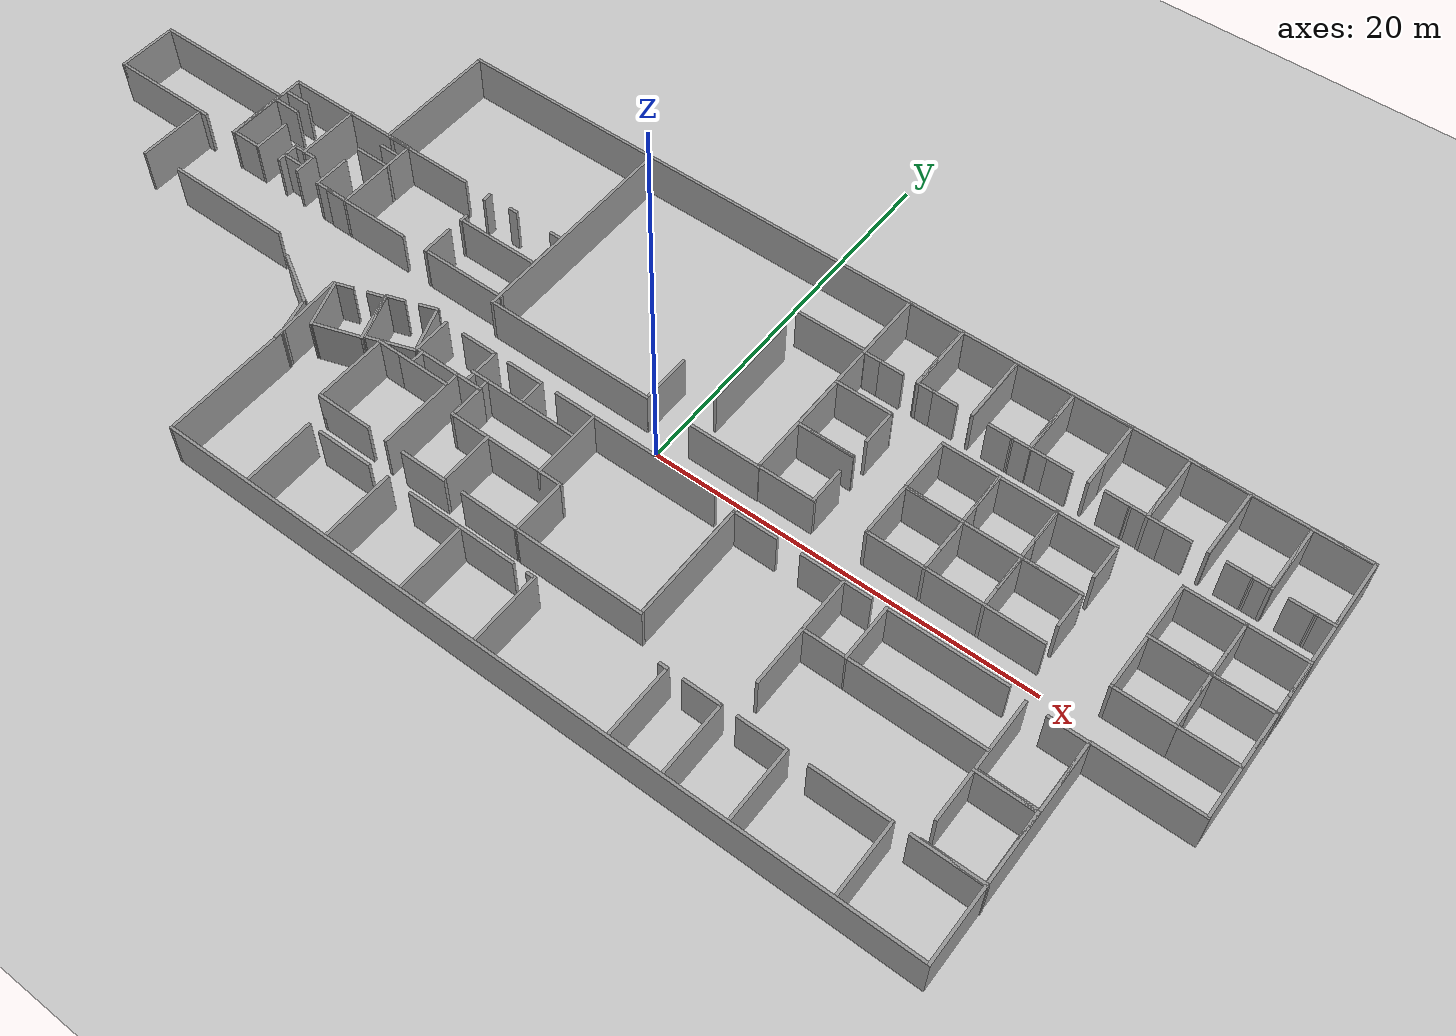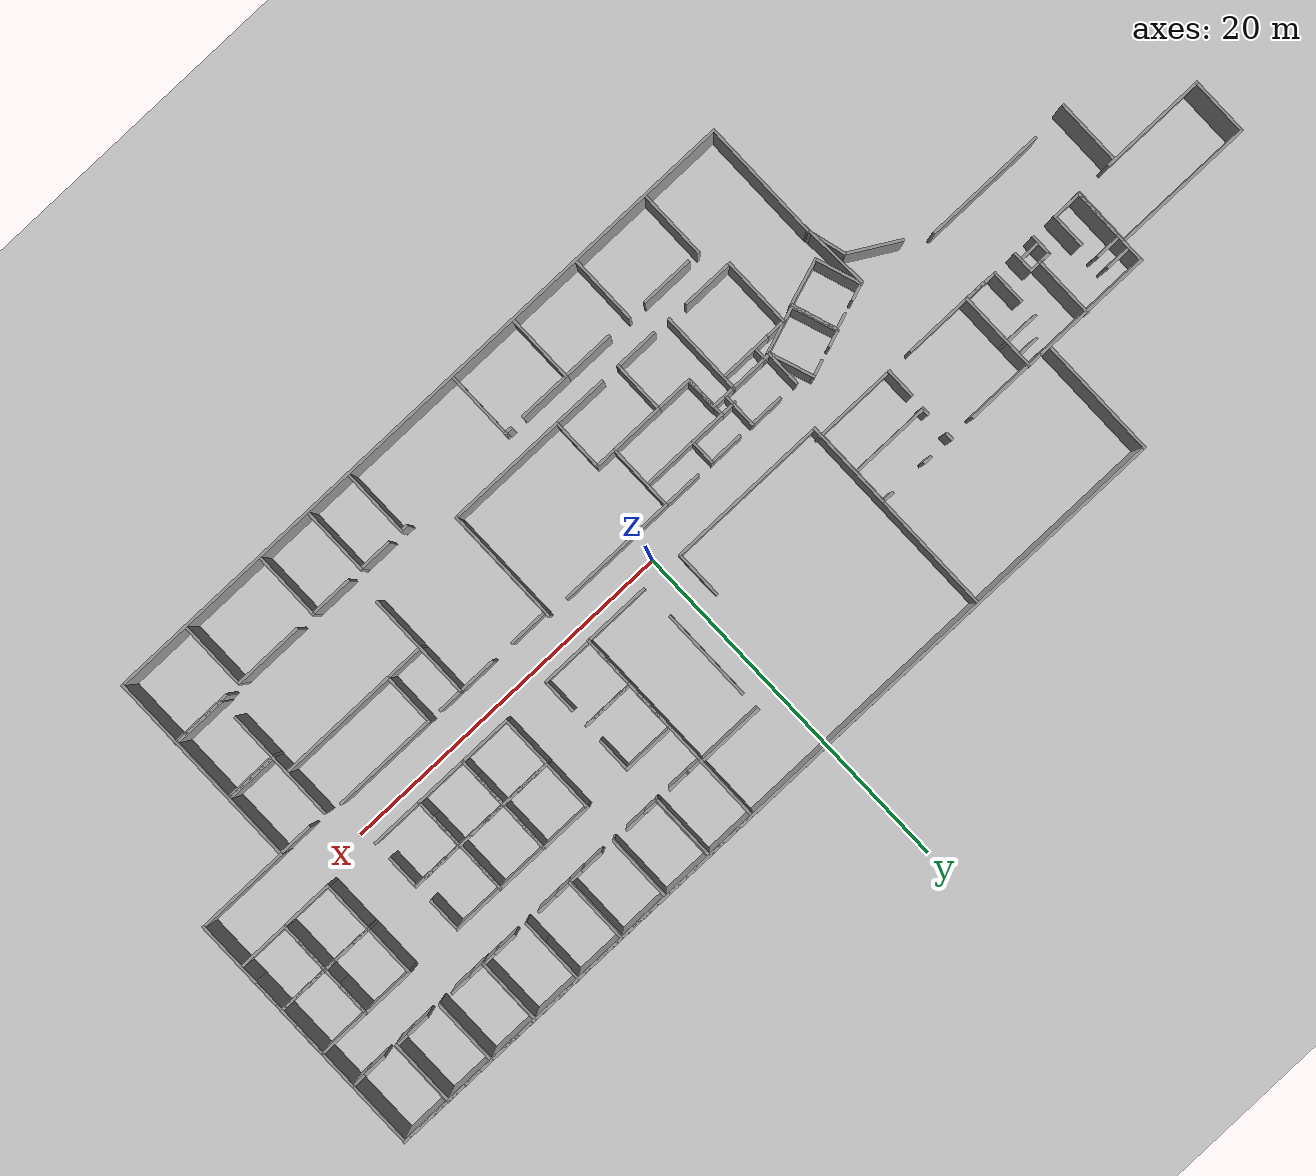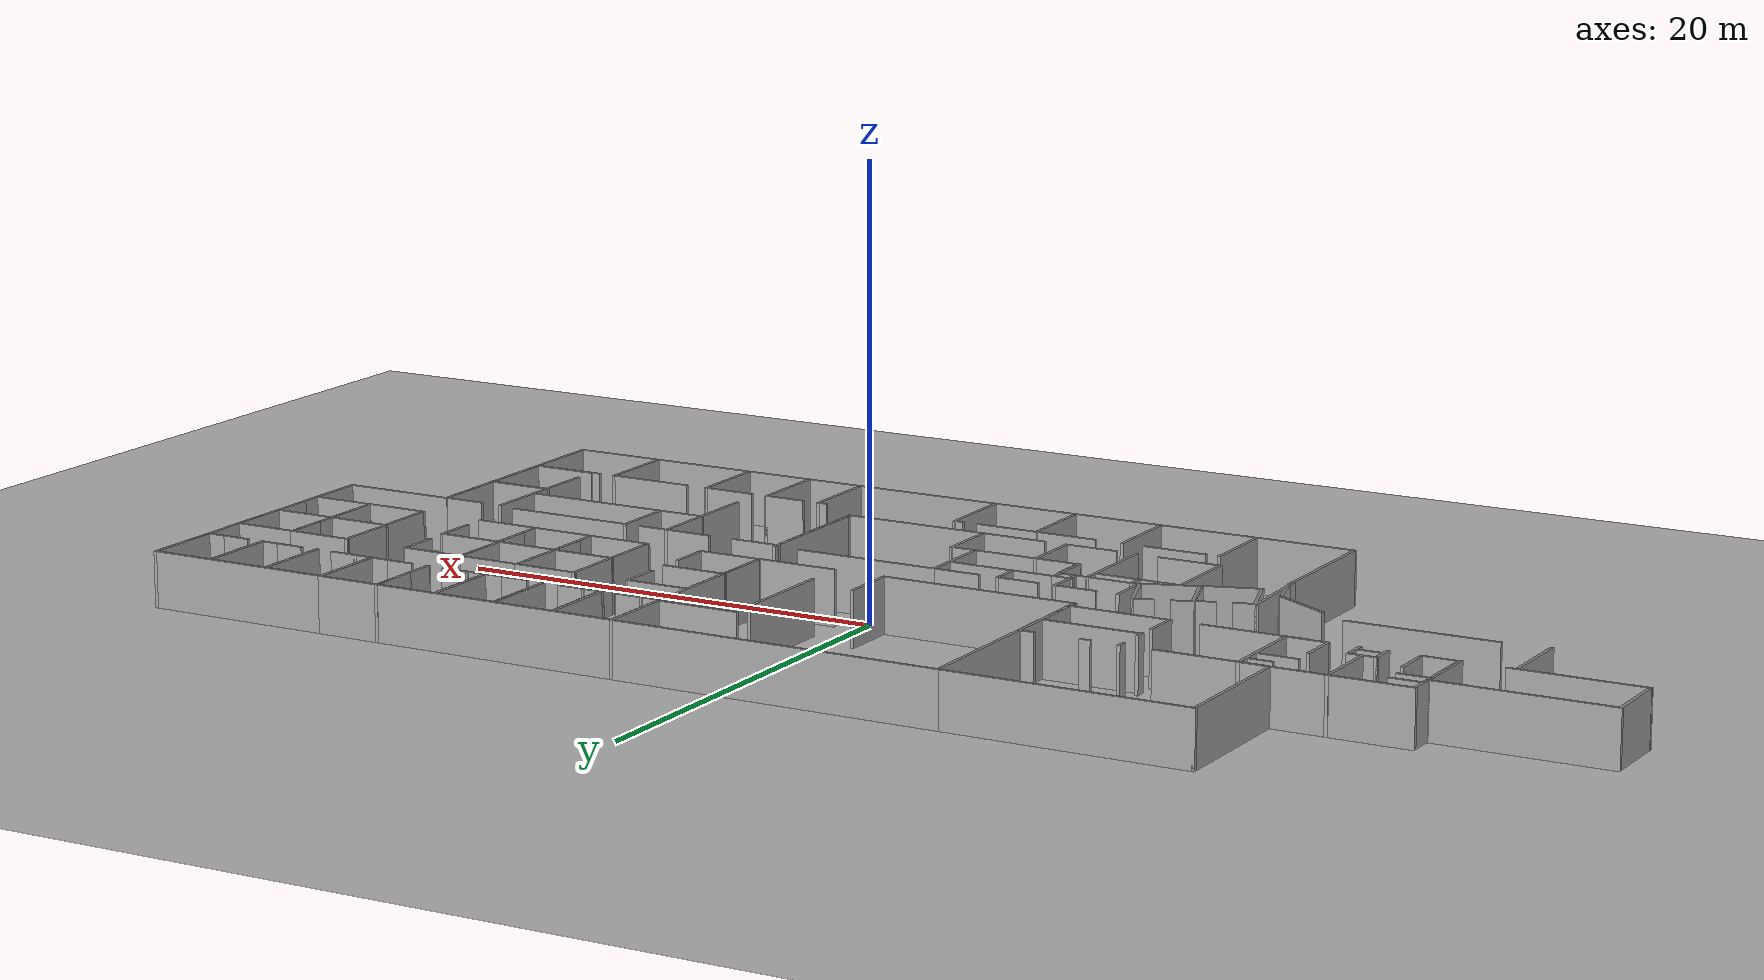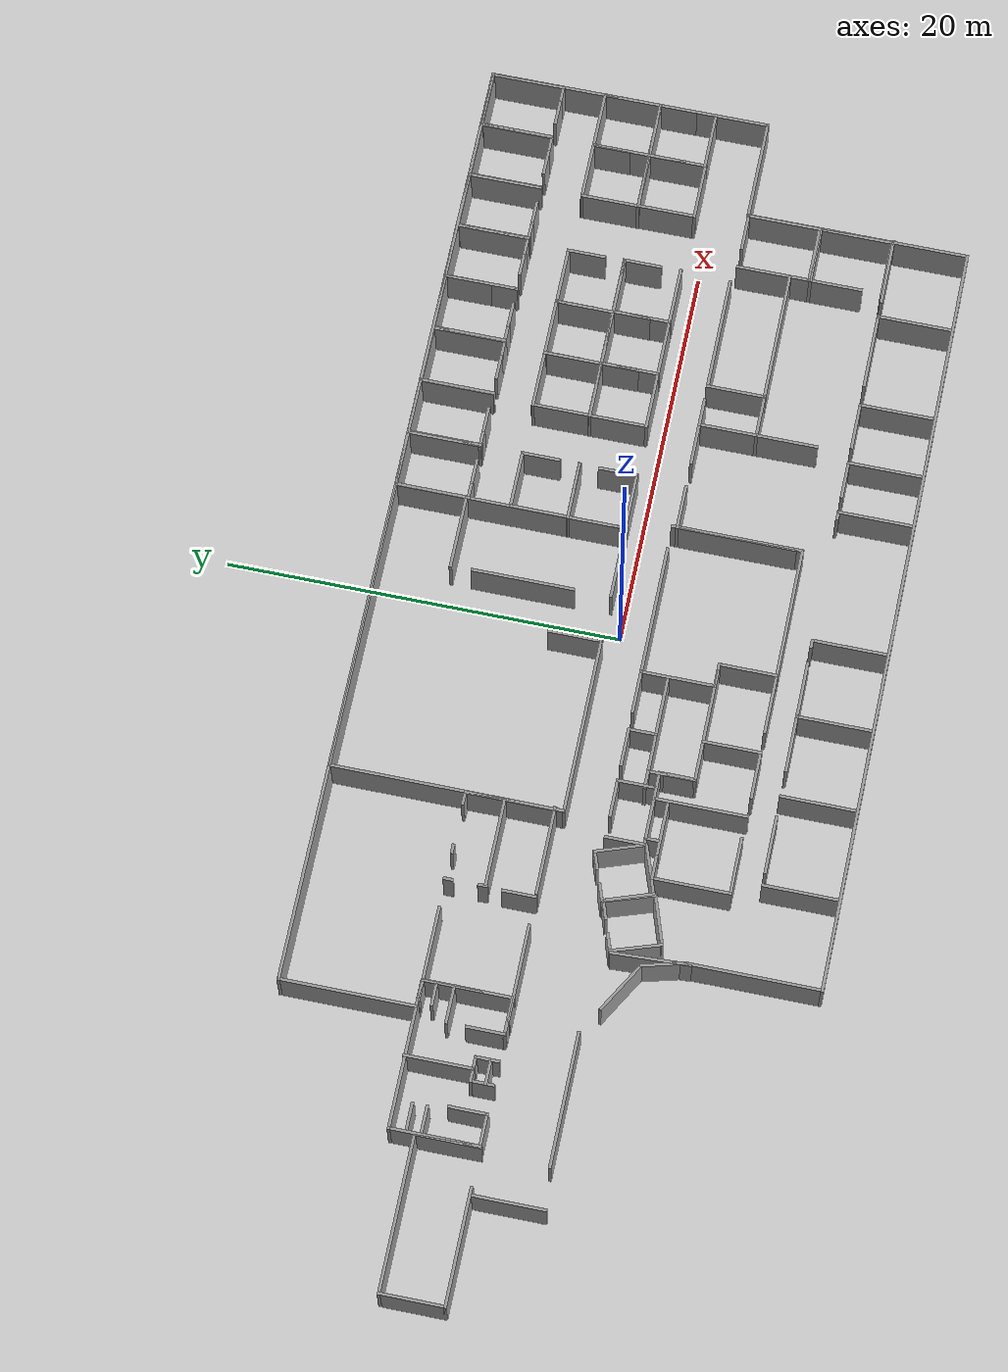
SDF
<sdf version="1.6">
 <world name="default">
  <light name="sun" type="directional">
   <pose>0 0 10 0 -0 0</pose>
   <diffuse>0.8 0.8 0.8 1</diffuse>
   <specular>0.2 0.2 0.2 1</specular>
   <attenuation>
    <range>1000</range>
    <constant>0.9</constant>
    <linear>0.01</linear>
    <quadratic>0.001</quadratic>
   </attenuation>
   <direction>-0.5 0.1 -0.9</direction>
  </light>
  <model name="ground_plane">
   <static>1</static>
   <link name="link">
    <collision name="collision">
     <geometry><plane><normal>0 0 1</normal><size>100 100</size></plane></geometry>
     <surface><friction><ode><mu>100</mu><mu2>50</mu2></ode></friction></surface>
    </collision>
    <visual name="visual">
     <cast_shadows>0</cast_shadows>
     <geometry><plane><normal>0 0 1</normal><size>100 100</size></plane></geometry>
     <material>
      <script><uri>file://media/materials/scripts/gazebo.material</uri><name>Gazebo/Grey</name></script>
     </material>
    </visual>
   </link>
  </model>
  <gravity>0 0 -9.8</gravity>
  <magnetic_field>6e-06 2.3e-05 -4.2e-05</magnetic_field>
  <atmosphere type="adiabatic"/>
  <physics name="default_physics" default="0" type="ode">
   <max_step_size>0.001</max_step_size>
   <real_time_factor>1</real_time_factor>
   <real_time_update_rate>1000</real_time_update_rate>
  </physics>
  <scene><ambient>0.4 0.4 0.4 1</ambient><background>0.7 0.7 0.7 1</background><shadows>1</shadows></scene>
  <spherical_coordinates>
   <surface_model>EARTH_WGS84</surface_model>
   <latitude_deg>0</latitude_deg>
   <longitude_deg>0</longitude_deg>
   <elevation>0</elevation>
   <heading_deg>0</heading_deg>
  </spherical_coordinates>
  <model name="201/202">
   <pose>-23.5593 3.4958 0 0 -0 0</pose>
   <link name="Wall_10">
    <collision name="Wall_10_Collision">
     <geometry><box><size>7.62002 0.15 2.5</size></box></geometry>
     <pose>0 0 1.25 0 -0 0</pose>
    </collision>
    <visual name="Wall_10_Visual">
     <pose>0 0 1.25 0 -0 0</pose>
     <geometry><box><size>7.62002 0.15 2.5</size></box></geometry>
     <material>
      <script><uri>file://media/materials/scripts/gazebo.material</uri><name>Gazebo/Grey</name></script>
      <ambient>1 1 1 1</ambient>
     </material>
     <meta><layer>0</layer></meta>
    </visual>
    <pose>-0.004655 2.1906 0 0 -0 3.14159</pose>
   </link>
   <link name="Wall_11">
    <collision name="Wall_11_Collision">
     <geometry><box><size>4.572 0.15 2.5</size></box></geometry>
     <pose>0 0 1.25 0 -0 0</pose>
    </collision>
    <visual name="Wall_11_Visual">
     <pose>0 0 1.25 0 -0 0</pose>
     <geometry><box><size>4.572 0.15 2.5</size></box></geometry>
     <material>
      <script><uri>file://media/materials/scripts/gazebo.material</uri><name>Gazebo/Grey</name></script>
      <ambient>1 1 1 1</ambient>
     </material>
     <meta><layer>0</layer></meta>
    </visual>
    <pose>-3.73965 -0.020398 0 0 -0 -1.5708</pose>
   </link>
   <link name="Wall_13">
    <collision name="Wall_13_Collision">
     <geometry><box><size>2 0.15 2.5</size></box></geometry>
     <pose>0 0 1.25 0 -0 0</pose>
    </collision>
    <visual name="Wall_13_Visual">
     <pose>0 0 1.25 0 -0 0</pose>
     <geometry><box><size>2 0.15 2.5</size></box></geometry>
     <material>
      <script><uri>file://media/materials/scripts/gazebo.material</uri><name>Gazebo/Grey</name></script>
      <ambient>1 1 1 1</ambient>
     </material>
     <meta><layer>0</layer></meta>
    </visual>
    <pose>2.80535 -2.23095 0 0 -0 3.14159</pose>
   </link>
   <link name="Wall_14">
    <collision name="Wall_14_Collision">
     <geometry><box><size>2 0.15 2.5</size></box></geometry>
     <pose>0 0 1.25 0 -0 0</pose>
    </collision>
    <visual name="Wall_14_Visual">
     <pose>0 0 1.25 0 -0 0</pose>
     <geometry><box><size>2 0.15 2.5</size></box></geometry>
     <material>
      <script><uri>file://media/materials/scripts/gazebo.material</uri><name>Gazebo/Grey</name></script>
      <ambient>1 1 1 1</ambient>
     </material>
     <meta><layer>0</layer></meta>
    </visual>
    <pose>1.88035 -1.30595 0 0 -0 1.5708</pose>
   </link>
   <link name="Wall_16">
    <collision name="Wall_16_Collision">
     <geometry><box><size>3.5 0.15 2.5</size></box></geometry>
     <pose>0 0 1.25 0 -0 0</pose>
    </collision>
    <visual name="Wall_16_Visual">
     <pose>0 0 1.25 0 -0 0</pose>
     <geometry><box><size>3.5 0.15 2.5</size></box></geometry>
     <material>
      <script><uri>file://media/materials/scripts/gazebo.material</uri><name>Gazebo/Grey</name></script>
      <ambient>1 1 1 1</ambient>
     </material>
     <meta><layer>0</layer></meta>
    </visual>
    <pose>-0.091763 0.556398 0 0 -0 -1.5708</pose>
   </link>
   <link name="Wall_17">
    <collision name="Wall_17_Collision">
     <geometry><box><size>0.75 0.15 2.5</size></box></geometry>
     <pose>0 0 1.25 0 -0 0</pose>
    </collision>
    <visual name="Wall_17_Visual">
     <pose>0 0 1.25 0 -0 0</pose>
     <geometry><box><size>0.75 0.15 2.5</size></box></geometry>
     <material>
      <script><uri>file://media/materials/scripts/gazebo.material</uri><name>Gazebo/Grey</name></script>
      <ambient>1 1 1 1</ambient>
     </material>
     <meta><layer>0</layer></meta>
    </visual>
    <pose>0.208236 -1.1186 0 0 -0 0</pose>
   </link>
   <link name="Wall_18">
    <collision name="Wall_18_Collision">
     <geometry><box><size>1.25 0.15 2.5</size></box></geometry>
     <pose>0 0 1.25 0 -0 0</pose>
    </collision>
    <visual name="Wall_18_Visual">
     <pose>0 0 1.25 0 -0 0</pose>
     <geometry><box><size>1.25 0.15 2.5</size></box></geometry>
     <material>
      <script><uri>file://media/materials/scripts/gazebo.material</uri><name>Gazebo/Grey</name></script>
      <ambient>1 1 1 1</ambient>
     </material>
     <meta><layer>0</layer></meta>
    </visual>
    <pose>0.508237 -1.6686 0 0 -0 -1.5708</pose>
   </link>
   <link name="Wall_20">
    <collision name="Wall_20_Collision">
     <geometry><box><size>0.75 0.15 2.5</size></box></geometry>
     <pose>0 0 1.25 0 -0 0</pose>
    </collision>
    <visual name="Wall_20_Visual">
     <pose>0 0 1.25 0 -0 0</pose>
     <geometry><box><size>0.75 0.15 2.5</size></box></geometry>
     <material>
      <script><uri>file://media/materials/scripts/gazebo.material</uri><name>Gazebo/Grey</name></script>
      <ambient>1 1 1 1</ambient>
     </material>
     <meta><layer>0</layer></meta>
    </visual>
    <pose>-0.391763 -1.1186 0 0 -0 3.14159</pose>
   </link>
   <link name="Wall_21">
    <collision name="Wall_21_Collision">
     <geometry><box><size>1.25 0.15 2.5</size></box></geometry>
     <pose>0 0 1.25 0 -0 0</pose>
    </collision>
    <visual name="Wall_21_Visual">
     <pose>0 0 1.25 0 -0 0</pose>
     <geometry><box><size>1.25 0.15 2.5</size></box></geometry>
     <material>
      <script><uri>file://media/materials/scripts/gazebo.material</uri><name>Gazebo/Grey</name></script>
      <ambient>1 1 1 1</ambient>
     </material>
     <meta><layer>0</layer></meta>
    </visual>
    <pose>-0.691764 -1.6686 0 0 -0 -1.5708</pose>
   </link>
   <link name="Wall_23">
    <collision name="Wall_23_Collision">
     <geometry><box><size>1.75 0.15 2.5</size></box></geometry>
     <pose>0 0 1.25 0 -0 0</pose>
    </collision>
    <visual name="Wall_23_Visual">
     <pose>0 0 1.25 0 -0 0</pose>
     <geometry><box><size>1.75 0.15 2.5</size></box></geometry>
     <material>
      <script><uri>file://media/materials/scripts/gazebo.material</uri><name>Gazebo/Grey</name></script>
      <ambient>1 1 1 1</ambient>
     </material>
     <meta><layer>0</layer></meta>
    </visual>
    <pose>-2.93966 -2.2314 0 0 -0 0</pose>
   </link>
   <link name="Wall_24">
    <collision name="Wall_24_Collision">
     <geometry><box><size>2 0.15 2.5</size></box></geometry>
     <pose>0 0 1.25 0 -0 0</pose>
    </collision>
    <visual name="Wall_24_Visual">
     <pose>0 0 1.25 0 -0 0</pose>
     <geometry><box><size>2 0.15 2.5</size></box></geometry>
     <material>
      <script><uri>file://media/materials/scripts/gazebo.material</uri><name>Gazebo/Grey</name></script>
      <ambient>1 1 1 1</ambient>
     </material>
     <meta><layer>0</layer></meta>
    </visual>
    <pose>-2.13965 -1.3064 0 0 -0 1.5708</pose>
   </link>
   <link name="Wall_28">
    <collision name="Wall_28_Collision">
     <geometry><box><size>1.5 0.15 2.5</size></box></geometry>
     <pose>0 0 1.25 0 -0 0</pose>
    </collision>
    <visual name="Wall_28_Visual">
     <pose>0 0 1.25 0 -0 0</pose>
     <geometry><box><size>1.5 0.15 2.5</size></box></geometry>
     <material>
      <script><uri>file://media/materials/scripts/gazebo.material</uri><name>Gazebo/Grey</name></script>
      <ambient>1 1 1 1</ambient>
     </material>
     <meta><layer>0</layer></meta>
    </visual>
    <pose>-3.01876 1.34811 0 0 -0 0</pose>
   </link>
   <link name="Wall_30">
    <collision name="Wall_30_Collision">
     <geometry><box><size>1.5 0.15 2.5</size></box></geometry>
     <pose>0 0 1.25 0 -0 0</pose>
    </collision>
    <visual name="Wall_30_Visual">
     <pose>0 0 1.25 0 -0 0</pose>
     <geometry><box><size>1.5 0.15 2.5</size></box></geometry>
     <material>
      <script><uri>file://media/materials/scripts/gazebo.material</uri><name>Gazebo/Grey</name></script>
      <ambient>1 1 1 1</ambient>
     </material>
     <meta><layer>0</layer></meta>
    </visual>
    <pose>-3.03023 0.625411 0 0 -0 0</pose>
   </link>
   <link name="Wall_32">
    <collision name="Wall_32_Collision">
     <geometry><box><size>2 0.15 2.5</size></box></geometry>
     <pose>0 0 1.25 0 -0 0</pose>
    </collision>
    <visual name="Wall_32_Visual">
     <pose>0 0 1.25 0 -0 0</pose>
     <geometry><box><size>2 0.15 2.5</size></box></geometry>
     <material>
      <script><uri>file://media/materials/scripts/gazebo.material</uri><name>Gazebo/Grey</name></script>
      <ambient>1 1 1 1</ambient>
     </material>
     <meta><layer>0</layer></meta>
    </visual>
    <pose>2.81466 0.625411 0 0 -0 3.14159</pose>
   </link>
   <link name="Wall_34">
    <collision name="Wall_34_Collision">
     <geometry><box><size>1.25 0.15 2.5</size></box></geometry>
     <pose>0 0 1.25 0 -0 0</pose>
    </collision>
    <visual name="Wall_34_Visual">
     <pose>0 0 1.25 0 -0 0</pose>
     <geometry><box><size>1.25 0.15 2.5</size></box></geometry>
     <material>
      <script><uri>file://media/materials/scripts/gazebo.material</uri><name>Gazebo/Grey</name></script>
      <ambient>1 1 1 1</ambient>
     </material>
     <meta><layer>0</layer></meta>
    </visual>
    <pose>3.16672 1.48576 0 0 -0 3.14159</pose>
   </link>
   <link name="Wall_36">
    <collision name="Wall_36_Collision">
     <geometry><box><size>1.25 0.15 2.5</size></box></geometry>
     <pose>0 0 1.25 0 -0 0</pose>
    </collision>
    <visual name="Wall_36_Visual">
     <pose>0 0 1.25 0 -0 0</pose>
     <geometry><box><size>1.25 0.15 2.5</size></box></geometry>
     <material>
      <script><uri>file://media/materials/scripts/gazebo.material</uri><name>Gazebo/Grey</name></script>
      <ambient>1 1 1 1</ambient>
     </material>
     <meta><layer>0</layer></meta>
    </visual>
    <pose>-0.138273 -1.8524 0 0 -0 0</pose>
   </link>
   <link name="Wall_9">
    <collision name="Wall_9_Collision">
     <geometry><box><size>4.572 0.15 2.5</size></box></geometry>
     <pose>0 0 1.25 0 -0 0</pose>
    </collision>
    <visual name="Wall_9_Visual">
     <pose>0 0 1.25 0 -0 0</pose>
     <geometry><box><size>4.572 0.15 2.5</size></box></geometry>
     <material>
      <script><uri>file://media/materials/scripts/gazebo.material</uri><name>Gazebo/Grey</name></script>
      <ambient>1 1 1 1</ambient>
     </material>
     <meta><layer>0</layer></meta>
    </visual>
    <pose>3.73035 -0.020175 0 0 -0 1.5708</pose>
   </link>
   <static>1</static>
  </model>
  <model name="197A">
   <link name="Wall_33">
    <pose>3.925 0 0 0 -0 1.5708</pose>
    <visual name="Wall_33_Visual">
     <pose>0 0 1.25 0 -0 0</pose>
     <geometry><box><size>3.336 0.15 2.5</size></box></geometry>
     <material>
      <script><uri>file://media/materials/scripts/gazebo.material</uri><name>Gazebo/Grey</name></script>
      <ambient>1 1 1 1</ambient>
      <shader type="pixel"/>
     </material>
     <meta><layer>0</layer></meta>
    </visual>
    <collision name="Wall_33_Collision">
     <pose>0 0 1.25 0 -0 0</pose>
     <geometry><box><size>3.336 0.15 2.5</size></box></geometry>
     <surface>
      <friction>
       <ode><mu>1</mu><mu2>1</mu2><fdir1>0 0 0</fdir1><slip1>0</slip1><slip2>0</slip2></ode>
       <torsional>
        <coefficient>1</coefficient>
        <patch_radius>0</patch_radius>
        <surface_radius>0</surface_radius>
        <use_patch_radius>1</use_patch_radius>
        <ode><slip>0</slip></ode>
       </torsional>
      </friction>
      <bounce><restitution_coefficient>0</restitution_coefficient><threshold>1e+06</threshold></bounce>
      <contact>
       <collide_without_contact>0</collide_without_contact>
       <collide_without_contact_bitmask>1</collide_without_contact_bitmask>
       <collide_bitmask>1</collide_bitmask>
       <ode>
        <soft_cfm>0</soft_cfm>
        <soft_erp>0.2</soft_erp>
        <kp>1e+13</kp>
        <kd>1</kd>
        <max_vel>0.01</max_vel>
        <min_depth>0</min_depth>
       </ode>
       <bullet>
        <split_impulse>1</split_impulse>
        <split_impulse_penetration_threshold>-0.01</split_impulse_penetration_threshold>
        <soft_cfm>0</soft_cfm>
        <soft_erp>0.2</soft_erp>
        <kp>1e+13</kp>
        <kd>1</kd>
       </bullet>
      </contact>
     </surface>
    </collision>
   </link>
   <link name="Wall_34">
    <pose>0 1.593 0 0 -0 3.14159</pose>
    <visual name="Wall_34_Visual">
     <pose>0 0 1.25 0 -0 0</pose>
     <geometry><box><size>8 0.15 2.5</size></box></geometry>
     <material>
      <script><uri>file://media/materials/scripts/gazebo.material</uri><name>Gazebo/Grey</name></script>
      <ambient>1 1 1 1</ambient>
      <shader type="pixel"/>
     </material>
     <meta><layer>0</layer></meta>
    </visual>
    <collision name="Wall_34_Collision">
     <pose>0 0 1.25 0 -0 0</pose>
     <geometry><box><size>8 0.15 2.5</size></box></geometry>
     <surface>
      <friction>
       <ode><mu>1</mu><mu2>1</mu2><fdir1>0 0 0</fdir1><slip1>0</slip1><slip2>0</slip2></ode>
       <torsional>
        <coefficient>1</coefficient>
        <patch_radius>0</patch_radius>
        <surface_radius>0</surface_radius>
        <use_patch_radius>1</use_patch_radius>
        <ode><slip>0</slip></ode>
       </torsional>
      </friction>
      <bounce><restitution_coefficient>0</restitution_coefficient><threshold>1e+06</threshold></bounce>
      <contact>
       <collide_without_contact>0</collide_without_contact>
       <collide_without_contact_bitmask>1</collide_without_contact_bitmask>
       <collide_bitmask>1</collide_bitmask>
       <ode>
        <soft_cfm>0</soft_cfm>
        <soft_erp>0.2</soft_erp>
        <kp>1e+13</kp>
        <kd>1</kd>
        <max_vel>0.01</max_vel>
        <min_depth>0</min_depth>
       </ode>
       <bullet>
        <split_impulse>1</split_impulse>
        <split_impulse_penetration_threshold>-0.01</split_impulse_penetration_threshold>
        <soft_cfm>0</soft_cfm>
        <soft_erp>0.2</soft_erp>
        <kp>1e+13</kp>
        <kd>1</kd>
       </bullet>
      </contact>
     </surface>
    </collision>
   </link>
   <link name="Wall_35">
    <pose>-3.925 0 0 0 0 -1.5708</pose>
    <visual name="Wall_35_Visual">
     <pose>0 0 1.25 0 -0 0</pose>
     <geometry><box><size>3.336 0.15 2.5</size></box></geometry>
     <material>
      <script><uri>file://media/materials/scripts/gazebo.material</uri><name>Gazebo/Grey</name></script>
      <ambient>1 1 1 1</ambient>
      <shader type="pixel"/>
     </material>
     <meta><layer>0</layer></meta>
    </visual>
    <collision name="Wall_35_Collision">
     <pose>0 0 1.25 0 -0 0</pose>
     <geometry><box><size>3.336 0.15 2.5</size></box></geometry>
     <surface>
      <friction>
       <ode><mu>1</mu><mu2>1</mu2><fdir1>0 0 0</fdir1><slip1>0</slip1><slip2>0</slip2></ode>
       <torsional>
        <coefficient>1</coefficient>
        <patch_radius>0</patch_radius>
        <surface_radius>0</surface_radius>
        <use_patch_radius>1</use_patch_radius>
        <ode><slip>0</slip></ode>
       </torsional>
      </friction>
      <bounce><restitution_coefficient>0</restitution_coefficient><threshold>1e+06</threshold></bounce>
      <contact>
       <collide_without_contact>0</collide_without_contact>
       <collide_without_contact_bitmask>1</collide_without_contact_bitmask>
       <collide_bitmask>1</collide_bitmask>
       <ode>
        <soft_cfm>0</soft_cfm>
        <soft_erp>0.2</soft_erp>
        <kp>1e+13</kp>
        <kd>1</kd>
        <max_vel>0.01</max_vel>
        <min_depth>0</min_depth>
       </ode>
       <bullet>
        <split_impulse>1</split_impulse>
        <split_impulse_penetration_threshold>-0.01</split_impulse_penetration_threshold>
        <soft_cfm>0</soft_cfm>
        <soft_erp>0.2</soft_erp>
        <kp>1e+13</kp>
        <kd>1</kd>
       </bullet>
      </contact>
     </surface>
    </collision>
   </link>
   <link name="Wall_37">
    <pose>-1 -1.593 0 0 -0 0</pose>
    <visual name="Wall_37_Visual">
     <pose>0 0 1.25 0 -0 0</pose>
     <geometry><box><size>6 0.15 2.5</size></box></geometry>
     <material>
      <script><uri>file://media/materials/scripts/gazebo.material</uri><name>Gazebo/Grey</name></script>
      <ambient>1 1 1 1</ambient>
      <shader type="pixel"/>
     </material>
     <meta><layer>0</layer></meta>
    </visual>
    <collision name="Wall_37_Collision">
     <pose>0 0 1.25 0 -0 0</pose>
     <geometry><box><size>6 0.15 2.5</size></box></geometry>
     <surface>
      <friction>
       <ode><mu>1</mu><mu2>1</mu2><fdir1>0 0 0</fdir1><slip1>0</slip1><slip2>0</slip2></ode>
       <torsional>
        <coefficient>1</coefficient>
        <patch_radius>0</patch_radius>
        <surface_radius>0</surface_radius>
        <use_patch_radius>1</use_patch_radius>
        <ode><slip>0</slip></ode>
       </torsional>
      </friction>
      <bounce><restitution_coefficient>0</restitution_coefficient><threshold>1e+06</threshold></bounce>
      <contact>
       <collide_without_contact>0</collide_without_contact>
       <collide_without_contact_bitmask>1</collide_without_contact_bitmask>
       <collide_bitmask>1</collide_bitmask>
       <ode>
        <soft_cfm>0</soft_cfm>
        <soft_erp>0.2</soft_erp>
        <kp>1e+13</kp>
        <kd>1</kd>
        <max_vel>0.01</max_vel>
        <min_depth>0</min_depth>
       </ode>
       <bullet>
        <split_impulse>1</split_impulse>
        <split_impulse_penetration_threshold>-0.01</split_impulse_penetration_threshold>
        <soft_cfm>0</soft_cfm>
        <soft_erp>0.2</soft_erp>
        <kp>1e+13</kp>
        <kd>1</kd>
       </bullet>
      </contact>
     </surface>
    </collision>
   </link>
   <static>1</static>
   <pose>-31.262 2.82988 0 0 -0 0</pose>
  </model>
  <model name="Floor3Perimeter">
   <link name="Wall_0">
    <pose>-20.4275 9.45 0 0 -0 1.5708</pose>
    <visual name="Wall_0_Visual">
     <pose>0 0 1.25 0 -0 0</pose>
     <geometry><box><size>6.858 0.15 2.5</size></box></geometry>
     <material>
      <script><uri>file://media/materials/scripts/gazebo.material</uri><name>Gazebo/Grey</name></script>
      <ambient>1 1 1 1</ambient>
      <shader type="pixel"/>
     </material>
     <meta><layer>0</layer></meta>
    </visual>
    <collision name="Wall_0_Collision">
     <pose>0 0 1.25 0 -0 0</pose>
     <geometry><box><size>6.858 0.15 2.5</size></box></geometry>
     <surface>
      <friction>
       <ode><mu>1</mu><mu2>1</mu2><fdir1>0 0 0</fdir1><slip1>0</slip1><slip2>0</slip2></ode>
       <torsional>
        <coefficient>1</coefficient>
        <patch_radius>0</patch_radius>
        <surface_radius>0</surface_radius>
        <use_patch_radius>1</use_patch_radius>
        <ode><slip>0</slip></ode>
       </torsional>
      </friction>
      <bounce><restitution_coefficient>0</restitution_coefficient><threshold>1e+06</threshold></bounce>
      <contact>
       <collide_without_contact>0</collide_without_contact>
       <collide_without_contact_bitmask>1</collide_without_contact_bitmask>
       <collide_bitmask>1</collide_bitmask>
       <ode>
        <soft_cfm>0</soft_cfm>
        <soft_erp>0.2</soft_erp>
        <kp>1e+13</kp>
        <kd>1</kd>
        <max_vel>0.01</max_vel>
        <min_depth>0</min_depth>
       </ode>
       <bullet>
        <split_impulse>1</split_impulse>
        <split_impulse_penetration_threshold>-0.01</split_impulse_penetration_threshold>
        <soft_cfm>0</soft_cfm>
        <soft_erp>0.2</soft_erp>
        <kp>1e+13</kp>
        <kd>1</kd>
       </bullet>
      </contact>
     </surface>
    </collision>
   </link>
   <link name="Wall_1">
    <pose>4.26245 12.804 0 0 -0 0</pose>
    <visual name="Wall_1_Visual">
     <pose>0 0 1.25 0 -0 0</pose>
     <geometry><box><size>49.53 0.15 2.5</size></box></geometry>
     <material>
      <script><uri>file://media/materials/scripts/gazebo.material</uri><name>Gazebo/Grey</name></script>
      <ambient>1 1 1 1</ambient>
      <shader type="pixel"/>
     </material>
     <meta><layer>0</layer></meta>
    </visual>
    <collision name="Wall_1_Collision">
     <pose>0 0 1.25 0 -0 0</pose>
     <geometry><box><size>49.53 0.15 2.5</size></box></geometry>
     <surface>
      <friction>
       <ode><mu>1</mu><mu2>1</mu2><fdir1>0 0 0</fdir1><slip1>0</slip1><slip2>0</slip2></ode>
       <torsional>
        <coefficient>1</coefficient>
        <patch_radius>0</patch_radius>
        <surface_radius>0</surface_radius>
        <use_patch_radius>1</use_patch_radius>
        <ode><slip>0</slip></ode>
       </torsional>
      </friction>
      <bounce><restitution_coefficient>0</restitution_coefficient><threshold>1e+06</threshold></bounce>
      <contact>
       <collide_without_contact>0</collide_without_contact>
       <collide_without_contact_bitmask>1</collide_without_contact_bitmask>
       <collide_bitmask>1</collide_bitmask>
       <ode>
        <soft_cfm>0</soft_cfm>
        <soft_erp>0.2</soft_erp>
        <kp>1e+13</kp>
        <kd>1</kd>
        <max_vel>0.01</max_vel>
        <min_depth>0</min_depth>
       </ode>
       <bullet>
        <split_impulse>1</split_impulse>
        <split_impulse_penetration_threshold>-0.01</split_impulse_penetration_threshold>
        <soft_cfm>0</soft_cfm>
        <soft_erp>0.2</soft_erp>
        <kp>1e+13</kp>
        <kd>1</kd>
       </bullet>
      </contact>
     </surface>
    </collision>
   </link>
   <link name="Wall_10">
    <pose>-23.4985 -1.81856 0 0 -0 3.14159</pose>
    <visual name="Wall_10_Visual">
     <pose>0 0 1.25 0 -0 0</pose>
     <geometry><box><size>6.858 0.15 2.5</size></box></geometry>
     <material>
      <script><uri>file://media/materials/scripts/gazebo.material</uri><name>Gazebo/Grey</name></script>
      <ambient>1 1 1 1</ambient>
      <shader type="pixel"/>
     </material>
     <meta><layer>0</layer></meta>
    </visual>
    <collision name="Wall_10_Collision">
     <pose>0 0 1.25 0 -0 0</pose>
     <geometry><box><size>6.858 0.15 2.5</size></box></geometry>
     <surface>
      <friction>
       <ode><mu>1</mu><mu2>1</mu2><fdir1>0 0 0</fdir1><slip1>0</slip1><slip2>0</slip2></ode>
       <torsional>
        <coefficient>1</coefficient>
        <patch_radius>0</patch_radius>
        <surface_radius>0</surface_radius>
        <use_patch_radius>1</use_patch_radius>
        <ode><slip>0</slip></ode>
       </torsional>
      </friction>
      <bounce><restitution_coefficient>0</restitution_coefficient><threshold>1e+06</threshold></bounce>
      <contact>
       <collide_without_contact>0</collide_without_contact>
       <collide_without_contact_bitmask>1</collide_without_contact_bitmask>
       <collide_bitmask>1</collide_bitmask>
       <ode>
        <soft_cfm>0</soft_cfm>
        <soft_erp>0.2</soft_erp>
        <kp>1e+13</kp>
        <kd>1</kd>
        <max_vel>0.01</max_vel>
        <min_depth>0</min_depth>
       </ode>
       <bullet>
        <split_impulse>1</split_impulse>
        <split_impulse_penetration_threshold>-0.01</split_impulse_penetration_threshold>
        <soft_cfm>0</soft_cfm>
        <soft_erp>0.2</soft_erp>
        <kp>1e+13</kp>
        <kd>1</kd>
       </bullet>
      </contact>
     </surface>
    </collision>
   </link>
   <link name="Wall_14">
    <pose>-28.9525 -0.282482 0 0 -0 1.5708</pose>
    <inertial>
     <inertia><ixx>0</ixx><ixy>0</ixy><ixz>0</ixz><iyy>0</iyy><iyz>0</iyz><izz>0</izz></inertia>
     <mass>0</mass>
    </inertial>
    <visual name="Wall_14_Visual">
     <pose>0 0 1.25 0 -0 0</pose>
     <geometry><box><size>3.66308 0.15 2.5</size></box></geometry>
     <material>
      <script><uri>file://media/materials/scripts/gazebo.material</uri><name>Gazebo/Grey</name></script>
      <ambient>1 1 1 1</ambient>
      <shader type="pixel"/>
     </material>
     <meta><layer>0</layer></meta>
    </visual>
    <collision name="Wall_14_Collision">
     <pose>0 0 1.25 0 -0 0</pose>
     <geometry><box><size>3.66308 0.15 2.5</size></box></geometry>
     <surface>
      <friction>
       <ode><mu>1</mu><mu2>1</mu2><fdir1>0 0 0</fdir1><slip1>0</slip1><slip2>0</slip2></ode>
       <torsional>
        <coefficient>1</coefficient>
        <patch_radius>0</patch_radius>
        <surface_radius>0</surface_radius>
        <use_patch_radius>1</use_patch_radius>
        <ode><slip>0</slip></ode>
       </torsional>
      </friction>
      <bounce><restitution_coefficient>0</restitution_coefficient><threshold>1e+06</threshold></bounce>
      <contact>
       <collide_without_contact>0</collide_without_contact>
       <collide_without_contact_bitmask>1</collide_without_contact_bitmask>
       <collide_bitmask>1</collide_bitmask>
       <ode>
        <soft_cfm>0</soft_cfm>
        <soft_erp>0.2</soft_erp>
        <kp>1e+13</kp>
        <kd>1</kd>
        <max_vel>0.01</max_vel>
        <min_depth>0</min_depth>
       </ode>
       <bullet>
        <split_impulse>1</split_impulse>
        <split_impulse_penetration_threshold>-0.01</split_impulse_penetration_threshold>
        <soft_cfm>0</soft_cfm>
        <soft_erp>0.2</soft_erp>
        <kp>1e+13</kp>
        <kd>1</kd>
       </bullet>
      </contact>
     </surface>
    </collision>
   </link>
   <link name="Wall_2">
    <pose>28.9524 5.64 0 0 0 -1.5708</pose>
    <visual name="Wall_2_Visual">
     <pose>0 0 1.25 0 -0 0</pose>
     <geometry><box><size>14.478 0.15 2.5</size></box></geometry>
     <material>
      <script><uri>file://media/materials/scripts/gazebo.material</uri><name>Gazebo/Grey</name></script>
      <ambient>1 1 1 1</ambient>
      <shader type="pixel"/>
     </material>
     <meta><layer>0</layer></meta>
    </visual>
    <collision name="Wall_2_Collision">
     <pose>0 0 1.25 0 -0 0</pose>
     <geometry><box><size>14.478 0.15 2.5</size></box></geometry>
     <surface>
      <friction>
       <ode><mu>1</mu><mu2>1</mu2><fdir1>0 0 0</fdir1><slip1>0</slip1><slip2>0</slip2></ode>
       <torsional>
        <coefficient>1</coefficient>
        <patch_radius>0</patch_radius>
        <surface_radius>0</surface_radius>
        <use_patch_radius>1</use_patch_radius>
        <ode><slip>0</slip></ode>
       </torsional>
      </friction>
      <bounce><restitution_coefficient>0</restitution_coefficient><threshold>1e+06</threshold></bounce>
      <contact>
       <collide_without_contact>0</collide_without_contact>
       <collide_without_contact_bitmask>1</collide_without_contact_bitmask>
       <collide_bitmask>1</collide_bitmask>
       <ode>
        <soft_cfm>0</soft_cfm>
        <soft_erp>0.2</soft_erp>
        <kp>1e+13</kp>
        <kd>1</kd>
        <max_vel>0.01</max_vel>
        <min_depth>0</min_depth>
       </ode>
       <bullet>
        <split_impulse>1</split_impulse>
        <split_impulse_penetration_threshold>-0.01</split_impulse_penetration_threshold>
        <soft_cfm>0</soft_cfm>
        <soft_erp>0.2</soft_erp>
        <kp>1e+13</kp>
        <kd>1</kd>
       </bullet>
      </contact>
     </surface>
    </collision>
   </link>
   <link name="Wall_3">
    <pose>26.3605 -1.524 0 0 -0 3.14159</pose>
    <visual name="Wall_3_Visual">
     <pose>0 0 1.25 0 -0 0</pose>
     <geometry><box><size>5.334 0.15 2.5</size></box></geometry>
     <material>
      <script><uri>file://media/materials/scripts/gazebo.material</uri><name>Gazebo/Grey</name></script>
      <ambient>1 1 1 1</ambient>
      <shader type="pixel"/>
     </material>
     <meta><layer>0</layer></meta>
    </visual>
    <collision name="Wall_3_Collision">
     <pose>0 0 1.25 0 -0 0</pose>
     <geometry><box><size>5.334 0.15 2.5</size></box></geometry>
     <surface>
      <friction>
       <ode><mu>1</mu><mu2>1</mu2><fdir1>0 0 0</fdir1><slip1>0</slip1><slip2>0</slip2></ode>
       <torsional>
        <coefficient>1</coefficient>
        <patch_radius>0</patch_radius>
        <surface_radius>0</surface_radius>
        <use_patch_radius>1</use_patch_radius>
        <ode><slip>0</slip></ode>
       </torsional>
      </friction>
      <bounce><restitution_coefficient>0</restitution_coefficient><threshold>1e+06</threshold></bounce>
      <contact>
       <collide_without_contact>0</collide_without_contact>
       <collide_without_contact_bitmask>1</collide_without_contact_bitmask>
       <collide_bitmask>1</collide_bitmask>
       <ode>
        <soft_cfm>0</soft_cfm>
        <soft_erp>0.2</soft_erp>
        <kp>1e+13</kp>
        <kd>1</kd>
        <max_vel>0.01</max_vel>
        <min_depth>0</min_depth>
       </ode>
       <bullet>
        <split_impulse>1</split_impulse>
        <split_impulse_penetration_threshold>-0.01</split_impulse_penetration_threshold>
        <soft_cfm>0</soft_cfm>
        <soft_erp>0.2</soft_erp>
        <kp>1e+13</kp>
        <kd>1</kd>
       </bullet>
      </contact>
     </surface>
    </collision>
   </link>
   <link name="Wall_4">
    <pose>23.7685 -7.164 0 0 0 -1.5708</pose>
    <visual name="Wall_4_Visual">
     <pose>0 0 1.25 0 -0 0</pose>
     <geometry><box><size>11.43 0.15 2.5</size></box></geometry>
     <material>
      <script><uri>file://media/materials/scripts/gazebo.material</uri><name>Gazebo/Grey</name></script>
      <ambient>1 1 1 1</ambient>
      <shader type="pixel"/>
     </material>
     <meta><layer>0</layer></meta>
    </visual>
    <collision name="Wall_4_Collision">
     <pose>0 0 1.25 0 -0 0</pose>
     <geometry><box><size>11.43 0.15 2.5</size></box></geometry>
     <surface>
      <friction>
       <ode><mu>1</mu><mu2>1</mu2><fdir1>0 0 0</fdir1><slip1>0</slip1><slip2>0</slip2></ode>
       <torsional>
        <coefficient>1</coefficient>
        <patch_radius>0</patch_radius>
        <surface_radius>0</surface_radius>
        <use_patch_radius>1</use_patch_radius>
        <ode><slip>0</slip></ode>
       </torsional>
      </friction>
      <bounce><restitution_coefficient>0</restitution_coefficient><threshold>1e+06</threshold></bounce>
      <contact>
       <collide_without_contact>0</collide_without_contact>
       <collide_without_contact_bitmask>1</collide_without_contact_bitmask>
       <collide_bitmask>1</collide_bitmask>
       <ode>
        <soft_cfm>0</soft_cfm>
        <soft_erp>0.2</soft_erp>
        <kp>1e+13</kp>
        <kd>1</kd>
        <max_vel>0.01</max_vel>
        <min_depth>0</min_depth>
       </ode>
       <bullet>
        <split_impulse>1</split_impulse>
        <split_impulse_penetration_threshold>-0.01</split_impulse_penetration_threshold>
        <soft_cfm>0</soft_cfm>
        <soft_erp>0.2</soft_erp>
        <kp>1e+13</kp>
        <kd>1</kd>
       </bullet>
      </contact>
     </surface>
    </collision>
   </link>
   <link name="Wall_5">
    <pose>4.03145 -12.804 0 0 -0 3.14159</pose>
    <visual name="Wall_5_Visual">
     <pose>0 0 1.25 0 -0 0</pose>
     <geometry><box><size>39.624 0.15 2.5</size></box></geometry>
     <material>
      <script><uri>file://media/materials/scripts/gazebo.material</uri><name>Gazebo/Grey</name></script>
      <ambient>1 1 1 1</ambient>
      <shader type="pixel"/>
     </material>
     <meta><layer>0</layer></meta>
    </visual>
    <collision name="Wall_5_Collision">
     <pose>0 0 1.25 0 -0 0</pose>
     <geometry><box><size>39.624 0.15 2.5</size></box></geometry>
     <surface>
      <friction>
       <ode><mu>1</mu><mu2>1</mu2><fdir1>0 0 0</fdir1><slip1>0</slip1><slip2>0</slip2></ode>
       <torsional>
        <coefficient>1</coefficient>
        <patch_radius>0</patch_radius>
        <surface_radius>0</surface_radius>
        <use_patch_radius>1</use_patch_radius>
        <ode><slip>0</slip></ode>
       </torsional>
      </friction>
      <bounce><restitution_coefficient>0</restitution_coefficient><threshold>1e+06</threshold></bounce>
      <contact>
       <collide_without_contact>0</collide_without_contact>
       <collide_without_contact_bitmask>1</collide_without_contact_bitmask>
       <collide_bitmask>1</collide_bitmask>
       <ode>
        <soft_cfm>0</soft_cfm>
        <soft_erp>0.2</soft_erp>
        <kp>1e+13</kp>
        <kd>1</kd>
        <max_vel>0.01</max_vel>
        <min_depth>0</min_depth>
       </ode>
       <bullet>
        <split_impulse>1</split_impulse>
        <split_impulse_penetration_threshold>-0.01</split_impulse_penetration_threshold>
        <soft_cfm>0</soft_cfm>
        <soft_erp>0.2</soft_erp>
        <kp>1e+13</kp>
        <kd>1</kd>
       </bullet>
      </contact>
     </surface>
    </collision>
   </link>
   <link name="Wall_6">
    <pose>-15.7055 -9.45 0 0 -0 1.5708</pose>
    <visual name="Wall_6_Visual">
     <pose>0 0 1.25 0 -0 0</pose>
     <geometry><box><size>6.858 0.15 2.5</size></box></geometry>
     <material>
      <script><uri>file://media/materials/scripts/gazebo.material</uri><name>Gazebo/Grey</name></script>
      <ambient>1 1 1 1</ambient>
      <shader type="pixel"/>
     </material>
     <meta><layer>0</layer></meta>
    </visual>
    <collision name="Wall_6_Collision">
     <pose>0 0 1.25 0 -0 0</pose>
     <geometry><box><size>6.858 0.15 2.5</size></box></geometry>
     <surface>
      <friction>
       <ode><mu>1</mu><mu2>1</mu2><fdir1>0 0 0</fdir1><slip1>0</slip1><slip2>0</slip2></ode>
       <torsional>
        <coefficient>1</coefficient>
        <patch_radius>0</patch_radius>
        <surface_radius>0</surface_radius>
        <use_patch_radius>1</use_patch_radius>
        <ode><slip>0</slip></ode>
       </torsional>
      </friction>
      <bounce><restitution_coefficient>0</restitution_coefficient><threshold>1e+06</threshold></bounce>
      <contact>
       <collide_without_contact>0</collide_without_contact>
       <collide_without_contact_bitmask>1</collide_without_contact_bitmask>
       <collide_bitmask>1</collide_bitmask>
       <ode>
        <soft_cfm>0</soft_cfm>
        <soft_erp>0.2</soft_erp>
        <kp>1e+13</kp>
        <kd>1</kd>
        <max_vel>0.01</max_vel>
        <min_depth>0</min_depth>
       </ode>
       <bullet>
        <split_impulse>1</split_impulse>
        <split_impulse_penetration_threshold>-0.01</split_impulse_penetration_threshold>
        <soft_cfm>0</soft_cfm>
        <soft_erp>0.2</soft_erp>
        <kp>1e+13</kp>
        <kd>1</kd>
       </bullet>
      </contact>
     </surface>
    </collision>
   </link>
   <link name="Wall_7">
    <pose>-15.9773 -5.08178 0 0 -0 1.8326</pose>
    <visual name="Wall_7_Visual">
     <pose>0 0 1.25 0 -0 0</pose>
     <geometry><box><size>2.25 0.15 2.5</size></box></geometry>
     <material>
      <script><uri>file://media/materials/scripts/gazebo.material</uri><name>Gazebo/Grey</name></script>
      <ambient>1 1 1 1</ambient>
      <shader type="pixel"/>
     </material>
     <meta><layer>0</layer></meta>
    </visual>
    <collision name="Wall_7_Collision">
     <pose>0 0 1.25 0 -0 0</pose>
     <geometry><box><size>2.25 0.15 2.5</size></box></geometry>
     <surface>
      <friction>
       <ode><mu>1</mu><mu2>1</mu2><fdir1>0 0 0</fdir1><slip1>0</slip1><slip2>0</slip2></ode>
       <torsional>
        <coefficient>1</coefficient>
        <patch_radius>0</patch_radius>
        <surface_radius>0</surface_radius>
        <use_patch_radius>1</use_patch_radius>
        <ode><slip>0</slip></ode>
       </torsional>
      </friction>
      <bounce><restitution_coefficient>0</restitution_coefficient><threshold>1e+06</threshold></bounce>
      <contact>
       <collide_without_contact>0</collide_without_contact>
       <collide_without_contact_bitmask>1</collide_without_contact_bitmask>
       <collide_bitmask>1</collide_bitmask>
       <ode>
        <soft_cfm>0</soft_cfm>
        <soft_erp>0.2</soft_erp>
        <kp>1e+13</kp>
        <kd>1</kd>
        <max_vel>0.01</max_vel>
        <min_depth>0</min_depth>
       </ode>
       <bullet>
        <split_impulse>1</split_impulse>
        <split_impulse_penetration_threshold>-0.01</split_impulse_penetration_threshold>
        <soft_cfm>0</soft_cfm>
        <soft_erp>0.2</soft_erp>
        <kp>1e+13</kp>
        <kd>1</kd>
       </bullet>
      </contact>
     </surface>
    </collision>
   </link>
   <link name="Wall_8">
    <pose>-17.5039 -3.34306 0 0 -0 2.61799</pose>
    <visual name="Wall_8_Visual">
     <pose>0 0 1.25 0 -0 0</pose>
     <geometry><box><size>3.048 0.15 2.5</size></box></geometry>
     <material>
      <script><uri>file://media/materials/scripts/gazebo.material</uri><name>Gazebo/Grey</name></script>
      <ambient>1 1 1 1</ambient>
      <shader type="pixel"/>
     </material>
     <meta><layer>0</layer></meta>
    </visual>
    <collision name="Wall_8_Collision">
     <pose>0 0 1.25 0 -0 0</pose>
     <geometry><box><size>3.048 0.15 2.5</size></box></geometry>
     <surface>
      <friction>
       <ode><mu>1</mu><mu2>1</mu2><fdir1>0 0 0</fdir1><slip1>0</slip1><slip2>0</slip2></ode>
       <torsional>
        <coefficient>1</coefficient>
        <patch_radius>0</patch_radius>
        <surface_radius>0</surface_radius>
        <use_patch_radius>1</use_patch_radius>
        <ode><slip>0</slip></ode>
       </torsional>
      </friction>
      <bounce><restitution_coefficient>0</restitution_coefficient><threshold>1e+06</threshold></bounce>
      <contact>
       <collide_without_contact>0</collide_without_contact>
       <collide_without_contact_bitmask>1</collide_without_contact_bitmask>
       <collide_bitmask>1</collide_bitmask>
       <ode>
        <soft_cfm>0</soft_cfm>
        <soft_erp>0.2</soft_erp>
        <kp>1e+13</kp>
        <kd>1</kd>
        <max_vel>0.01</max_vel>
        <min_depth>0</min_depth>
       </ode>
       <bullet>
        <split_impulse>1</split_impulse>
        <split_impulse_penetration_threshold>-0.01</split_impulse_penetration_threshold>
        <soft_cfm>0</soft_cfm>
        <soft_erp>0.2</soft_erp>
        <kp>1e+13</kp>
        <kd>1</kd>
       </bullet>
      </contact>
     </surface>
    </collision>
   </link>
   <static>1</static>
   <pose>-0.7527 -0.36372 0 0 -0 0</pose>
  </model>
  <model name="313-325">
   <link name="Wall_16">
    <pose>-1.44915 7.1e-05 0 0 0 -1.57088</pose>
    <visual name="Wall_16_Visual">
     <pose>0 0 1.25 0 -0 0</pose>
     <geometry><box><size>3.81 0.15 2.5</size></box></geometry>
     <material>
      <script><uri>file://media/materials/scripts/gazebo.material</uri><name>Gazebo/Grey</name></script>
      <ambient>1 1 1 1</ambient>
      <shader type="pixel"/>
     </material>
     <meta><layer>0</layer></meta>
    </visual>
    <collision name="Wall_16_Collision">
     <pose>0 0 1.25 0 -0 0</pose>
     <geometry><box><size>3.81 0.15 2.5</size></box></geometry>
     <surface>
      <friction>
       <ode><mu>1</mu><mu2>1</mu2><fdir1>0 0 0</fdir1><slip1>0</slip1><slip2>0</slip2></ode>
       <torsional>
        <coefficient>1</coefficient>
        <patch_radius>0</patch_radius>
        <surface_radius>0</surface_radius>
        <use_patch_radius>1</use_patch_radius>
        <ode><slip>0</slip></ode>
       </torsional>
      </friction>
      <bounce><restitution_coefficient>0</restitution_coefficient><threshold>1e+06</threshold></bounce>
      <contact>
       <collide_without_contact>0</collide_without_contact>
       <collide_without_contact_bitmask>1</collide_without_contact_bitmask>
       <collide_bitmask>1</collide_bitmask>
       <ode>
        <soft_cfm>0</soft_cfm>
        <soft_erp>0.2</soft_erp>
        <kp>1e+13</kp>
        <kd>1</kd>
        <max_vel>0.01</max_vel>
        <min_depth>0</min_depth>
       </ode>
       <bullet>
        <split_impulse>1</split_impulse>
        <split_impulse_penetration_threshold>-0.01</split_impulse_penetration_threshold>
        <soft_cfm>0</soft_cfm>
        <soft_erp>0.2</soft_erp>
        <kp>1e+13</kp>
        <kd>1</kd>
       </bullet>
      </contact>
     </surface>
    </collision>
   </link>
   <link name="Wall_18">
    <pose>1.449 -6.1e-05 0 0 -0 1.5708</pose>
    <visual name="Wall_18_Visual">
     <pose>0 0 1.25 0 -0 0</pose>
     <geometry><box><size>3.80974 0.15 2.5</size></box></geometry>
     <material>
      <script><uri>file://media/materials/scripts/gazebo.material</uri><name>Gazebo/Grey</name></script>
      <ambient>1 1 1 1</ambient>
      <shader type="pixel"/>
     </material>
     <meta><layer>0</layer></meta>
    </visual>
    <collision name="Wall_18_Collision">
     <pose>0 0 1.25 0 -0 0</pose>
     <geometry><box><size>3.80974 0.15 2.5</size></box></geometry>
     <surface>
      <friction>
       <ode><mu>1</mu><mu2>1</mu2><fdir1>0 0 0</fdir1><slip1>0</slip1><slip2>0</slip2></ode>
       <torsional>
        <coefficient>1</coefficient>
        <patch_radius>0</patch_radius>
        <surface_radius>0</surface_radius>
        <use_patch_radius>1</use_patch_radius>
        <ode><slip>0</slip></ode>
       </torsional>
      </friction>
      <bounce><restitution_coefficient>0</restitution_coefficient><threshold>1e+06</threshold></bounce>
      <contact>
       <collide_without_contact>0</collide_without_contact>
       <collide_without_contact_bitmask>1</collide_without_contact_bitmask>
       <collide_bitmask>1</collide_bitmask>
       <ode>
        <soft_cfm>0</soft_cfm>
        <soft_erp>0.2</soft_erp>
        <kp>1e+13</kp>
        <kd>1</kd>
        <max_vel>0.01</max_vel>
        <min_depth>0</min_depth>
       </ode>
       <bullet>
        <split_impulse>1</split_impulse>
        <split_impulse_penetration_threshold>-0.01</split_impulse_penetration_threshold>
        <soft_cfm>0</soft_cfm>
        <soft_erp>0.2</soft_erp>
        <kp>1e+13</kp>
        <kd>1</kd>
       </bullet>
      </contact>
     </surface>
    </collision>
   </link>
   <link name="Wall_19">
    <pose>2e-06 1.82994 0 0 -0 3.14159</pose>
    <visual name="Wall_19_Visual">
     <pose>0 0 1.25 0 -0 0</pose>
     <geometry><box><size>3.04862 0.15 2.5</size></box></geometry>
     <material>
      <script><uri>file://media/materials/scripts/gazebo.material</uri><name>Gazebo/Grey</name></script>
      <ambient>1 1 1 1</ambient>
      <shader type="pixel"/>
     </material>
     <meta><layer>0</layer></meta>
    </visual>
    <collision name="Wall_19_Collision">
     <pose>0 0 1.25 0 -0 0</pose>
     <geometry><box><size>3.04862 0.15 2.5</size></box></geometry>
     <surface>
      <friction>
       <ode><mu>1</mu><mu2>1</mu2><fdir1>0 0 0</fdir1><slip1>0</slip1><slip2>0</slip2></ode>
       <torsional>
        <coefficient>1</coefficient>
        <patch_radius>0</patch_radius>
        <surface_radius>0</surface_radius>
        <use_patch_radius>1</use_patch_radius>
        <ode><slip>0</slip></ode>
       </torsional>
      </friction>
      <bounce><restitution_coefficient>0</restitution_coefficient><threshold>1e+06</threshold></bounce>
      <contact>
       <collide_without_contact>0</collide_without_contact>
       <collide_without_contact_bitmask>1</collide_without_contact_bitmask>
       <collide_bitmask>1</collide_bitmask>
       <ode>
        <soft_cfm>0</soft_cfm>
        <soft_erp>0.2</soft_erp>
        <kp>1e+13</kp>
        <kd>1</kd>
        <max_vel>0.01</max_vel>
        <min_depth>0</min_depth>
       </ode>
       <bullet>
        <split_impulse>1</split_impulse>
        <split_impulse_penetration_threshold>-0.01</split_impulse_penetration_threshold>
        <soft_cfm>0</soft_cfm>
        <soft_erp>0.2</soft_erp>
        <kp>1e+13</kp>
        <kd>1</kd>
       </bullet>
      </contact>
     </surface>
    </collision>
   </link>
   <link name="Wall_22">
    <pose>-0.000153 -1.82993 0 0 0 -0.00022</pose>
    <visual name="Wall_22_Visual">
     <pose>0 0 1.25 0 -0 0</pose>
     <geometry><box><size>1.34831 0.15 2.5</size></box></geometry>
     <material>
      <script><uri>file://media/materials/scripts/gazebo.material</uri><name>Gazebo/Grey</name></script>
      <ambient>1 1 1 1</ambient>
      <shader type="pixel"/>
     </material>
     <meta><layer>0</layer></meta>
    </visual>
    <collision name="Wall_22_Collision">
     <pose>0 0 1.25 0 -0 0</pose>
     <geometry><box><size>1.34831 0.15 2.5</size></box></geometry>
     <surface>
      <friction>
       <ode><mu>1</mu><mu2>1</mu2><fdir1>0 0 0</fdir1><slip1>0</slip1><slip2>0</slip2></ode>
       <torsional>
        <coefficient>1</coefficient>
        <patch_radius>0</patch_radius>
        <surface_radius>0</surface_radius>
        <use_patch_radius>1</use_patch_radius>
        <ode><slip>0</slip></ode>
       </torsional>
      </friction>
      <bounce><restitution_coefficient>0</restitution_coefficient><threshold>1e+06</threshold></bounce>
      <contact>
       <collide_without_contact>0</collide_without_contact>
       <collide_without_contact_bitmask>1</collide_without_contact_bitmask>
       <collide_bitmask>1</collide_bitmask>
       <ode>
        <soft_cfm>0</soft_cfm>
        <soft_erp>0.2</soft_erp>
        <kp>1e+13</kp>
        <kd>1</kd>
        <max_vel>0.01</max_vel>
        <min_depth>0</min_depth>
       </ode>
       <bullet>
        <split_impulse>1</split_impulse>
        <split_impulse_penetration_threshold>-0.01</split_impulse_penetration_threshold>
        <soft_cfm>0</soft_cfm>
        <soft_erp>0.2</soft_erp>
        <kp>1e+13</kp>
        <kd>1</kd>
       </bullet>
      </contact>
     </surface>
    </collision>
   </link>
   <link name="Wall_23">
    <pose>1.024 -1.83006 0 0 -0 0</pose>
    <visual name="Wall_23_Visual">
     <pose>0 0 1.25 0 -0 0</pose>
     <geometry><box><size>1 0.15 2.5</size></box></geometry>
     <material>
      <script><uri>file://media/materials/scripts/gazebo.material</uri><name>Gazebo/Grey</name></script>
      <ambient>1 1 1 1</ambient>
      <shader type="pixel"/>
     </material>
     <meta><layer>0</layer></meta>
    </visual>
    <collision name="Wall_23_Collision">
     <pose>0 0 1.25 0 -0 0</pose>
     <geometry><box><size>1 0.15 2.5</size></box></geometry>
     <surface>
      <friction>
       <ode><mu>1</mu><mu2>1</mu2><fdir1>0 0 0</fdir1><slip1>0</slip1><slip2>0</slip2></ode>
       <torsional>
        <coefficient>1</coefficient>
        <patch_radius>0</patch_radius>
        <surface_radius>0</surface_radius>
        <use_patch_radius>1</use_patch_radius>
        <ode><slip>0</slip></ode>
       </torsional>
      </friction>
      <bounce><restitution_coefficient>0</restitution_coefficient><threshold>1e+06</threshold></bounce>
      <contact>
       <collide_without_contact>0</collide_without_contact>
       <collide_without_contact_bitmask>1</collide_without_contact_bitmask>
       <collide_bitmask>1</collide_bitmask>
       <ode>
        <soft_cfm>0</soft_cfm>
        <soft_erp>0.2</soft_erp>
        <kp>1e+13</kp>
        <kd>1</kd>
        <max_vel>0.01</max_vel>
        <min_depth>0</min_depth>
       </ode>
       <bullet>
        <split_impulse>1</split_impulse>
        <split_impulse_penetration_threshold>-0.01</split_impulse_penetration_threshold>
        <soft_cfm>0</soft_cfm>
        <soft_erp>0.2</soft_erp>
        <kp>1e+13</kp>
        <kd>1</kd>
       </bullet>
      </contact>
     </surface>
    </collision>
   </link>
   <static>1</static>
   <pose>26.7345 10.5803 0 0 -0 0</pose>
  </model>
  <model name="313-325_0">
   <link name="Wall_16">
    <pose>-1.44915 7.1e-05 0 0 0 -1.57088</pose>
    <visual name="Wall_16_Visual">
     <pose>0 0 1.25 0 -0 0</pose>
     <geometry><box><size>3.81 0.15 2.5</size></box></geometry>
     <material>
      <script><uri>file://media/materials/scripts/gazebo.material</uri><name>Gazebo/Grey</name></script>
      <ambient>1 1 1 1</ambient>
      <shader type="pixel"/>
     </material>
     <meta><layer>0</layer></meta>
    </visual>
    <collision name="Wall_16_Collision">
     <pose>0 0 1.25 0 -0 0</pose>
     <geometry><box><size>3.81 0.15 2.5</size></box></geometry>
     <surface>
      <friction>
       <ode><mu>1</mu><mu2>1</mu2><fdir1>0 0 0</fdir1><slip1>0</slip1><slip2>0</slip2></ode>
       <torsional>
        <coefficient>1</coefficient>
        <patch_radius>0</patch_radius>
        <surface_radius>0</surface_radius>
        <use_patch_radius>1</use_patch_radius>
        <ode><slip>0</slip></ode>
       </torsional>
      </friction>
      <bounce><restitution_coefficient>0</restitution_coefficient><threshold>1e+06</threshold></bounce>
      <contact>
       <collide_without_contact>0</collide_without_contact>
       <collide_without_contact_bitmask>1</collide_without_contact_bitmask>
       <collide_bitmask>1</collide_bitmask>
       <ode>
        <soft_cfm>0</soft_cfm>
        <soft_erp>0.2</soft_erp>
        <kp>1e+13</kp>
        <kd>1</kd>
        <max_vel>0.01</max_vel>
        <min_depth>0</min_depth>
       </ode>
       <bullet>
        <split_impulse>1</split_impulse>
        <split_impulse_penetration_threshold>-0.01</split_impulse_penetration_threshold>
        <soft_cfm>0</soft_cfm>
        <soft_erp>0.2</soft_erp>
        <kp>1e+13</kp>
        <kd>1</kd>
       </bullet>
      </contact>
     </surface>
    </collision>
   </link>
   <link name="Wall_18">
    <pose>1.449 -6.1e-05 0 0 -0 1.5708</pose>
    <visual name="Wall_18_Visual">
     <pose>0 0 1.25 0 -0 0</pose>
     <geometry><box><size>3.80974 0.15 2.5</size></box></geometry>
     <material>
      <script><uri>file://media/materials/scripts/gazebo.material</uri><name>Gazebo/Grey</name></script>
      <ambient>1 1 1 1</ambient>
      <shader type="pixel"/>
     </material>
     <meta><layer>0</layer></meta>
    </visual>
    <collision name="Wall_18_Collision">
     <pose>0 0 1.25 0 -0 0</pose>
     <geometry><box><size>3.80974 0.15 2.5</size></box></geometry>
     <surface>
      <friction>
       <ode><mu>1</mu><mu2>1</mu2><fdir1>0 0 0</fdir1><slip1>0</slip1><slip2>0</slip2></ode>
       <torsional>
        <coefficient>1</coefficient>
        <patch_radius>0</patch_radius>
        <surface_radius>0</surface_radius>
        <use_patch_radius>1</use_patch_radius>
        <ode><slip>0</slip></ode>
       </torsional>
      </friction>
      <bounce><restitution_coefficient>0</restitution_coefficient><threshold>1e+06</threshold></bounce>
      <contact>
       <collide_without_contact>0</collide_without_contact>
       <collide_without_contact_bitmask>1</collide_without_contact_bitmask>
       <collide_bitmask>1</collide_bitmask>
       <ode>
        <soft_cfm>0</soft_cfm>
        <soft_erp>0.2</soft_erp>
        <kp>1e+13</kp>
        <kd>1</kd>
        <max_vel>0.01</max_vel>
        <min_depth>0</min_depth>
       </ode>
       <bullet>
        <split_impulse>1</split_impulse>
        <split_impulse_penetration_threshold>-0.01</split_impulse_penetration_threshold>
        <soft_cfm>0</soft_cfm>
        <soft_erp>0.2</soft_erp>
        <kp>1e+13</kp>
        <kd>1</kd>
       </bullet>
      </contact>
     </surface>
    </collision>
   </link>
   <link name="Wall_19">
    <pose>2e-06 1.82994 0 0 -0 3.14159</pose>
    <visual name="Wall_19_Visual">
     <pose>0 0 1.25 0 -0 0</pose>
     <geometry><box><size>3.04862 0.15 2.5</size></box></geometry>
     <material>
      <script><uri>file://media/materials/scripts/gazebo.material</uri><name>Gazebo/Grey</name></script>
      <ambient>1 1 1 1</ambient>
      <shader type="pixel"/>
     </material>
     <meta><layer>0</layer></meta>
    </visual>
    <collision name="Wall_19_Collision">
     <pose>0 0 1.25 0 -0 0</pose>
     <geometry><box><size>3.04862 0.15 2.5</size></box></geometry>
     <surface>
      <friction>
       <ode><mu>1</mu><mu2>1</mu2><fdir1>0 0 0</fdir1><slip1>0</slip1><slip2>0</slip2></ode>
       <torsional>
        <coefficient>1</coefficient>
        <patch_radius>0</patch_radius>
        <surface_radius>0</surface_radius>
        <use_patch_radius>1</use_patch_radius>
        <ode><slip>0</slip></ode>
       </torsional>
      </friction>
      <bounce><restitution_coefficient>0</restitution_coefficient><threshold>1e+06</threshold></bounce>
      <contact>
       <collide_without_contact>0</collide_without_contact>
       <collide_without_contact_bitmask>1</collide_without_contact_bitmask>
       <collide_bitmask>1</collide_bitmask>
       <ode>
        <soft_cfm>0</soft_cfm>
        <soft_erp>0.2</soft_erp>
        <kp>1e+13</kp>
        <kd>1</kd>
        <max_vel>0.01</max_vel>
        <min_depth>0</min_depth>
       </ode>
       <bullet>
        <split_impulse>1</split_impulse>
        <split_impulse_penetration_threshold>-0.01</split_impulse_penetration_threshold>
        <soft_cfm>0</soft_cfm>
        <soft_erp>0.2</soft_erp>
        <kp>1e+13</kp>
        <kd>1</kd>
       </bullet>
      </contact>
     </surface>
    </collision>
   </link>
   <link name="Wall_22">
    <pose>-0.000153 -1.82993 0 0 0 -0.00022</pose>
    <visual name="Wall_22_Visual">
     <pose>0 0 1.25 0 -0 0</pose>
     <geometry><box><size>1.34831 0.15 2.5</size></box></geometry>
     <material>
      <script><uri>file://media/materials/scripts/gazebo.material</uri><name>Gazebo/Grey</name></script>
      <ambient>1 1 1 1</ambient>
      <shader type="pixel"/>
     </material>
     <meta><layer>0</layer></meta>
    </visual>
    <collision name="Wall_22_Collision">
     <pose>0 0 1.25 0 -0 0</pose>
     <geometry><box><size>1.34831 0.15 2.5</size></box></geometry>
     <surface>
      <friction>
       <ode><mu>1</mu><mu2>1</mu2><fdir1>0 0 0</fdir1><slip1>0</slip1><slip2>0</slip2></ode>
       <torsional>
        <coefficient>1</coefficient>
        <patch_radius>0</patch_radius>
        <surface_radius>0</surface_radius>
        <use_patch_radius>1</use_patch_radius>
        <ode><slip>0</slip></ode>
       </torsional>
      </friction>
      <bounce><restitution_coefficient>0</restitution_coefficient><threshold>1e+06</threshold></bounce>
      <contact>
       <collide_without_contact>0</collide_without_contact>
       <collide_without_contact_bitmask>1</collide_without_contact_bitmask>
       <collide_bitmask>1</collide_bitmask>
       <ode>
        <soft_cfm>0</soft_cfm>
        <soft_erp>0.2</soft_erp>
        <kp>1e+13</kp>
        <kd>1</kd>
        <max_vel>0.01</max_vel>
        <min_depth>0</min_depth>
       </ode>
       <bullet>
        <split_impulse>1</split_impulse>
        <split_impulse_penetration_threshold>-0.01</split_impulse_penetration_threshold>
        <soft_cfm>0</soft_cfm>
        <soft_erp>0.2</soft_erp>
        <kp>1e+13</kp>
        <kd>1</kd>
       </bullet>
      </contact>
     </surface>
    </collision>
   </link>
   <link name="Wall_23">
    <pose>1.024 -1.83006 0 0 -0 0</pose>
    <visual name="Wall_23_Visual">
     <pose>0 0 1.25 0 -0 0</pose>
     <geometry><box><size>1 0.15 2.5</size></box></geometry>
     <material>
      <script><uri>file://media/materials/scripts/gazebo.material</uri><name>Gazebo/Grey</name></script>
      <ambient>1 1 1 1</ambient>
      <shader type="pixel"/>
     </material>
     <meta><layer>0</layer></meta>
    </visual>
    <collision name="Wall_23_Collision">
     <pose>0 0 1.25 0 -0 0</pose>
     <geometry><box><size>1 0.15 2.5</size></box></geometry>
     <surface>
      <friction>
       <ode><mu>1</mu><mu2>1</mu2><fdir1>0 0 0</fdir1><slip1>0</slip1><slip2>0</slip2></ode>
       <torsional>
        <coefficient>1</coefficient>
        <patch_radius>0</patch_radius>
        <surface_radius>0</surface_radius>
        <use_patch_radius>1</use_patch_radius>
        <ode><slip>0</slip></ode>
       </torsional>
      </friction>
      <bounce><restitution_coefficient>0</restitution_coefficient><threshold>1e+06</threshold></bounce>
      <contact>
       <collide_without_contact>0</collide_without_contact>
       <collide_without_contact_bitmask>1</collide_without_contact_bitmask>
       <collide_bitmask>1</collide_bitmask>
       <ode>
        <soft_cfm>0</soft_cfm>
        <soft_erp>0.2</soft_erp>
        <kp>1e+13</kp>
        <kd>1</kd>
        <max_vel>0.01</max_vel>
        <min_depth>0</min_depth>
       </ode>
       <bullet>
        <split_impulse>1</split_impulse>
        <split_impulse_penetration_threshold>-0.01</split_impulse_penetration_threshold>
        <soft_cfm>0</soft_cfm>
        <soft_erp>0.2</soft_erp>
        <kp>1e+13</kp>
        <kd>1</kd>
       </bullet>
      </contact>
     </surface>
    </collision>
   </link>
   <static>1</static>
   <pose>23.8717 10.5881 0 0 -0 0</pose>
  </model>
  <model name="313-325_1">
   <link name="Wall_16">
    <pose>-1.44915 7.1e-05 0 0 0 -1.57088</pose>
    <visual name="Wall_16_Visual">
     <pose>0 0 1.25 0 -0 0</pose>
     <geometry><box><size>3.81 0.15 2.5</size></box></geometry>
     <material>
      <script><uri>file://media/materials/scripts/gazebo.material</uri><name>Gazebo/Grey</name></script>
      <ambient>1 1 1 1</ambient>
      <shader type="pixel"/>
     </material>
     <meta><layer>0</layer></meta>
    </visual>
    <collision name="Wall_16_Collision">
     <pose>0 0 1.25 0 -0 0</pose>
     <geometry><box><size>3.81 0.15 2.5</size></box></geometry>
     <surface>
      <friction>
       <ode><mu>1</mu><mu2>1</mu2><fdir1>0 0 0</fdir1><slip1>0</slip1><slip2>0</slip2></ode>
       <torsional>
        <coefficient>1</coefficient>
        <patch_radius>0</patch_radius>
        <surface_radius>0</surface_radius>
        <use_patch_radius>1</use_patch_radius>
        <ode><slip>0</slip></ode>
       </torsional>
      </friction>
      <bounce><restitution_coefficient>0</restitution_coefficient><threshold>1e+06</threshold></bounce>
      <contact>
       <collide_without_contact>0</collide_without_contact>
       <collide_without_contact_bitmask>1</collide_without_contact_bitmask>
       <collide_bitmask>1</collide_bitmask>
       <ode>
        <soft_cfm>0</soft_cfm>
        <soft_erp>0.2</soft_erp>
        <kp>1e+13</kp>
        <kd>1</kd>
        <max_vel>0.01</max_vel>
        <min_depth>0</min_depth>
       </ode>
       <bullet>
        <split_impulse>1</split_impulse>
        <split_impulse_penetration_threshold>-0.01</split_impulse_penetration_threshold>
        <soft_cfm>0</soft_cfm>
        <soft_erp>0.2</soft_erp>
        <kp>1e+13</kp>
        <kd>1</kd>
       </bullet>
      </contact>
     </surface>
    </collision>
   </link>
   <link name="Wall_18">
    <pose>1.449 -6.1e-05 0 0 -0 1.5708</pose>
    <visual name="Wall_18_Visual">
     <pose>0 0 1.25 0 -0 0</pose>
     <geometry><box><size>3.80974 0.15 2.5</size></box></geometry>
     <material>
      <script><uri>file://media/materials/scripts/gazebo.material</uri><name>Gazebo/Grey</name></script>
      <ambient>1 1 1 1</ambient>
      <shader type="pixel"/>
     </material>
     <meta><layer>0</layer></meta>
    </visual>
    <collision name="Wall_18_Collision">
     <pose>0 0 1.25 0 -0 0</pose>
     <geometry><box><size>3.80974 0.15 2.5</size></box></geometry>
     <surface>
      <friction>
       <ode><mu>1</mu><mu2>1</mu2><fdir1>0 0 0</fdir1><slip1>0</slip1><slip2>0</slip2></ode>
       <torsional>
        <coefficient>1</coefficient>
        <patch_radius>0</patch_radius>
        <surface_radius>0</surface_radius>
        <use_patch_radius>1</use_patch_radius>
        <ode><slip>0</slip></ode>
       </torsional>
      </friction>
      <bounce><restitution_coefficient>0</restitution_coefficient><threshold>1e+06</threshold></bounce>
      <contact>
       <collide_without_contact>0</collide_without_contact>
       <collide_without_contact_bitmask>1</collide_without_contact_bitmask>
       <collide_bitmask>1</collide_bitmask>
       <ode>
        <soft_cfm>0</soft_cfm>
        <soft_erp>0.2</soft_erp>
        <kp>1e+13</kp>
        <kd>1</kd>
        <max_vel>0.01</max_vel>
        <min_depth>0</min_depth>
       </ode>
       <bullet>
        <split_impulse>1</split_impulse>
        <split_impulse_penetration_threshold>-0.01</split_impulse_penetration_threshold>
        <soft_cfm>0</soft_cfm>
        <soft_erp>0.2</soft_erp>
        <kp>1e+13</kp>
        <kd>1</kd>
       </bullet>
      </contact>
     </surface>
    </collision>
   </link>
   <link name="Wall_19">
    <pose>2e-06 1.82994 0 0 -0 3.14159</pose>
    <visual name="Wall_19_Visual">
     <pose>0 0 1.25 0 -0 0</pose>
     <geometry><box><size>3.04862 0.15 2.5</size></box></geometry>
     <material>
      <script><uri>file://media/materials/scripts/gazebo.material</uri><name>Gazebo/Grey</name></script>
      <ambient>1 1 1 1</ambient>
      <shader type="pixel"/>
     </material>
     <meta><layer>0</layer></meta>
    </visual>
    <collision name="Wall_19_Collision">
     <pose>0 0 1.25 0 -0 0</pose>
     <geometry><box><size>3.04862 0.15 2.5</size></box></geometry>
     <surface>
      <friction>
       <ode><mu>1</mu><mu2>1</mu2><fdir1>0 0 0</fdir1><slip1>0</slip1><slip2>0</slip2></ode>
       <torsional>
        <coefficient>1</coefficient>
        <patch_radius>0</patch_radius>
        <surface_radius>0</surface_radius>
        <use_patch_radius>1</use_patch_radius>
        <ode><slip>0</slip></ode>
       </torsional>
      </friction>
      <bounce><restitution_coefficient>0</restitution_coefficient><threshold>1e+06</threshold></bounce>
      <contact>
       <collide_without_contact>0</collide_without_contact>
       <collide_without_contact_bitmask>1</collide_without_contact_bitmask>
       <collide_bitmask>1</collide_bitmask>
       <ode>
        <soft_cfm>0</soft_cfm>
        <soft_erp>0.2</soft_erp>
        <kp>1e+13</kp>
        <kd>1</kd>
        <max_vel>0.01</max_vel>
        <min_depth>0</min_depth>
       </ode>
       <bullet>
        <split_impulse>1</split_impulse>
        <split_impulse_penetration_threshold>-0.01</split_impulse_penetration_threshold>
        <soft_cfm>0</soft_cfm>
        <soft_erp>0.2</soft_erp>
        <kp>1e+13</kp>
        <kd>1</kd>
       </bullet>
      </contact>
     </surface>
    </collision>
   </link>
   <link name="Wall_21">
    <pose>-1.02431 -1.8298 0 0 -0 0</pose>
    <visual name="Wall_21_Visual">
     <pose>0 0 1.25 0 -0 0</pose>
     <geometry><box><size>1 0.15 2.5</size></box></geometry>
     <material>
      <script><uri>file://media/materials/scripts/gazebo.material</uri><name>Gazebo/Grey</name></script>
      <ambient>1 1 1 1</ambient>
      <shader type="pixel"/>
     </material>
     <meta><layer>0</layer></meta>
    </visual>
    <collision name="Wall_21_Collision">
     <pose>0 0 1.25 0 -0 0</pose>
     <geometry><box><size>1 0.15 2.5</size></box></geometry>
     <surface>
      <friction>
       <ode><mu>1</mu><mu2>1</mu2><fdir1>0 0 0</fdir1><slip1>0</slip1><slip2>0</slip2></ode>
       <torsional>
        <coefficient>1</coefficient>
        <patch_radius>0</patch_radius>
        <surface_radius>0</surface_radius>
        <use_patch_radius>1</use_patch_radius>
        <ode><slip>0</slip></ode>
       </torsional>
      </friction>
      <bounce><restitution_coefficient>0</restitution_coefficient><threshold>1e+06</threshold></bounce>
      <contact>
       <collide_without_contact>0</collide_without_contact>
       <collide_without_contact_bitmask>1</collide_without_contact_bitmask>
       <collide_bitmask>1</collide_bitmask>
       <ode>
        <soft_cfm>0</soft_cfm>
        <soft_erp>0.2</soft_erp>
        <kp>1e+13</kp>
        <kd>1</kd>
        <max_vel>0.01</max_vel>
        <min_depth>0</min_depth>
       </ode>
       <bullet>
        <split_impulse>1</split_impulse>
        <split_impulse_penetration_threshold>-0.01</split_impulse_penetration_threshold>
        <soft_cfm>0</soft_cfm>
        <soft_erp>0.2</soft_erp>
        <kp>1e+13</kp>
        <kd>1</kd>
       </bullet>
      </contact>
     </surface>
    </collision>
   </link>
   <link name="Wall_22">
    <pose>-0.000153 -1.82993 0 0 0 -0.00022</pose>
    <visual name="Wall_22_Visual">
     <pose>0 0 1.25 0 -0 0</pose>
     <geometry><box><size>1.34831 0.15 2.5</size></box></geometry>
     <material>
      <script><uri>file://media/materials/scripts/gazebo.material</uri><name>Gazebo/Grey</name></script>
      <ambient>1 1 1 1</ambient>
      <shader type="pixel"/>
     </material>
     <meta><layer>0</layer></meta>
    </visual>
    <collision name="Wall_22_Collision">
     <pose>0 0 1.25 0 -0 0</pose>
     <geometry><box><size>1.34831 0.15 2.5</size></box></geometry>
     <surface>
      <friction>
       <ode><mu>1</mu><mu2>1</mu2><fdir1>0 0 0</fdir1><slip1>0</slip1><slip2>0</slip2></ode>
       <torsional>
        <coefficient>1</coefficient>
        <patch_radius>0</patch_radius>
        <surface_radius>0</surface_radius>
        <use_patch_radius>1</use_patch_radius>
        <ode><slip>0</slip></ode>
       </torsional>
      </friction>
      <bounce><restitution_coefficient>0</restitution_coefficient><threshold>1e+06</threshold></bounce>
      <contact>
       <collide_without_contact>0</collide_without_contact>
       <collide_without_contact_bitmask>1</collide_without_contact_bitmask>
       <collide_bitmask>1</collide_bitmask>
       <ode>
        <soft_cfm>0</soft_cfm>
        <soft_erp>0.2</soft_erp>
        <kp>1e+13</kp>
        <kd>1</kd>
        <max_vel>0.01</max_vel>
        <min_depth>0</min_depth>
       </ode>
       <bullet>
        <split_impulse>1</split_impulse>
        <split_impulse_penetration_threshold>-0.01</split_impulse_penetration_threshold>
        <soft_cfm>0</soft_cfm>
        <soft_erp>0.2</soft_erp>
        <kp>1e+13</kp>
        <kd>1</kd>
       </bullet>
      </contact>
     </surface>
    </collision>
   </link>
   <static>1</static>
   <pose>20.9434 10.5859 0 0 -0 0</pose>
  </model>
  <model name="313-325_2">
   <link name="Wall_16">
    <pose>-1.44915 7.1e-05 0 0 0 -1.57088</pose>
    <visual name="Wall_16_Visual">
     <pose>0 0 1.25 0 -0 0</pose>
     <geometry><box><size>3.81 0.15 2.5</size></box></geometry>
     <material>
      <script><uri>file://media/materials/scripts/gazebo.material</uri><name>Gazebo/Grey</name></script>
      <ambient>1 1 1 1</ambient>
      <shader type="pixel"/>
     </material>
     <meta><layer>0</layer></meta>
    </visual>
    <collision name="Wall_16_Collision">
     <pose>0 0 1.25 0 -0 0</pose>
     <geometry><box><size>3.81 0.15 2.5</size></box></geometry>
     <surface>
      <friction>
       <ode><mu>1</mu><mu2>1</mu2><fdir1>0 0 0</fdir1><slip1>0</slip1><slip2>0</slip2></ode>
       <torsional>
        <coefficient>1</coefficient>
        <patch_radius>0</patch_radius>
        <surface_radius>0</surface_radius>
        <use_patch_radius>1</use_patch_radius>
        <ode><slip>0</slip></ode>
       </torsional>
      </friction>
      <bounce><restitution_coefficient>0</restitution_coefficient><threshold>1e+06</threshold></bounce>
      <contact>
       <collide_without_contact>0</collide_without_contact>
       <collide_without_contact_bitmask>1</collide_without_contact_bitmask>
       <collide_bitmask>1</collide_bitmask>
       <ode>
        <soft_cfm>0</soft_cfm>
        <soft_erp>0.2</soft_erp>
        <kp>1e+13</kp>
        <kd>1</kd>
        <max_vel>0.01</max_vel>
        <min_depth>0</min_depth>
       </ode>
       <bullet>
        <split_impulse>1</split_impulse>
        <split_impulse_penetration_threshold>-0.01</split_impulse_penetration_threshold>
        <soft_cfm>0</soft_cfm>
        <soft_erp>0.2</soft_erp>
        <kp>1e+13</kp>
        <kd>1</kd>
       </bullet>
      </contact>
     </surface>
    </collision>
   </link>
   <link name="Wall_18">
    <pose>1.449 -6.1e-05 0 0 -0 1.5708</pose>
    <visual name="Wall_18_Visual">
     <pose>0 0 1.25 0 -0 0</pose>
     <geometry><box><size>3.80974 0.15 2.5</size></box></geometry>
     <material>
      <script><uri>file://media/materials/scripts/gazebo.material</uri><name>Gazebo/Grey</name></script>
      <ambient>1 1 1 1</ambient>
      <shader type="pixel"/>
     </material>
     <meta><layer>0</layer></meta>
    </visual>
    <collision name="Wall_18_Collision">
     <pose>0 0 1.25 0 -0 0</pose>
     <geometry><box><size>3.80974 0.15 2.5</size></box></geometry>
     <surface>
      <friction>
       <ode><mu>1</mu><mu2>1</mu2><fdir1>0 0 0</fdir1><slip1>0</slip1><slip2>0</slip2></ode>
       <torsional>
        <coefficient>1</coefficient>
        <patch_radius>0</patch_radius>
        <surface_radius>0</surface_radius>
        <use_patch_radius>1</use_patch_radius>
        <ode><slip>0</slip></ode>
       </torsional>
      </friction>
      <bounce><restitution_coefficient>0</restitution_coefficient><threshold>1e+06</threshold></bounce>
      <contact>
       <collide_without_contact>0</collide_without_contact>
       <collide_without_contact_bitmask>1</collide_without_contact_bitmask>
       <collide_bitmask>1</collide_bitmask>
       <ode>
        <soft_cfm>0</soft_cfm>
        <soft_erp>0.2</soft_erp>
        <kp>1e+13</kp>
        <kd>1</kd>
        <max_vel>0.01</max_vel>
        <min_depth>0</min_depth>
       </ode>
       <bullet>
        <split_impulse>1</split_impulse>
        <split_impulse_penetration_threshold>-0.01</split_impulse_penetration_threshold>
        <soft_cfm>0</soft_cfm>
        <soft_erp>0.2</soft_erp>
        <kp>1e+13</kp>
        <kd>1</kd>
       </bullet>
      </contact>
     </surface>
    </collision>
   </link>
   <link name="Wall_19">
    <pose>2e-06 1.82994 0 0 -0 3.14159</pose>
    <visual name="Wall_19_Visual">
     <pose>0 0 1.25 0 -0 0</pose>
     <geometry><box><size>3.04862 0.15 2.5</size></box></geometry>
     <material>
      <script><uri>file://media/materials/scripts/gazebo.material</uri><name>Gazebo/Grey</name></script>
      <ambient>1 1 1 1</ambient>
      <shader type="pixel"/>
     </material>
     <meta><layer>0</layer></meta>
    </visual>
    <collision name="Wall_19_Collision">
     <pose>0 0 1.25 0 -0 0</pose>
     <geometry><box><size>3.04862 0.15 2.5</size></box></geometry>
     <surface>
      <friction>
       <ode><mu>1</mu><mu2>1</mu2><fdir1>0 0 0</fdir1><slip1>0</slip1><slip2>0</slip2></ode>
       <torsional>
        <coefficient>1</coefficient>
        <patch_radius>0</patch_radius>
        <surface_radius>0</surface_radius>
        <use_patch_radius>1</use_patch_radius>
        <ode><slip>0</slip></ode>
       </torsional>
      </friction>
      <bounce><restitution_coefficient>0</restitution_coefficient><threshold>1e+06</threshold></bounce>
      <contact>
       <collide_without_contact>0</collide_without_contact>
       <collide_without_contact_bitmask>1</collide_without_contact_bitmask>
       <collide_bitmask>1</collide_bitmask>
       <ode>
        <soft_cfm>0</soft_cfm>
        <soft_erp>0.2</soft_erp>
        <kp>1e+13</kp>
        <kd>1</kd>
        <max_vel>0.01</max_vel>
        <min_depth>0</min_depth>
       </ode>
       <bullet>
        <split_impulse>1</split_impulse>
        <split_impulse_penetration_threshold>-0.01</split_impulse_penetration_threshold>
        <soft_cfm>0</soft_cfm>
        <soft_erp>0.2</soft_erp>
        <kp>1e+13</kp>
        <kd>1</kd>
       </bullet>
      </contact>
     </surface>
    </collision>
   </link>
   <link name="Wall_22">
    <pose>-0.000153 -1.82993 0 0 0 -0.00022</pose>
    <visual name="Wall_22_Visual">
     <pose>0 0 1.25 0 -0 0</pose>
     <geometry><box><size>1.34831 0.15 2.5</size></box></geometry>
     <material>
      <script><uri>file://media/materials/scripts/gazebo.material</uri><name>Gazebo/Grey</name></script>
      <ambient>1 1 1 1</ambient>
      <shader type="pixel"/>
     </material>
     <meta><layer>0</layer></meta>
    </visual>
    <collision name="Wall_22_Collision">
     <pose>0 0 1.25 0 -0 0</pose>
     <geometry><box><size>1.34831 0.15 2.5</size></box></geometry>
     <surface>
      <friction>
       <ode><mu>1</mu><mu2>1</mu2><fdir1>0 0 0</fdir1><slip1>0</slip1><slip2>0</slip2></ode>
       <torsional>
        <coefficient>1</coefficient>
        <patch_radius>0</patch_radius>
        <surface_radius>0</surface_radius>
        <use_patch_radius>1</use_patch_radius>
        <ode><slip>0</slip></ode>
       </torsional>
      </friction>
      <bounce><restitution_coefficient>0</restitution_coefficient><threshold>1e+06</threshold></bounce>
      <contact>
       <collide_without_contact>0</collide_without_contact>
       <collide_without_contact_bitmask>1</collide_without_contact_bitmask>
       <collide_bitmask>1</collide_bitmask>
       <ode>
        <soft_cfm>0</soft_cfm>
        <soft_erp>0.2</soft_erp>
        <kp>1e+13</kp>
        <kd>1</kd>
        <max_vel>0.01</max_vel>
        <min_depth>0</min_depth>
       </ode>
       <bullet>
        <split_impulse>1</split_impulse>
        <split_impulse_penetration_threshold>-0.01</split_impulse_penetration_threshold>
        <soft_cfm>0</soft_cfm>
        <soft_erp>0.2</soft_erp>
        <kp>1e+13</kp>
        <kd>1</kd>
       </bullet>
      </contact>
     </surface>
    </collision>
   </link>
   <link name="Wall_23">
    <pose>1.024 -1.83006 0 0 -0 0</pose>
    <visual name="Wall_23_Visual">
     <pose>0 0 1.25 0 -0 0</pose>
     <geometry><box><size>1 0.15 2.5</size></box></geometry>
     <material>
      <script><uri>file://media/materials/scripts/gazebo.material</uri><name>Gazebo/Grey</name></script>
      <ambient>1 1 1 1</ambient>
      <shader type="pixel"/>
     </material>
     <meta><layer>0</layer></meta>
    </visual>
    <collision name="Wall_23_Collision">
     <pose>0 0 1.25 0 -0 0</pose>
     <geometry><box><size>1 0.15 2.5</size></box></geometry>
     <surface>
      <friction>
       <ode><mu>1</mu><mu2>1</mu2><fdir1>0 0 0</fdir1><slip1>0</slip1><slip2>0</slip2></ode>
       <torsional>
        <coefficient>1</coefficient>
        <patch_radius>0</patch_radius>
        <surface_radius>0</surface_radius>
        <use_patch_radius>1</use_patch_radius>
        <ode><slip>0</slip></ode>
       </torsional>
      </friction>
      <bounce><restitution_coefficient>0</restitution_coefficient><threshold>1e+06</threshold></bounce>
      <contact>
       <collide_without_contact>0</collide_without_contact>
       <collide_without_contact_bitmask>1</collide_without_contact_bitmask>
       <collide_bitmask>1</collide_bitmask>
       <ode>
        <soft_cfm>0</soft_cfm>
        <soft_erp>0.2</soft_erp>
        <kp>1e+13</kp>
        <kd>1</kd>
        <max_vel>0.01</max_vel>
        <min_depth>0</min_depth>
       </ode>
       <bullet>
        <split_impulse>1</split_impulse>
        <split_impulse_penetration_threshold>-0.01</split_impulse_penetration_threshold>
        <soft_cfm>0</soft_cfm>
        <soft_erp>0.2</soft_erp>
        <kp>1e+13</kp>
        <kd>1</kd>
       </bullet>
      </contact>
     </surface>
    </collision>
   </link>
   <static>1</static>
   <pose>18.072 10.6177 0 0 -0 0</pose>
  </model>
  <model name="313-325_3">
   <link name="Wall_16">
    <pose>-1.44915 7.1e-05 0 0 0 -1.57088</pose>
    <visual name="Wall_16_Visual">
     <pose>0 0 1.25 0 -0 0</pose>
     <geometry><box><size>3.81 0.15 2.5</size></box></geometry>
     <material>
      <script><uri>file://media/materials/scripts/gazebo.material</uri><name>Gazebo/Grey</name></script>
      <ambient>1 1 1 1</ambient>
      <shader type="pixel"/>
     </material>
     <meta><layer>0</layer></meta>
    </visual>
    <collision name="Wall_16_Collision">
     <pose>0 0 1.25 0 -0 0</pose>
     <geometry><box><size>3.81 0.15 2.5</size></box></geometry>
     <surface>
      <friction>
       <ode><mu>1</mu><mu2>1</mu2><fdir1>0 0 0</fdir1><slip1>0</slip1><slip2>0</slip2></ode>
       <torsional>
        <coefficient>1</coefficient>
        <patch_radius>0</patch_radius>
        <surface_radius>0</surface_radius>
        <use_patch_radius>1</use_patch_radius>
        <ode><slip>0</slip></ode>
       </torsional>
      </friction>
      <bounce><restitution_coefficient>0</restitution_coefficient><threshold>1e+06</threshold></bounce>
      <contact>
       <collide_without_contact>0</collide_without_contact>
       <collide_without_contact_bitmask>1</collide_without_contact_bitmask>
       <collide_bitmask>1</collide_bitmask>
       <ode>
        <soft_cfm>0</soft_cfm>
        <soft_erp>0.2</soft_erp>
        <kp>1e+13</kp>
        <kd>1</kd>
        <max_vel>0.01</max_vel>
        <min_depth>0</min_depth>
       </ode>
       <bullet>
        <split_impulse>1</split_impulse>
        <split_impulse_penetration_threshold>-0.01</split_impulse_penetration_threshold>
        <soft_cfm>0</soft_cfm>
        <soft_erp>0.2</soft_erp>
        <kp>1e+13</kp>
        <kd>1</kd>
       </bullet>
      </contact>
     </surface>
    </collision>
   </link>
   <link name="Wall_18">
    <pose>1.449 -6.1e-05 0 0 -0 1.5708</pose>
    <visual name="Wall_18_Visual">
     <pose>0 0 1.25 0 -0 0</pose>
     <geometry><box><size>3.80974 0.15 2.5</size></box></geometry>
     <material>
      <script><uri>file://media/materials/scripts/gazebo.material</uri><name>Gazebo/Grey</name></script>
      <ambient>1 1 1 1</ambient>
      <shader type="pixel"/>
     </material>
     <meta><layer>0</layer></meta>
    </visual>
    <collision name="Wall_18_Collision">
     <pose>0 0 1.25 0 -0 0</pose>
     <geometry><box><size>3.80974 0.15 2.5</size></box></geometry>
     <surface>
      <friction>
       <ode><mu>1</mu><mu2>1</mu2><fdir1>0 0 0</fdir1><slip1>0</slip1><slip2>0</slip2></ode>
       <torsional>
        <coefficient>1</coefficient>
        <patch_radius>0</patch_radius>
        <surface_radius>0</surface_radius>
        <use_patch_radius>1</use_patch_radius>
        <ode><slip>0</slip></ode>
       </torsional>
      </friction>
      <bounce><restitution_coefficient>0</restitution_coefficient><threshold>1e+06</threshold></bounce>
      <contact>
       <collide_without_contact>0</collide_without_contact>
       <collide_without_contact_bitmask>1</collide_without_contact_bitmask>
       <collide_bitmask>1</collide_bitmask>
       <ode>
        <soft_cfm>0</soft_cfm>
        <soft_erp>0.2</soft_erp>
        <kp>1e+13</kp>
        <kd>1</kd>
        <max_vel>0.01</max_vel>
        <min_depth>0</min_depth>
       </ode>
       <bullet>
        <split_impulse>1</split_impulse>
        <split_impulse_penetration_threshold>-0.01</split_impulse_penetration_threshold>
        <soft_cfm>0</soft_cfm>
        <soft_erp>0.2</soft_erp>
        <kp>1e+13</kp>
        <kd>1</kd>
       </bullet>
      </contact>
     </surface>
    </collision>
   </link>
   <link name="Wall_19">
    <pose>1e-06 1.82994 0 0 -0 3.14159</pose>
    <visual name="Wall_19_Visual">
     <pose>0 0 1.25 0 -0 0</pose>
     <geometry><box><size>3.04862 0.15 2.5</size></box></geometry>
     <material>
      <script><uri>file://media/materials/scripts/gazebo.material</uri><name>Gazebo/Grey</name></script>
      <ambient>1 1 1 1</ambient>
      <shader type="pixel"/>
     </material>
     <meta><layer>0</layer></meta>
    </visual>
    <collision name="Wall_19_Collision">
     <pose>0 0 1.25 0 -0 0</pose>
     <geometry><box><size>3.04862 0.15 2.5</size></box></geometry>
     <surface>
      <friction>
       <ode><mu>1</mu><mu2>1</mu2><fdir1>0 0 0</fdir1><slip1>0</slip1><slip2>0</slip2></ode>
       <torsional>
        <coefficient>1</coefficient>
        <patch_radius>0</patch_radius>
        <surface_radius>0</surface_radius>
        <use_patch_radius>1</use_patch_radius>
        <ode><slip>0</slip></ode>
       </torsional>
      </friction>
      <bounce><restitution_coefficient>0</restitution_coefficient><threshold>1e+06</threshold></bounce>
      <contact>
       <collide_without_contact>0</collide_without_contact>
       <collide_without_contact_bitmask>1</collide_without_contact_bitmask>
       <collide_bitmask>1</collide_bitmask>
       <ode>
        <soft_cfm>0</soft_cfm>
        <soft_erp>0.2</soft_erp>
        <kp>1e+13</kp>
        <kd>1</kd>
        <max_vel>0.01</max_vel>
        <min_depth>0</min_depth>
       </ode>
       <bullet>
        <split_impulse>1</split_impulse>
        <split_impulse_penetration_threshold>-0.01</split_impulse_penetration_threshold>
        <soft_cfm>0</soft_cfm>
        <soft_erp>0.2</soft_erp>
        <kp>1e+13</kp>
        <kd>1</kd>
       </bullet>
      </contact>
     </surface>
    </collision>
   </link>
   <link name="Wall_21">
    <pose>-1.02431 -1.8298 0 0 -0 0</pose>
    <visual name="Wall_21_Visual">
     <pose>0 0 1.25 0 -0 0</pose>
     <geometry><box><size>1 0.15 2.5</size></box></geometry>
     <material>
      <script><uri>file://media/materials/scripts/gazebo.material</uri><name>Gazebo/Grey</name></script>
      <ambient>1 1 1 1</ambient>
      <shader type="pixel"/>
     </material>
     <meta><layer>0</layer></meta>
    </visual>
    <collision name="Wall_21_Collision">
     <pose>0 0 1.25 0 -0 0</pose>
     <geometry><box><size>1 0.15 2.5</size></box></geometry>
     <surface>
      <friction>
       <ode><mu>1</mu><mu2>1</mu2><fdir1>0 0 0</fdir1><slip1>0</slip1><slip2>0</slip2></ode>
       <torsional>
        <coefficient>1</coefficient>
        <patch_radius>0</patch_radius>
        <surface_radius>0</surface_radius>
        <use_patch_radius>1</use_patch_radius>
        <ode><slip>0</slip></ode>
       </torsional>
      </friction>
      <bounce><restitution_coefficient>0</restitution_coefficient><threshold>1e+06</threshold></bounce>
      <contact>
       <collide_without_contact>0</collide_without_contact>
       <collide_without_contact_bitmask>1</collide_without_contact_bitmask>
       <collide_bitmask>1</collide_bitmask>
       <ode>
        <soft_cfm>0</soft_cfm>
        <soft_erp>0.2</soft_erp>
        <kp>1e+13</kp>
        <kd>1</kd>
        <max_vel>0.01</max_vel>
        <min_depth>0</min_depth>
       </ode>
       <bullet>
        <split_impulse>1</split_impulse>
        <split_impulse_penetration_threshold>-0.01</split_impulse_penetration_threshold>
        <soft_cfm>0</soft_cfm>
        <soft_erp>0.2</soft_erp>
        <kp>1e+13</kp>
        <kd>1</kd>
       </bullet>
      </contact>
     </surface>
    </collision>
   </link>
   <link name="Wall_22">
    <pose>-0.000152 -1.82993 0 0 0 -0.00022</pose>
    <visual name="Wall_22_Visual">
     <pose>0 0 1.25 0 -0 0</pose>
     <geometry><box><size>1.34831 0.15 2.5</size></box></geometry>
     <material>
      <script><uri>file://media/materials/scripts/gazebo.material</uri><name>Gazebo/Grey</name></script>
      <ambient>1 1 1 1</ambient>
      <shader type="pixel"/>
     </material>
     <meta><layer>0</layer></meta>
    </visual>
    <collision name="Wall_22_Collision">
     <pose>0 0 1.25 0 -0 0</pose>
     <geometry><box><size>1.34831 0.15 2.5</size></box></geometry>
     <surface>
      <friction>
       <ode><mu>1</mu><mu2>1</mu2><fdir1>0 0 0</fdir1><slip1>0</slip1><slip2>0</slip2></ode>
       <torsional>
        <coefficient>1</coefficient>
        <patch_radius>0</patch_radius>
        <surface_radius>0</surface_radius>
        <use_patch_radius>1</use_patch_radius>
        <ode><slip>0</slip></ode>
       </torsional>
      </friction>
      <bounce><restitution_coefficient>0</restitution_coefficient><threshold>1e+06</threshold></bounce>
      <contact>
       <collide_without_contact>0</collide_without_contact>
       <collide_without_contact_bitmask>1</collide_without_contact_bitmask>
       <collide_bitmask>1</collide_bitmask>
       <ode>
        <soft_cfm>0</soft_cfm>
        <soft_erp>0.2</soft_erp>
        <kp>1e+13</kp>
        <kd>1</kd>
        <max_vel>0.01</max_vel>
        <min_depth>0</min_depth>
       </ode>
       <bullet>
        <split_impulse>1</split_impulse>
        <split_impulse_penetration_threshold>-0.01</split_impulse_penetration_threshold>
        <soft_cfm>0</soft_cfm>
        <soft_erp>0.2</soft_erp>
        <kp>1e+13</kp>
        <kd>1</kd>
       </bullet>
      </contact>
     </surface>
    </collision>
   </link>
   <static>1</static>
   <pose>15.1738 10.5914 0 0 -0 0</pose>
  </model>
  <model name="313-325_4">
   <link name="Wall_16">
    <pose>-1.44915 7.1e-05 0 0 0 -1.57088</pose>
    <visual name="Wall_16_Visual">
     <pose>0 0 1.25 0 -0 0</pose>
     <geometry><box><size>3.81 0.15 2.5</size></box></geometry>
     <material>
      <script><uri>file://media/materials/scripts/gazebo.material</uri><name>Gazebo/Grey</name></script>
      <ambient>1 1 1 1</ambient>
      <shader type="pixel"/>
     </material>
     <meta><layer>0</layer></meta>
    </visual>
    <collision name="Wall_16_Collision">
     <pose>0 0 1.25 0 -0 0</pose>
     <geometry><box><size>3.81 0.15 2.5</size></box></geometry>
     <surface>
      <friction>
       <ode><mu>1</mu><mu2>1</mu2><fdir1>0 0 0</fdir1><slip1>0</slip1><slip2>0</slip2></ode>
       <torsional>
        <coefficient>1</coefficient>
        <patch_radius>0</patch_radius>
        <surface_radius>0</surface_radius>
        <use_patch_radius>1</use_patch_radius>
        <ode><slip>0</slip></ode>
       </torsional>
      </friction>
      <bounce><restitution_coefficient>0</restitution_coefficient><threshold>1e+06</threshold></bounce>
      <contact>
       <collide_without_contact>0</collide_without_contact>
       <collide_without_contact_bitmask>1</collide_without_contact_bitmask>
       <collide_bitmask>1</collide_bitmask>
       <ode>
        <soft_cfm>0</soft_cfm>
        <soft_erp>0.2</soft_erp>
        <kp>1e+13</kp>
        <kd>1</kd>
        <max_vel>0.01</max_vel>
        <min_depth>0</min_depth>
       </ode>
       <bullet>
        <split_impulse>1</split_impulse>
        <split_impulse_penetration_threshold>-0.01</split_impulse_penetration_threshold>
        <soft_cfm>0</soft_cfm>
        <soft_erp>0.2</soft_erp>
        <kp>1e+13</kp>
        <kd>1</kd>
       </bullet>
      </contact>
     </surface>
    </collision>
   </link>
   <link name="Wall_18">
    <pose>1.449 -6.1e-05 0 0 -0 1.5708</pose>
    <visual name="Wall_18_Visual">
     <pose>0 0 1.25 0 -0 0</pose>
     <geometry><box><size>3.80974 0.15 2.5</size></box></geometry>
     <material>
      <script><uri>file://media/materials/scripts/gazebo.material</uri><name>Gazebo/Grey</name></script>
      <ambient>1 1 1 1</ambient>
      <shader type="pixel"/>
     </material>
     <meta><layer>0</layer></meta>
    </visual>
    <collision name="Wall_18_Collision">
     <pose>0 0 1.25 0 -0 0</pose>
     <geometry><box><size>3.80974 0.15 2.5</size></box></geometry>
     <surface>
      <friction>
       <ode><mu>1</mu><mu2>1</mu2><fdir1>0 0 0</fdir1><slip1>0</slip1><slip2>0</slip2></ode>
       <torsional>
        <coefficient>1</coefficient>
        <patch_radius>0</patch_radius>
        <surface_radius>0</surface_radius>
        <use_patch_radius>1</use_patch_radius>
        <ode><slip>0</slip></ode>
       </torsional>
      </friction>
      <bounce><restitution_coefficient>0</restitution_coefficient><threshold>1e+06</threshold></bounce>
      <contact>
       <collide_without_contact>0</collide_without_contact>
       <collide_without_contact_bitmask>1</collide_without_contact_bitmask>
       <collide_bitmask>1</collide_bitmask>
       <ode>
        <soft_cfm>0</soft_cfm>
        <soft_erp>0.2</soft_erp>
        <kp>1e+13</kp>
        <kd>1</kd>
        <max_vel>0.01</max_vel>
        <min_depth>0</min_depth>
       </ode>
       <bullet>
        <split_impulse>1</split_impulse>
        <split_impulse_penetration_threshold>-0.01</split_impulse_penetration_threshold>
        <soft_cfm>0</soft_cfm>
        <soft_erp>0.2</soft_erp>
        <kp>1e+13</kp>
        <kd>1</kd>
       </bullet>
      </contact>
     </surface>
    </collision>
   </link>
   <link name="Wall_19">
    <pose>1e-06 1.82994 0 0 -0 3.14159</pose>
    <visual name="Wall_19_Visual">
     <pose>0 0 1.25 0 -0 0</pose>
     <geometry><box><size>3.04862 0.15 2.5</size></box></geometry>
     <material>
      <script><uri>file://media/materials/scripts/gazebo.material</uri><name>Gazebo/Grey</name></script>
      <ambient>1 1 1 1</ambient>
      <shader type="pixel"/>
     </material>
     <meta><layer>0</layer></meta>
    </visual>
    <collision name="Wall_19_Collision">
     <pose>0 0 1.25 0 -0 0</pose>
     <geometry><box><size>3.04862 0.15 2.5</size></box></geometry>
     <surface>
      <friction>
       <ode><mu>1</mu><mu2>1</mu2><fdir1>0 0 0</fdir1><slip1>0</slip1><slip2>0</slip2></ode>
       <torsional>
        <coefficient>1</coefficient>
        <patch_radius>0</patch_radius>
        <surface_radius>0</surface_radius>
        <use_patch_radius>1</use_patch_radius>
        <ode><slip>0</slip></ode>
       </torsional>
      </friction>
      <bounce><restitution_coefficient>0</restitution_coefficient><threshold>1e+06</threshold></bounce>
      <contact>
       <collide_without_contact>0</collide_without_contact>
       <collide_without_contact_bitmask>1</collide_without_contact_bitmask>
       <collide_bitmask>1</collide_bitmask>
       <ode>
        <soft_cfm>0</soft_cfm>
        <soft_erp>0.2</soft_erp>
        <kp>1e+13</kp>
        <kd>1</kd>
        <max_vel>0.01</max_vel>
        <min_depth>0</min_depth>
       </ode>
       <bullet>
        <split_impulse>1</split_impulse>
        <split_impulse_penetration_threshold>-0.01</split_impulse_penetration_threshold>
        <soft_cfm>0</soft_cfm>
        <soft_erp>0.2</soft_erp>
        <kp>1e+13</kp>
        <kd>1</kd>
       </bullet>
      </contact>
     </surface>
    </collision>
   </link>
   <link name="Wall_22">
    <pose>-0.000152 -1.82993 0 0 0 -0.00022</pose>
    <visual name="Wall_22_Visual">
     <pose>0 0 1.25 0 -0 0</pose>
     <geometry><box><size>1.34831 0.15 2.5</size></box></geometry>
     <material>
      <script><uri>file://media/materials/scripts/gazebo.material</uri><name>Gazebo/Grey</name></script>
      <ambient>1 1 1 1</ambient>
      <shader type="pixel"/>
     </material>
     <meta><layer>0</layer></meta>
    </visual>
    <collision name="Wall_22_Collision">
     <pose>0 0 1.25 0 -0 0</pose>
     <geometry><box><size>1.34831 0.15 2.5</size></box></geometry>
     <surface>
      <friction>
       <ode><mu>1</mu><mu2>1</mu2><fdir1>0 0 0</fdir1><slip1>0</slip1><slip2>0</slip2></ode>
       <torsional>
        <coefficient>1</coefficient>
        <patch_radius>0</patch_radius>
        <surface_radius>0</surface_radius>
        <use_patch_radius>1</use_patch_radius>
        <ode><slip>0</slip></ode>
       </torsional>
      </friction>
      <bounce><restitution_coefficient>0</restitution_coefficient><threshold>1e+06</threshold></bounce>
      <contact>
       <collide_without_contact>0</collide_without_contact>
       <collide_without_contact_bitmask>1</collide_without_contact_bitmask>
       <collide_bitmask>1</collide_bitmask>
       <ode>
        <soft_cfm>0</soft_cfm>
        <soft_erp>0.2</soft_erp>
        <kp>1e+13</kp>
        <kd>1</kd>
        <max_vel>0.01</max_vel>
        <min_depth>0</min_depth>
       </ode>
       <bullet>
        <split_impulse>1</split_impulse>
        <split_impulse_penetration_threshold>-0.01</split_impulse_penetration_threshold>
        <soft_cfm>0</soft_cfm>
        <soft_erp>0.2</soft_erp>
        <kp>1e+13</kp>
        <kd>1</kd>
       </bullet>
      </contact>
     </surface>
    </collision>
   </link>
   <link name="Wall_23">
    <pose>1.024 -1.83006 0 0 -0 0</pose>
    <visual name="Wall_23_Visual">
     <pose>0 0 1.25 0 -0 0</pose>
     <geometry><box><size>1 0.15 2.5</size></box></geometry>
     <material>
      <script><uri>file://media/materials/scripts/gazebo.material</uri><name>Gazebo/Grey</name></script>
      <ambient>1 1 1 1</ambient>
      <shader type="pixel"/>
     </material>
     <meta><layer>0</layer></meta>
    </visual>
    <collision name="Wall_23_Collision">
     <pose>0 0 1.25 0 -0 0</pose>
     <geometry><box><size>1 0.15 2.5</size></box></geometry>
     <surface>
      <friction>
       <ode><mu>1</mu><mu2>1</mu2><fdir1>0 0 0</fdir1><slip1>0</slip1><slip2>0</slip2></ode>
       <torsional>
        <coefficient>1</coefficient>
        <patch_radius>0</patch_radius>
        <surface_radius>0</surface_radius>
        <use_patch_radius>1</use_patch_radius>
        <ode><slip>0</slip></ode>
       </torsional>
      </friction>
      <bounce><restitution_coefficient>0</restitution_coefficient><threshold>1e+06</threshold></bounce>
      <contact>
       <collide_without_contact>0</collide_without_contact>
       <collide_without_contact_bitmask>1</collide_without_contact_bitmask>
       <collide_bitmask>1</collide_bitmask>
       <ode>
        <soft_cfm>0</soft_cfm>
        <soft_erp>0.2</soft_erp>
        <kp>1e+13</kp>
        <kd>1</kd>
        <max_vel>0.01</max_vel>
        <min_depth>0</min_depth>
       </ode>
       <bullet>
        <split_impulse>1</split_impulse>
        <split_impulse_penetration_threshold>-0.01</split_impulse_penetration_threshold>
        <soft_cfm>0</soft_cfm>
        <soft_erp>0.2</soft_erp>
        <kp>1e+13</kp>
        <kd>1</kd>
       </bullet>
      </contact>
     </surface>
    </collision>
   </link>
   <static>1</static>
   <pose>12.2303 10.5808 0 0 -0 0</pose>
  </model>
  <model name="313-325_5">
   <link name="Wall_16">
    <pose>-1.44915 7.1e-05 0 0 0 -1.57088</pose>
    <visual name="Wall_16_Visual">
     <pose>0 0 1.25 0 -0 0</pose>
     <geometry><box><size>3.81 0.15 2.5</size></box></geometry>
     <material>
      <script><uri>file://media/materials/scripts/gazebo.material</uri><name>Gazebo/Grey</name></script>
      <ambient>1 1 1 1</ambient>
      <shader type="pixel"/>
     </material>
     <meta><layer>0</layer></meta>
    </visual>
    <collision name="Wall_16_Collision">
     <pose>0 0 1.25 0 -0 0</pose>
     <geometry><box><size>3.81 0.15 2.5</size></box></geometry>
     <surface>
      <friction>
       <ode><mu>1</mu><mu2>1</mu2><fdir1>0 0 0</fdir1><slip1>0</slip1><slip2>0</slip2></ode>
       <torsional>
        <coefficient>1</coefficient>
        <patch_radius>0</patch_radius>
        <surface_radius>0</surface_radius>
        <use_patch_radius>1</use_patch_radius>
        <ode><slip>0</slip></ode>
       </torsional>
      </friction>
      <bounce><restitution_coefficient>0</restitution_coefficient><threshold>1e+06</threshold></bounce>
      <contact>
       <collide_without_contact>0</collide_without_contact>
       <collide_without_contact_bitmask>1</collide_without_contact_bitmask>
       <collide_bitmask>1</collide_bitmask>
       <ode>
        <soft_cfm>0</soft_cfm>
        <soft_erp>0.2</soft_erp>
        <kp>1e+13</kp>
        <kd>1</kd>
        <max_vel>0.01</max_vel>
        <min_depth>0</min_depth>
       </ode>
       <bullet>
        <split_impulse>1</split_impulse>
        <split_impulse_penetration_threshold>-0.01</split_impulse_penetration_threshold>
        <soft_cfm>0</soft_cfm>
        <soft_erp>0.2</soft_erp>
        <kp>1e+13</kp>
        <kd>1</kd>
       </bullet>
      </contact>
     </surface>
    </collision>
   </link>
   <link name="Wall_18">
    <pose>1.449 -6.1e-05 0 0 -0 1.5708</pose>
    <visual name="Wall_18_Visual">
     <pose>0 0 1.25 0 -0 0</pose>
     <geometry><box><size>3.80974 0.15 2.5</size></box></geometry>
     <material>
      <script><uri>file://media/materials/scripts/gazebo.material</uri><name>Gazebo/Grey</name></script>
      <ambient>1 1 1 1</ambient>
      <shader type="pixel"/>
     </material>
     <meta><layer>0</layer></meta>
    </visual>
    <collision name="Wall_18_Collision">
     <pose>0 0 1.25 0 -0 0</pose>
     <geometry><box><size>3.80974 0.15 2.5</size></box></geometry>
     <surface>
      <friction>
       <ode><mu>1</mu><mu2>1</mu2><fdir1>0 0 0</fdir1><slip1>0</slip1><slip2>0</slip2></ode>
       <torsional>
        <coefficient>1</coefficient>
        <patch_radius>0</patch_radius>
        <surface_radius>0</surface_radius>
        <use_patch_radius>1</use_patch_radius>
        <ode><slip>0</slip></ode>
       </torsional>
      </friction>
      <bounce><restitution_coefficient>0</restitution_coefficient><threshold>1e+06</threshold></bounce>
      <contact>
       <collide_without_contact>0</collide_without_contact>
       <collide_without_contact_bitmask>1</collide_without_contact_bitmask>
       <collide_bitmask>1</collide_bitmask>
       <ode>
        <soft_cfm>0</soft_cfm>
        <soft_erp>0.2</soft_erp>
        <kp>1e+13</kp>
        <kd>1</kd>
        <max_vel>0.01</max_vel>
        <min_depth>0</min_depth>
       </ode>
       <bullet>
        <split_impulse>1</split_impulse>
        <split_impulse_penetration_threshold>-0.01</split_impulse_penetration_threshold>
        <soft_cfm>0</soft_cfm>
        <soft_erp>0.2</soft_erp>
        <kp>1e+13</kp>
        <kd>1</kd>
       </bullet>
      </contact>
     </surface>
    </collision>
   </link>
   <link name="Wall_19">
    <pose>1e-06 1.82994 0 0 -0 3.14159</pose>
    <visual name="Wall_19_Visual">
     <pose>0 0 1.25 0 -0 0</pose>
     <geometry><box><size>3.04862 0.15 2.5</size></box></geometry>
     <material>
      <script><uri>file://media/materials/scripts/gazebo.material</uri><name>Gazebo/Grey</name></script>
      <ambient>1 1 1 1</ambient>
      <shader type="pixel"/>
     </material>
     <meta><layer>0</layer></meta>
    </visual>
    <collision name="Wall_19_Collision">
     <pose>0 0 1.25 0 -0 0</pose>
     <geometry><box><size>3.04862 0.15 2.5</size></box></geometry>
     <surface>
      <friction>
       <ode><mu>1</mu><mu2>1</mu2><fdir1>0 0 0</fdir1><slip1>0</slip1><slip2>0</slip2></ode>
       <torsional>
        <coefficient>1</coefficient>
        <patch_radius>0</patch_radius>
        <surface_radius>0</surface_radius>
        <use_patch_radius>1</use_patch_radius>
        <ode><slip>0</slip></ode>
       </torsional>
      </friction>
      <bounce><restitution_coefficient>0</restitution_coefficient><threshold>1e+06</threshold></bounce>
      <contact>
       <collide_without_contact>0</collide_without_contact>
       <collide_without_contact_bitmask>1</collide_without_contact_bitmask>
       <collide_bitmask>1</collide_bitmask>
       <ode>
        <soft_cfm>0</soft_cfm>
        <soft_erp>0.2</soft_erp>
        <kp>1e+13</kp>
        <kd>1</kd>
        <max_vel>0.01</max_vel>
        <min_depth>0</min_depth>
       </ode>
       <bullet>
        <split_impulse>1</split_impulse>
        <split_impulse_penetration_threshold>-0.01</split_impulse_penetration_threshold>
        <soft_cfm>0</soft_cfm>
        <soft_erp>0.2</soft_erp>
        <kp>1e+13</kp>
        <kd>1</kd>
       </bullet>
      </contact>
     </surface>
    </collision>
   </link>
   <link name="Wall_21">
    <pose>-1.02431 -1.8298 0 0 -0 0</pose>
    <visual name="Wall_21_Visual">
     <pose>0 0 1.25 0 -0 0</pose>
     <geometry><box><size>1 0.15 2.5</size></box></geometry>
     <material>
      <script><uri>file://media/materials/scripts/gazebo.material</uri><name>Gazebo/Grey</name></script>
      <ambient>1 1 1 1</ambient>
      <shader type="pixel"/>
     </material>
     <meta><layer>0</layer></meta>
    </visual>
    <collision name="Wall_21_Collision">
     <pose>0 0 1.25 0 -0 0</pose>
     <geometry><box><size>1 0.15 2.5</size></box></geometry>
     <surface>
      <friction>
       <ode><mu>1</mu><mu2>1</mu2><fdir1>0 0 0</fdir1><slip1>0</slip1><slip2>0</slip2></ode>
       <torsional>
        <coefficient>1</coefficient>
        <patch_radius>0</patch_radius>
        <surface_radius>0</surface_radius>
        <use_patch_radius>1</use_patch_radius>
        <ode><slip>0</slip></ode>
       </torsional>
      </friction>
      <bounce><restitution_coefficient>0</restitution_coefficient><threshold>1e+06</threshold></bounce>
      <contact>
       <collide_without_contact>0</collide_without_contact>
       <collide_without_contact_bitmask>1</collide_without_contact_bitmask>
       <collide_bitmask>1</collide_bitmask>
       <ode>
        <soft_cfm>0</soft_cfm>
        <soft_erp>0.2</soft_erp>
        <kp>1e+13</kp>
        <kd>1</kd>
        <max_vel>0.01</max_vel>
        <min_depth>0</min_depth>
       </ode>
       <bullet>
        <split_impulse>1</split_impulse>
        <split_impulse_penetration_threshold>-0.01</split_impulse_penetration_threshold>
        <soft_cfm>0</soft_cfm>
        <soft_erp>0.2</soft_erp>
        <kp>1e+13</kp>
        <kd>1</kd>
       </bullet>
      </contact>
     </surface>
    </collision>
   </link>
   <link name="Wall_22">
    <pose>-0.000152 -1.82993 0 0 0 -0.00022</pose>
    <visual name="Wall_22_Visual">
     <pose>0 0 1.25 0 -0 0</pose>
     <geometry><box><size>1.34831 0.15 2.5</size></box></geometry>
     <material>
      <script><uri>file://media/materials/scripts/gazebo.material</uri><name>Gazebo/Grey</name></script>
      <ambient>1 1 1 1</ambient>
      <shader type="pixel"/>
     </material>
     <meta><layer>0</layer></meta>
    </visual>
    <collision name="Wall_22_Collision">
     <pose>0 0 1.25 0 -0 0</pose>
     <geometry><box><size>1.34831 0.15 2.5</size></box></geometry>
     <surface>
      <friction>
       <ode><mu>1</mu><mu2>1</mu2><fdir1>0 0 0</fdir1><slip1>0</slip1><slip2>0</slip2></ode>
       <torsional>
        <coefficient>1</coefficient>
        <patch_radius>0</patch_radius>
        <surface_radius>0</surface_radius>
        <use_patch_radius>1</use_patch_radius>
        <ode><slip>0</slip></ode>
       </torsional>
      </friction>
      <bounce><restitution_coefficient>0</restitution_coefficient><threshold>1e+06</threshold></bounce>
      <contact>
       <collide_without_contact>0</collide_without_contact>
       <collide_without_contact_bitmask>1</collide_without_contact_bitmask>
       <collide_bitmask>1</collide_bitmask>
       <ode>
        <soft_cfm>0</soft_cfm>
        <soft_erp>0.2</soft_erp>
        <kp>1e+13</kp>
        <kd>1</kd>
        <max_vel>0.01</max_vel>
        <min_depth>0</min_depth>
       </ode>
       <bullet>
        <split_impulse>1</split_impulse>
        <split_impulse_penetration_threshold>-0.01</split_impulse_penetration_threshold>
        <soft_cfm>0</soft_cfm>
        <soft_erp>0.2</soft_erp>
        <kp>1e+13</kp>
        <kd>1</kd>
       </bullet>
      </contact>
     </surface>
    </collision>
   </link>
   <static>1</static>
   <pose>9.30331 10.6097 0 0 -0 0</pose>
  </model>
  <model name="313-325_6">
   <link name="Wall_16">
    <pose>-1.44915 7.1e-05 0 0 0 -1.57088</pose>
    <visual name="Wall_16_Visual">
     <pose>0 0 1.25 0 -0 0</pose>
     <geometry><box><size>3.81 0.15 2.5</size></box></geometry>
     <material>
      <script><uri>file://media/materials/scripts/gazebo.material</uri><name>Gazebo/Grey</name></script>
      <ambient>1 1 1 1</ambient>
      <shader type="pixel"/>
     </material>
     <meta><layer>0</layer></meta>
    </visual>
    <collision name="Wall_16_Collision">
     <pose>0 0 1.25 0 -0 0</pose>
     <geometry><box><size>3.81 0.15 2.5</size></box></geometry>
     <surface>
      <friction>
       <ode><mu>1</mu><mu2>1</mu2><fdir1>0 0 0</fdir1><slip1>0</slip1><slip2>0</slip2></ode>
       <torsional>
        <coefficient>1</coefficient>
        <patch_radius>0</patch_radius>
        <surface_radius>0</surface_radius>
        <use_patch_radius>1</use_patch_radius>
        <ode><slip>0</slip></ode>
       </torsional>
      </friction>
      <bounce><restitution_coefficient>0</restitution_coefficient><threshold>1e+06</threshold></bounce>
      <contact>
       <collide_without_contact>0</collide_without_contact>
       <collide_without_contact_bitmask>1</collide_without_contact_bitmask>
       <collide_bitmask>1</collide_bitmask>
       <ode>
        <soft_cfm>0</soft_cfm>
        <soft_erp>0.2</soft_erp>
        <kp>1e+13</kp>
        <kd>1</kd>
        <max_vel>0.01</max_vel>
        <min_depth>0</min_depth>
       </ode>
       <bullet>
        <split_impulse>1</split_impulse>
        <split_impulse_penetration_threshold>-0.01</split_impulse_penetration_threshold>
        <soft_cfm>0</soft_cfm>
        <soft_erp>0.2</soft_erp>
        <kp>1e+13</kp>
        <kd>1</kd>
       </bullet>
      </contact>
     </surface>
    </collision>
   </link>
   <link name="Wall_18">
    <pose>1.449 -6.1e-05 0 0 -0 1.5708</pose>
    <visual name="Wall_18_Visual">
     <pose>0 0 1.25 0 -0 0</pose>
     <geometry><box><size>3.80974 0.15 2.5</size></box></geometry>
     <material>
      <script><uri>file://media/materials/scripts/gazebo.material</uri><name>Gazebo/Grey</name></script>
      <ambient>1 1 1 1</ambient>
      <shader type="pixel"/>
     </material>
     <meta><layer>0</layer></meta>
    </visual>
    <collision name="Wall_18_Collision">
     <pose>0 0 1.25 0 -0 0</pose>
     <geometry><box><size>3.80974 0.15 2.5</size></box></geometry>
     <surface>
      <friction>
       <ode><mu>1</mu><mu2>1</mu2><fdir1>0 0 0</fdir1><slip1>0</slip1><slip2>0</slip2></ode>
       <torsional>
        <coefficient>1</coefficient>
        <patch_radius>0</patch_radius>
        <surface_radius>0</surface_radius>
        <use_patch_radius>1</use_patch_radius>
        <ode><slip>0</slip></ode>
       </torsional>
      </friction>
      <bounce><restitution_coefficient>0</restitution_coefficient><threshold>1e+06</threshold></bounce>
      <contact>
       <collide_without_contact>0</collide_without_contact>
       <collide_without_contact_bitmask>1</collide_without_contact_bitmask>
       <collide_bitmask>1</collide_bitmask>
       <ode>
        <soft_cfm>0</soft_cfm>
        <soft_erp>0.2</soft_erp>
        <kp>1e+13</kp>
        <kd>1</kd>
        <max_vel>0.01</max_vel>
        <min_depth>0</min_depth>
       </ode>
       <bullet>
        <split_impulse>1</split_impulse>
        <split_impulse_penetration_threshold>-0.01</split_impulse_penetration_threshold>
        <soft_cfm>0</soft_cfm>
        <soft_erp>0.2</soft_erp>
        <kp>1e+13</kp>
        <kd>1</kd>
       </bullet>
      </contact>
     </surface>
    </collision>
   </link>
   <link name="Wall_19">
    <pose>1e-06 1.82994 0 0 -0 3.14159</pose>
    <visual name="Wall_19_Visual">
     <pose>0 0 1.25 0 -0 0</pose>
     <geometry><box><size>3.04862 0.15 2.5</size></box></geometry>
     <material>
      <script><uri>file://media/materials/scripts/gazebo.material</uri><name>Gazebo/Grey</name></script>
      <ambient>1 1 1 1</ambient>
      <shader type="pixel"/>
     </material>
     <meta><layer>0</layer></meta>
    </visual>
    <collision name="Wall_19_Collision">
     <pose>0 0 1.25 0 -0 0</pose>
     <geometry><box><size>3.04862 0.15 2.5</size></box></geometry>
     <surface>
      <friction>
       <ode><mu>1</mu><mu2>1</mu2><fdir1>0 0 0</fdir1><slip1>0</slip1><slip2>0</slip2></ode>
       <torsional>
        <coefficient>1</coefficient>
        <patch_radius>0</patch_radius>
        <surface_radius>0</surface_radius>
        <use_patch_radius>1</use_patch_radius>
        <ode><slip>0</slip></ode>
       </torsional>
      </friction>
      <bounce><restitution_coefficient>0</restitution_coefficient><threshold>1e+06</threshold></bounce>
      <contact>
       <collide_without_contact>0</collide_without_contact>
       <collide_without_contact_bitmask>1</collide_without_contact_bitmask>
       <collide_bitmask>1</collide_bitmask>
       <ode>
        <soft_cfm>0</soft_cfm>
        <soft_erp>0.2</soft_erp>
        <kp>1e+13</kp>
        <kd>1</kd>
        <max_vel>0.01</max_vel>
        <min_depth>0</min_depth>
       </ode>
       <bullet>
        <split_impulse>1</split_impulse>
        <split_impulse_penetration_threshold>-0.01</split_impulse_penetration_threshold>
        <soft_cfm>0</soft_cfm>
        <soft_erp>0.2</soft_erp>
        <kp>1e+13</kp>
        <kd>1</kd>
       </bullet>
      </contact>
     </surface>
    </collision>
   </link>
   <link name="Wall_21">
    <pose>-1.02431 -1.8298 0 0 -0 0</pose>
    <visual name="Wall_21_Visual">
     <pose>0 0 1.25 0 -0 0</pose>
     <geometry><box><size>1 0.15 2.5</size></box></geometry>
     <material>
      <script><uri>file://media/materials/scripts/gazebo.material</uri><name>Gazebo/Grey</name></script>
      <ambient>1 1 1 1</ambient>
      <shader type="pixel"/>
     </material>
     <meta><layer>0</layer></meta>
    </visual>
    <collision name="Wall_21_Collision">
     <pose>0 0 1.25 0 -0 0</pose>
     <geometry><box><size>1 0.15 2.5</size></box></geometry>
     <surface>
      <friction>
       <ode><mu>1</mu><mu2>1</mu2><fdir1>0 0 0</fdir1><slip1>0</slip1><slip2>0</slip2></ode>
       <torsional>
        <coefficient>1</coefficient>
        <patch_radius>0</patch_radius>
        <surface_radius>0</surface_radius>
        <use_patch_radius>1</use_patch_radius>
        <ode><slip>0</slip></ode>
       </torsional>
      </friction>
      <bounce><restitution_coefficient>0</restitution_coefficient><threshold>1e+06</threshold></bounce>
      <contact>
       <collide_without_contact>0</collide_without_contact>
       <collide_without_contact_bitmask>1</collide_without_contact_bitmask>
       <collide_bitmask>1</collide_bitmask>
       <ode>
        <soft_cfm>0</soft_cfm>
        <soft_erp>0.2</soft_erp>
        <kp>1e+13</kp>
        <kd>1</kd>
        <max_vel>0.01</max_vel>
        <min_depth>0</min_depth>
       </ode>
       <bullet>
        <split_impulse>1</split_impulse>
        <split_impulse_penetration_threshold>-0.01</split_impulse_penetration_threshold>
        <soft_cfm>0</soft_cfm>
        <soft_erp>0.2</soft_erp>
        <kp>1e+13</kp>
        <kd>1</kd>
       </bullet>
      </contact>
     </surface>
    </collision>
   </link>
   <link name="Wall_22">
    <pose>-0.000152 -1.82993 0 0 0 -0.00022</pose>
    <visual name="Wall_22_Visual">
     <pose>0 0 1.25 0 -0 0</pose>
     <geometry><box><size>1.34831 0.15 2.5</size></box></geometry>
     <material>
      <script><uri>file://media/materials/scripts/gazebo.material</uri><name>Gazebo/Grey</name></script>
      <ambient>1 1 1 1</ambient>
      <shader type="pixel"/>
     </material>
     <meta><layer>0</layer></meta>
    </visual>
    <collision name="Wall_22_Collision">
     <pose>0 0 1.25 0 -0 0</pose>
     <geometry><box><size>1.34831 0.15 2.5</size></box></geometry>
     <surface>
      <friction>
       <ode><mu>1</mu><mu2>1</mu2><fdir1>0 0 0</fdir1><slip1>0</slip1><slip2>0</slip2></ode>
       <torsional>
        <coefficient>1</coefficient>
        <patch_radius>0</patch_radius>
        <surface_radius>0</surface_radius>
        <use_patch_radius>1</use_patch_radius>
        <ode><slip>0</slip></ode>
       </torsional>
      </friction>
      <bounce><restitution_coefficient>0</restitution_coefficient><threshold>1e+06</threshold></bounce>
      <contact>
       <collide_without_contact>0</collide_without_contact>
       <collide_without_contact_bitmask>1</collide_without_contact_bitmask>
       <collide_bitmask>1</collide_bitmask>
       <ode>
        <soft_cfm>0</soft_cfm>
        <soft_erp>0.2</soft_erp>
        <kp>1e+13</kp>
        <kd>1</kd>
        <max_vel>0.01</max_vel>
        <min_depth>0</min_depth>
       </ode>
       <bullet>
        <split_impulse>1</split_impulse>
        <split_impulse_penetration_threshold>-0.01</split_impulse_penetration_threshold>
        <soft_cfm>0</soft_cfm>
        <soft_erp>0.2</soft_erp>
        <kp>1e+13</kp>
        <kd>1</kd>
       </bullet>
      </contact>
     </surface>
    </collision>
   </link>
   <static>1</static>
   <pose>6.45889 10.5947 0 0 -0 0</pose>
  </model>
  <model name="307">
   <pose>-2.5561 6.61201 0 0 -0 0</pose>
   <link name="Wall_25">
    <collision name="Wall_25_Collision">
     <geometry><box><size>11.811 0.15 2.5</size></box></geometry>
     <pose>0 0 1.25 0 -0 0</pose>
    </collision>
    <visual name="Wall_25_Visual">
     <pose>0 0 1.25 0 -0 0</pose>
     <geometry><box><size>11.811 0.15 2.5</size></box></geometry>
     <material>
      <script><uri>file://media/materials/scripts/gazebo.material</uri><name>Gazebo/Grey</name></script>
      <ambient>1 1 1 1</ambient>
     </material>
     <meta><layer>0</layer></meta>
    </visual>
    <pose>-7.545 0 0 0 -0 1.5708</pose>
   </link>
   <link name="Wall_26">
    <collision name="Wall_26_Collision">
     <geometry><box><size>15.24 0.15 2.5</size></box></geometry>
     <pose>0 0 1.25 0 -0 0</pose>
    </collision>
    <visual name="Wall_26_Visual">
     <pose>0 0 1.25 0 -0 0</pose>
     <geometry><box><size>15.24 0.15 2.5</size></box></geometry>
     <material>
      <script><uri>file://media/materials/scripts/gazebo.material</uri><name>Gazebo/Grey</name></script>
      <ambient>1 1 1 1</ambient>
     </material>
     <meta><layer>0</layer></meta>
    </visual>
    <pose>-0 5.8305 0 0 -0 0</pose>
   </link>
   <link name="Wall_27">
    <collision name="Wall_27_Collision">
     <geometry><box><size>11.81 0.15 2.5</size></box></geometry>
     <pose>0 0 1.25 0 -0 0</pose>
    </collision>
    <visual name="Wall_27_Visual">
     <pose>0 0 1.25 0 -0 0</pose>
     <geometry><box><size>11.81 0.15 2.5</size></box></geometry>
     <material>
      <script><uri>file://media/materials/scripts/gazebo.material</uri><name>Gazebo/Grey</name></script>
      <ambient>1 1 1 1</ambient>
     </material>
     <meta><layer>0</layer></meta>
    </visual>
    <pose>7.545 0.0005 0 0 -0 -1.5708</pose>
   </link>
   <link name="Wall_28">
    <collision name="Wall_28_Collision">
     <geometry><box><size>3.81 0.15 2.5</size></box></geometry>
     <pose>0 0 1.25 0 -0 0</pose>
    </collision>
    <visual name="Wall_28_Visual">
     <pose>0 0 1.25 0 -0 0</pose>
     <geometry><box><size>3.81 0.15 2.5</size></box></geometry>
     <material>
      <script><uri>file://media/materials/scripts/gazebo.material</uri><name>Gazebo/Grey</name></script>
      <ambient>1 1 1 1</ambient>
     </material>
     <meta><layer>0</layer></meta>
    </visual>
    <pose>5.715 -5.8295 0 0 -0 3.14159</pose>
   </link>
   <link name="Wall_30">
    <collision name="Wall_30_Collision">
     <geometry><box><size>9.144 0.15 2.5</size></box></geometry>
     <pose>0 0 1.25 0 -0 0</pose>
    </collision>
    <visual name="Wall_30_Visual">
     <pose>0 0 1.25 0 -0 0</pose>
     <geometry><box><size>9.144 0.15 2.5</size></box></geometry>
     <material>
      <script><uri>file://media/materials/scripts/gazebo.material</uri><name>Gazebo/Grey</name></script>
      <ambient>1 1 1 1</ambient>
     </material>
     <meta><layer>0</layer></meta>
    </visual>
    <pose>-3.048 -5.8305 0 0 -0 0</pose>
   </link>
   <link name="Wall_32">
    <collision name="Wall_32_Collision">
     <geometry><box><size>2.75 0.15 2.5</size></box></geometry>
     <pose>0 0 1.25 0 -0 0</pose>
    </collision>
    <visual name="Wall_32_Visual">
     <pose>0 0 1.25 0 -0 0</pose>
     <geometry><box><size>2.75 0.15 2.5</size></box></geometry>
     <material>
      <script><uri>file://media/materials/scripts/gazebo.material</uri><name>Gazebo/Grey</name></script>
      <ambient>1 1 1 1</ambient>
     </material>
     <meta><layer>0</layer></meta>
    </visual>
    <pose>1.449 -4.5305 0 0 -0 1.5708</pose>
   </link>
   <link name="Wall_34">
    <collision name="Wall_34_Collision">
     <geometry><box><size>3.81 0.15 2.5</size></box></geometry>
     <pose>0 0 1.25 0 -0 0</pose>
    </collision>
    <visual name="Wall_34_Visual">
     <pose>0 0 1.25 0 -0 0</pose>
     <geometry><box><size>3.81 0.15 2.5</size></box></geometry>
     <material>
      <script><uri>file://media/materials/scripts/gazebo.material</uri><name>Gazebo/Grey</name></script>
      <ambient>1 1 1 1</ambient>
     </material>
     <meta><layer>0</layer></meta>
    </visual>
    <pose>5.67163 2.25024 0 0 -0 3.14159</pose>
   </link>
   <link name="Wall_36">
    <collision name="Wall_36_Collision">
     <geometry><box><size>5.25 0.15 2.5</size></box></geometry>
     <pose>0 0 1.25 0 -0 0</pose>
    </collision>
    <visual name="Wall_36_Visual">
     <pose>0 0 1.25 0 -0 0</pose>
     <geometry><box><size>5.25 0.15 2.5</size></box></geometry>
     <material>
      <script><uri>file://media/materials/scripts/gazebo.material</uri><name>Gazebo/Grey</name></script>
      <ambient>1 1 1 1</ambient>
     </material>
     <meta><layer>0</layer></meta>
    </visual>
    <pose>3.84163 -1.39976 0 0 -0 -1.5708</pose>
   </link>
   <static>1</static>
  </model>
  <model name="303">
   <link name="Wall_44">
    <pose>-2.211 2.18012 0 0 -0 3.14159</pose>
    <inertial>
     <inertia><ixx>0</ixx><ixy>0</ixy><ixz>0</ixz><iyy>0</iyy><iyz>0</iyz><izz>0</izz></inertia>
     <mass>0</mass>
    </inertial>
    <visual name="Wall_44_Visual">
     <pose>0 0 1.25 0 -0 0</pose>
     <geometry><box><size>4.94014 0.15 2.5</size></box></geometry>
     <material>
      <script><uri>file://media/materials/scripts/gazebo.material</uri><name>Gazebo/Grey</name></script>
      <ambient>1 1 1 1</ambient>
      <shader type="pixel"/>
     </material>
     <meta><layer>0</layer></meta>
    </visual>
    <collision name="Wall_44_Collision">
     <pose>0 0 1.25 0 -0 0</pose>
     <geometry><box><size>4.94014 0.15 2.5</size></box></geometry>
     <surface>
      <friction>
       <ode><mu>1</mu><mu2>1</mu2><fdir1>0 0 0</fdir1><slip1>0</slip1><slip2>0</slip2></ode>
       <torsional>
        <coefficient>1</coefficient>
        <patch_radius>0</patch_radius>
        <surface_radius>0</surface_radius>
        <use_patch_radius>1</use_patch_radius>
        <ode><slip>0</slip></ode>
       </torsional>
      </friction>
      <bounce><restitution_coefficient>0</restitution_coefficient><threshold>1e+06</threshold></bounce>
      <contact>
       <collide_without_contact>0</collide_without_contact>
       <collide_without_contact_bitmask>1</collide_without_contact_bitmask>
       <collide_bitmask>1</collide_bitmask>
       <ode>
        <soft_cfm>0</soft_cfm>
        <soft_erp>0.2</soft_erp>
        <kp>1e+13</kp>
        <kd>1</kd>
        <max_vel>0.01</max_vel>
        <min_depth>0</min_depth>
       </ode>
       <bullet>
        <split_impulse>1</split_impulse>
        <split_impulse_penetration_threshold>-0.01</split_impulse_penetration_threshold>
        <soft_cfm>0</soft_cfm>
        <soft_erp>0.2</soft_erp>
        <kp>1e+13</kp>
        <kd>1</kd>
       </bullet>
      </contact>
     </surface>
    </collision>
   </link>
   <link name="Wall_45">
    <pose>-3.511 -0.030881 0 0 0 -1.5708</pose>
    <visual name="Wall_45_Visual">
     <pose>0 0 1.25 0 -0 0</pose>
     <geometry><box><size>4.572 0.15 2.5</size></box></geometry>
     <material>
      <script><uri>file://media/materials/scripts/gazebo.material</uri><name>Gazebo/Grey</name></script>
      <ambient>1 1 1 1</ambient>
      <shader type="pixel"/>
     </material>
     <meta><layer>0</layer></meta>
    </visual>
    <collision name="Wall_45_Collision">
     <pose>0 0 1.25 0 -0 0</pose>
     <geometry><box><size>4.572 0.15 2.5</size></box></geometry>
     <surface>
      <friction>
       <ode><mu>1</mu><mu2>1</mu2><fdir1>0 0 0</fdir1><slip1>0</slip1><slip2>0</slip2></ode>
       <torsional>
        <coefficient>1</coefficient>
        <patch_radius>0</patch_radius>
        <surface_radius>0</surface_radius>
        <use_patch_radius>1</use_patch_radius>
        <ode><slip>0</slip></ode>
       </torsional>
      </friction>
      <bounce><restitution_coefficient>0</restitution_coefficient><threshold>1e+06</threshold></bounce>
      <contact>
       <collide_without_contact>0</collide_without_contact>
       <collide_without_contact_bitmask>1</collide_without_contact_bitmask>
       <collide_bitmask>1</collide_bitmask>
       <ode>
        <soft_cfm>0</soft_cfm>
        <soft_erp>0.2</soft_erp>
        <kp>1e+13</kp>
        <kd>1</kd>
        <max_vel>0.01</max_vel>
        <min_depth>0</min_depth>
       </ode>
       <bullet>
        <split_impulse>1</split_impulse>
        <split_impulse_penetration_threshold>-0.01</split_impulse_penetration_threshold>
        <soft_cfm>0</soft_cfm>
        <soft_erp>0.2</soft_erp>
        <kp>1e+13</kp>
        <kd>1</kd>
       </bullet>
      </contact>
     </surface>
    </collision>
   </link>
   <link name="Wall_46">
    <pose>-2.211 -2.24188 0 0 -0 0</pose>
    <inertial>
     <inertia><ixx>0</ixx><ixy>0</ixy><ixz>0</ixz><iyy>0</iyy><iyz>0</iyz><izz>0</izz></inertia>
     <mass>0</mass>
    </inertial>
    <visual name="Wall_46_Visual">
     <pose>0 0 1.25 0 -0 0</pose>
     <geometry><box><size>4.9634 0.15 2.5</size></box></geometry>
     <material>
      <script><uri>file://media/materials/scripts/gazebo.material</uri><name>Gazebo/Grey</name></script>
      <ambient>1 1 1 1</ambient>
      <shader type="pixel"/>
     </material>
     <meta><layer>0</layer></meta>
    </visual>
    <collision name="Wall_46_Collision">
     <pose>0 0 1.25 0 -0 0</pose>
     <geometry><box><size>4.9634 0.15 2.5</size></box></geometry>
     <surface>
      <friction>
       <ode><mu>1</mu><mu2>1</mu2><fdir1>0 0 0</fdir1><slip1>0</slip1><slip2>0</slip2></ode>
       <torsional>
        <coefficient>1</coefficient>
        <patch_radius>0</patch_radius>
        <surface_radius>0</surface_radius>
        <use_patch_radius>1</use_patch_radius>
        <ode><slip>0</slip></ode>
       </torsional>
      </friction>
      <bounce><restitution_coefficient>0</restitution_coefficient><threshold>1e+06</threshold></bounce>
      <contact>
       <collide_without_contact>0</collide_without_contact>
       <collide_without_contact_bitmask>1</collide_without_contact_bitmask>
       <collide_bitmask>1</collide_bitmask>
       <ode>
        <soft_cfm>0</soft_cfm>
        <soft_erp>0.2</soft_erp>
        <kp>1e+13</kp>
        <kd>1</kd>
        <max_vel>0.01</max_vel>
        <min_depth>0</min_depth>
       </ode>
       <bullet>
        <split_impulse>1</split_impulse>
        <split_impulse_penetration_threshold>-0.01</split_impulse_penetration_threshold>
        <soft_cfm>0</soft_cfm>
        <soft_erp>0.2</soft_erp>
        <kp>1e+13</kp>
        <kd>1</kd>
       </bullet>
      </contact>
     </surface>
    </collision>
   </link>
   <link name="Wall_49">
    <pose>4.07488 -2.24188 0 0 -0 0</pose>
    <visual name="Wall_49_Visual">
     <pose>0 0 1.25 0 -0 0</pose>
     <geometry><box><size>4.572 0.15 2.5</size></box></geometry>
     <material>
      <script><uri>file://media/materials/scripts/gazebo.material</uri><name>Gazebo/Grey</name></script>
      <ambient>1 1 1 1</ambient>
      <shader type="pixel"/>
     </material>
     <meta><layer>0</layer></meta>
    </visual>
    <collision name="Wall_49_Collision">
     <pose>0 0 1.25 0 -0 0</pose>
     <geometry><box><size>4.572 0.15 2.5</size></box></geometry>
     <surface>
      <friction>
       <ode><mu>1</mu><mu2>1</mu2><fdir1>0 0 0</fdir1><slip1>0</slip1><slip2>0</slip2></ode>
       <torsional>
        <coefficient>1</coefficient>
        <patch_radius>0</patch_radius>
        <surface_radius>0</surface_radius>
        <use_patch_radius>1</use_patch_radius>
        <ode><slip>0</slip></ode>
       </torsional>
      </friction>
      <bounce><restitution_coefficient>0</restitution_coefficient><threshold>1e+06</threshold></bounce>
      <contact>
       <collide_without_contact>0</collide_without_contact>
       <collide_without_contact_bitmask>1</collide_without_contact_bitmask>
       <collide_bitmask>1</collide_bitmask>
       <ode>
        <soft_cfm>0</soft_cfm>
        <soft_erp>0.2</soft_erp>
        <kp>1e+13</kp>
        <kd>1</kd>
        <max_vel>0.01</max_vel>
        <min_depth>0</min_depth>
       </ode>
       <bullet>
        <split_impulse>1</split_impulse>
        <split_impulse_penetration_threshold>-0.01</split_impulse_penetration_threshold>
        <soft_cfm>0</soft_cfm>
        <soft_erp>0.2</soft_erp>
        <kp>1e+13</kp>
        <kd>1</kd>
       </bullet>
      </contact>
     </surface>
    </collision>
   </link>
   <link name="Wall_50">
    <pose>6.19575 -0.030874 0 0 -0 1.5708</pose>
    <visual name="Wall_50_Visual">
     <pose>0 0 1.25 0 -0 0</pose>
     <geometry><box><size>4.572 0.15 2.5</size></box></geometry>
     <material>
      <script><uri>file://media/materials/scripts/gazebo.material</uri><name>Gazebo/Grey</name></script>
      <ambient>1 1 1 1</ambient>
      <shader type="pixel"/>
     </material>
     <meta><layer>0</layer></meta>
    </visual>
    <collision name="Wall_50_Collision">
     <pose>0 0 1.25 0 -0 0</pose>
     <geometry><box><size>4.572 0.15 2.5</size></box></geometry>
     <surface>
      <friction>
       <ode><mu>1</mu><mu2>1</mu2><fdir1>0 0 0</fdir1><slip1>0</slip1><slip2>0</slip2></ode>
       <torsional>
        <coefficient>1</coefficient>
        <patch_radius>0</patch_radius>
        <surface_radius>0</surface_radius>
        <use_patch_radius>1</use_patch_radius>
        <ode><slip>0</slip></ode>
       </torsional>
      </friction>
      <bounce><restitution_coefficient>0</restitution_coefficient><threshold>1e+06</threshold></bounce>
      <contact>
       <collide_without_contact>0</collide_without_contact>
       <collide_without_contact_bitmask>1</collide_without_contact_bitmask>
       <collide_bitmask>1</collide_bitmask>
       <ode>
        <soft_cfm>0</soft_cfm>
        <soft_erp>0.2</soft_erp>
        <kp>1e+13</kp>
        <kd>1</kd>
        <max_vel>0.01</max_vel>
        <min_depth>0</min_depth>
       </ode>
       <bullet>
        <split_impulse>1</split_impulse>
        <split_impulse_penetration_threshold>-0.01</split_impulse_penetration_threshold>
        <soft_cfm>0</soft_cfm>
        <soft_erp>0.2</soft_erp>
        <kp>1e+13</kp>
        <kd>1</kd>
       </bullet>
      </contact>
     </surface>
    </collision>
   </link>
   <link name="Wall_52">
    <pose>5.89928 2.18011 0 0 -0 3.14159</pose>
    <visual name="Wall_52_Visual">
     <pose>0 0 1.25 0 -0 0</pose>
     <geometry><box><size>0.75 0.15 2.5</size></box></geometry>
     <material>
      <script><uri>file://media/materials/scripts/gazebo.material</uri><name>Gazebo/Grey</name></script>
      <ambient>1 1 1 1</ambient>
      <shader type="pixel"/>
     </material>
     <meta><layer>0</layer></meta>
    </visual>
    <collision name="Wall_52_Collision">
     <pose>0 0 1.25 0 -0 0</pose>
     <geometry><box><size>0.75 0.15 2.5</size></box></geometry>
     <surface>
      <friction>
       <ode><mu>1</mu><mu2>1</mu2><fdir1>0 0 0</fdir1><slip1>0</slip1><slip2>0</slip2></ode>
       <torsional>
        <coefficient>1</coefficient>
        <patch_radius>0</patch_radius>
        <surface_radius>0</surface_radius>
        <use_patch_radius>1</use_patch_radius>
        <ode><slip>0</slip></ode>
       </torsional>
      </friction>
      <bounce><restitution_coefficient>0</restitution_coefficient><threshold>1e+06</threshold></bounce>
      <contact>
       <collide_without_contact>0</collide_without_contact>
       <collide_without_contact_bitmask>1</collide_without_contact_bitmask>
       <collide_bitmask>1</collide_bitmask>
       <ode>
        <soft_cfm>0</soft_cfm>
        <soft_erp>0.2</soft_erp>
        <kp>1e+13</kp>
        <kd>1</kd>
        <max_vel>0.01</max_vel>
        <min_depth>0</min_depth>
       </ode>
       <bullet>
        <split_impulse>1</split_impulse>
        <split_impulse_penetration_threshold>-0.01</split_impulse_penetration_threshold>
        <soft_cfm>0</soft_cfm>
        <soft_erp>0.2</soft_erp>
        <kp>1e+13</kp>
        <kd>1</kd>
       </bullet>
      </contact>
     </surface>
    </collision>
   </link>
   <link name="Wall_54">
    <pose>3.24011 2.18011 0 0 -0 3.14159</pose>
    <visual name="Wall_54_Visual">
     <pose>0 0 1.25 0 -0 0</pose>
     <geometry><box><size>0.5 0.15 2.5</size></box></geometry>
     <material>
      <script><uri>file://media/materials/scripts/gazebo.material</uri><name>Gazebo/Grey</name></script>
      <ambient>1 1 1 1</ambient>
      <shader type="pixel"/>
     </material>
     <meta><layer>0</layer></meta>
    </visual>
    <collision name="Wall_54_Collision">
     <pose>0 0 1.25 0 -0 0</pose>
     <geometry><box><size>0.5 0.15 2.5</size></box></geometry>
     <surface>
      <friction>
       <ode><mu>1</mu><mu2>1</mu2><fdir1>0 0 0</fdir1><slip1>0</slip1><slip2>0</slip2></ode>
       <torsional>
        <coefficient>1</coefficient>
        <patch_radius>0</patch_radius>
        <surface_radius>0</surface_radius>
        <use_patch_radius>1</use_patch_radius>
        <ode><slip>0</slip></ode>
       </torsional>
      </friction>
      <bounce><restitution_coefficient>0</restitution_coefficient><threshold>1e+06</threshold></bounce>
      <contact>
       <collide_without_contact>0</collide_without_contact>
       <collide_without_contact_bitmask>1</collide_without_contact_bitmask>
       <collide_bitmask>1</collide_bitmask>
       <ode>
        <soft_cfm>0</soft_cfm>
        <soft_erp>0.2</soft_erp>
        <kp>1e+13</kp>
        <kd>1</kd>
        <max_vel>0.01</max_vel>
        <min_depth>0</min_depth>
       </ode>
       <bullet>
        <split_impulse>1</split_impulse>
        <split_impulse_penetration_threshold>-0.01</split_impulse_penetration_threshold>
        <soft_cfm>0</soft_cfm>
        <soft_erp>0.2</soft_erp>
        <kp>1e+13</kp>
        <kd>1</kd>
       </bullet>
      </contact>
     </surface>
    </collision>
   </link>
   <link name="Wall_57">
    <pose>1.71633 0.366875 0 0 0 -1.5708</pose>
    <visual name="Wall_57_Visual">
     <pose>0 0 1.25 0 -0 0</pose>
     <geometry><box><size>0.5 0.15 2.5</size></box></geometry>
     <material>
      <script><uri>file://media/materials/scripts/gazebo.material</uri><name>Gazebo/Grey</name></script>
      <ambient>1 1 1 1</ambient>
      <shader type="pixel"/>
     </material>
     <meta><layer>0</layer></meta>
    </visual>
    <collision name="Wall_57_Collision">
     <pose>0 0 1.25 0 -0 0</pose>
     <geometry><box><size>0.5 0.15 2.5</size></box></geometry>
     <surface>
      <friction>
       <ode><mu>1</mu><mu2>1</mu2><fdir1>0 0 0</fdir1><slip1>0</slip1><slip2>0</slip2></ode>
       <torsional>
        <coefficient>1</coefficient>
        <patch_radius>0</patch_radius>
        <surface_radius>0</surface_radius>
        <use_patch_radius>1</use_patch_radius>
        <ode><slip>0</slip></ode>
       </torsional>
      </friction>
      <bounce><restitution_coefficient>0</restitution_coefficient><threshold>1e+06</threshold></bounce>
      <contact>
       <collide_without_contact>0</collide_without_contact>
       <collide_without_contact_bitmask>1</collide_without_contact_bitmask>
       <collide_bitmask>1</collide_bitmask>
       <ode>
        <soft_cfm>0</soft_cfm>
        <soft_erp>0.2</soft_erp>
        <kp>1e+13</kp>
        <kd>1</kd>
        <max_vel>0.01</max_vel>
        <min_depth>0</min_depth>
       </ode>
       <bullet>
        <split_impulse>1</split_impulse>
        <split_impulse_penetration_threshold>-0.01</split_impulse_penetration_threshold>
        <soft_cfm>0</soft_cfm>
        <soft_erp>0.2</soft_erp>
        <kp>1e+13</kp>
        <kd>1</kd>
       </bullet>
      </contact>
     </surface>
    </collision>
   </link>
   <link name="Wall_59">
    <pose>1.66365 -1.44189 0 0 0 -1.5708</pose>
    <visual name="Wall_59_Visual">
     <pose>0 0 1.25 0 -0 0</pose>
     <geometry><box><size>1.75 0.15 2.5</size></box></geometry>
     <material>
      <script><uri>file://media/materials/scripts/gazebo.material</uri><name>Gazebo/Grey</name></script>
      <ambient>1 1 1 1</ambient>
      <shader type="pixel"/>
     </material>
     <meta><layer>0</layer></meta>
    </visual>
    <collision name="Wall_59_Collision">
     <pose>0 0 1.25 0 -0 0</pose>
     <geometry><box><size>1.75 0.15 2.5</size></box></geometry>
     <surface>
      <friction>
       <ode><mu>1</mu><mu2>1</mu2><fdir1>0 0 0</fdir1><slip1>0</slip1><slip2>0</slip2></ode>
       <torsional>
        <coefficient>1</coefficient>
        <patch_radius>0</patch_radius>
        <surface_radius>0</surface_radius>
        <use_patch_radius>1</use_patch_radius>
        <ode><slip>0</slip></ode>
       </torsional>
      </friction>
      <bounce><restitution_coefficient>0</restitution_coefficient><threshold>1e+06</threshold></bounce>
      <contact>
       <collide_without_contact>0</collide_without_contact>
       <collide_without_contact_bitmask>1</collide_without_contact_bitmask>
       <collide_bitmask>1</collide_bitmask>
       <ode>
        <soft_cfm>0</soft_cfm>
        <soft_erp>0.2</soft_erp>
        <kp>1e+13</kp>
        <kd>1</kd>
        <max_vel>0.01</max_vel>
        <min_depth>0</min_depth>
       </ode>
       <bullet>
        <split_impulse>1</split_impulse>
        <split_impulse_penetration_threshold>-0.01</split_impulse_penetration_threshold>
        <soft_cfm>0</soft_cfm>
        <soft_erp>0.2</soft_erp>
        <kp>1e+13</kp>
        <kd>1</kd>
       </bullet>
      </contact>
     </surface>
    </collision>
   </link>
   <link name="Wall_61">
    <pose>3.98908 0.235747 0 0 -0 0</pose>
    <visual name="Wall_61_Visual">
     <pose>0 0 1.25 0 -0 0</pose>
     <geometry><box><size>4.5 0.15 2.5</size></box></geometry>
     <material>
      <script><uri>file://media/materials/scripts/gazebo.material</uri><name>Gazebo/Grey</name></script>
      <ambient>1 1 1 1</ambient>
      <shader type="pixel"/>
     </material>
     <meta><layer>0</layer></meta>
    </visual>
    <collision name="Wall_61_Collision">
     <pose>0 0 1.25 0 -0 0</pose>
     <geometry><box><size>4.5 0.15 2.5</size></box></geometry>
     <surface>
      <friction>
       <ode><mu>1</mu><mu2>1</mu2><fdir1>0 0 0</fdir1><slip1>0</slip1><slip2>0</slip2></ode>
       <torsional>
        <coefficient>1</coefficient>
        <patch_radius>0</patch_radius>
        <surface_radius>0</surface_radius>
        <use_patch_radius>1</use_patch_radius>
        <ode><slip>0</slip></ode>
       </torsional>
      </friction>
      <bounce><restitution_coefficient>0</restitution_coefficient><threshold>1e+06</threshold></bounce>
      <contact>
       <collide_without_contact>0</collide_without_contact>
       <collide_without_contact_bitmask>1</collide_without_contact_bitmask>
       <collide_bitmask>1</collide_bitmask>
       <ode>
        <soft_cfm>0</soft_cfm>
        <soft_erp>0.2</soft_erp>
        <kp>1e+13</kp>
        <kd>1</kd>
        <max_vel>0.01</max_vel>
        <min_depth>0</min_depth>
       </ode>
       <bullet>
        <split_impulse>1</split_impulse>
        <split_impulse_penetration_threshold>-0.01</split_impulse_penetration_threshold>
        <soft_cfm>0</soft_cfm>
        <soft_erp>0.2</soft_erp>
        <kp>1e+13</kp>
        <kd>1</kd>
       </bullet>
      </contact>
     </surface>
    </collision>
   </link>
   <link name="Wall_64">
    <pose>1.69746 2.06689 0 0 -0 1.5708</pose>
    <visual name="Wall_64_Visual">
     <pose>0 0 1.25 0 -0 0</pose>
     <geometry><box><size>0.5 0.15 2.5</size></box></geometry>
     <material>
      <script><uri>file://media/materials/scripts/gazebo.material</uri><name>Gazebo/Grey</name></script>
      <ambient>1 1 1 1</ambient>
      <shader type="pixel"/>
     </material>
     <meta><layer>0</layer></meta>
    </visual>
    <collision name="Wall_64_Collision">
     <pose>0 0 1.25 0 -0 0</pose>
     <geometry><box><size>0.5 0.15 2.5</size></box></geometry>
     <surface>
      <friction>
       <ode><mu>1</mu><mu2>1</mu2><fdir1>0 0 0</fdir1><slip1>0</slip1><slip2>0</slip2></ode>
       <torsional>
        <coefficient>1</coefficient>
        <patch_radius>0</patch_radius>
        <surface_radius>0</surface_radius>
        <use_patch_radius>1</use_patch_radius>
        <ode><slip>0</slip></ode>
       </torsional>
      </friction>
      <bounce><restitution_coefficient>0</restitution_coefficient><threshold>1e+06</threshold></bounce>
      <contact>
       <collide_without_contact>0</collide_without_contact>
       <collide_without_contact_bitmask>1</collide_without_contact_bitmask>
       <collide_bitmask>1</collide_bitmask>
       <ode>
        <soft_cfm>0</soft_cfm>
        <soft_erp>0.2</soft_erp>
        <kp>1e+13</kp>
        <kd>1</kd>
        <max_vel>0.01</max_vel>
        <min_depth>0</min_depth>
       </ode>
       <bullet>
        <split_impulse>1</split_impulse>
        <split_impulse_penetration_threshold>-0.01</split_impulse_penetration_threshold>
        <soft_cfm>0</soft_cfm>
        <soft_erp>0.2</soft_erp>
        <kp>1e+13</kp>
        <kd>1</kd>
       </bullet>
      </contact>
     </surface>
    </collision>
   </link>
   <link name="Wall_66">
    <pose>-3.936 2.18012 0 0 -0 3.14159</pose>
    <visual name="Wall_66_Visual">
     <pose>0 0 1.25 0 -0 0</pose>
     <geometry><box><size>1 0.15 2.5</size></box></geometry>
     <material>
      <script><uri>file://media/materials/scripts/gazebo.material</uri><name>Gazebo/Grey</name></script>
      <ambient>1 1 1 1</ambient>
      <shader type="pixel"/>
     </material>
     <meta><layer>0</layer></meta>
    </visual>
    <collision name="Wall_66_Collision">
     <pose>0 0 1.25 0 -0 0</pose>
     <geometry><box><size>1 0.15 2.5</size></box></geometry>
     <surface>
      <friction>
       <ode><mu>1</mu><mu2>1</mu2><fdir1>0 0 0</fdir1><slip1>0</slip1><slip2>0</slip2></ode>
       <torsional>
        <coefficient>1</coefficient>
        <patch_radius>0</patch_radius>
        <surface_radius>0</surface_radius>
        <use_patch_radius>1</use_patch_radius>
        <ode><slip>0</slip></ode>
       </torsional>
      </friction>
      <bounce><restitution_coefficient>0</restitution_coefficient><threshold>1e+06</threshold></bounce>
      <contact>
       <collide_without_contact>0</collide_without_contact>
       <collide_without_contact_bitmask>1</collide_without_contact_bitmask>
       <collide_bitmask>1</collide_bitmask>
       <ode>
        <soft_cfm>0</soft_cfm>
        <soft_erp>0.2</soft_erp>
        <kp>1e+13</kp>
        <kd>1</kd>
        <max_vel>0.01</max_vel>
        <min_depth>0</min_depth>
       </ode>
       <bullet>
        <split_impulse>1</split_impulse>
        <split_impulse_penetration_threshold>-0.01</split_impulse_penetration_threshold>
        <soft_cfm>0</soft_cfm>
        <soft_erp>0.2</soft_erp>
        <kp>1e+13</kp>
        <kd>1</kd>
       </bullet>
      </contact>
     </surface>
    </collision>
   </link>
   <static>1</static>
   <pose>-16.3214 3.47863 0 0 -0 0</pose>
  </model>
  <model name="F3MidRooms">
   <pose>6.45449 5.17395 0 0 -0 0</pose>
   <link name="Wall_68">
    <collision name="Wall_68_Collision">
     <geometry><box><size>3.048 0.15 2.5</size></box></geometry>
     <pose>0 0 1.25 0 -0 0</pose>
    </collision>
    <visual name="Wall_68_Visual">
     <pose>0 0 1.25 0 -0 0</pose>
     <geometry><box><size>3.048 0.15 2.5</size></box></geometry>
     <material>
      <script><uri>file://media/materials/scripts/gazebo.material</uri><name>Gazebo/Grey</name></script>
      <ambient>1 1 1 1</ambient>
     </material>
     <meta><layer>0</layer></meta>
    </visual>
    <pose>0 -1.44909 0 0 -0 -0.000152</pose>
   </link>
   <link name="Wall_70">
    <collision name="Wall_70_Collision">
     <geometry><box><size>3.04786 0.15 2.5</size></box></geometry>
     <pose>0 0 1.25 0 -0 0</pose>
    </collision>
    <visual name="Wall_70_Visual">
     <pose>0 0 1.25 0 -0 0</pose>
     <geometry><box><size>3.04786 0.15 2.5</size></box></geometry>
     <material>
      <script><uri>file://media/materials/scripts/gazebo.material</uri><name>Gazebo/Grey</name></script>
      <ambient>1 1 1 1</ambient>
     </material>
     <meta><layer>0</layer></meta>
    </visual>
    <pose>0 1.44891 0 0 -0 3.14144</pose>
   </link>
   <link name="Wall_71">
    <collision name="Wall_71_Collision">
     <geometry><box><size>3.0484 0.15 2.5</size></box></geometry>
     <pose>0 0 1.25 0 -0 0</pose>
    </collision>
    <visual name="Wall_71_Visual">
     <pose>0 0 1.25 0 -0 0</pose>
     <geometry><box><size>3.0484 0.15 2.5</size></box></geometry>
     <material>
      <script><uri>file://media/materials/scripts/gazebo.material</uri><name>Gazebo/Grey</name></script>
      <ambient>1 1 1 1</ambient>
     </material>
     <meta><layer>0</layer></meta>
    </visual>
    <pose>-1.44893 0.000126 0 0 -0 -1.5708</pose>
   </link>
   <link name="Wall_73">
    <collision name="Wall_73_Collision">
     <geometry><box><size>2 0.15 2.5</size></box></geometry>
     <pose>0 0 1.25 0 -0 0</pose>
    </collision>
    <visual name="Wall_73_Visual">
     <pose>0 0 1.25 0 -0 0</pose>
     <geometry><box><size>2 0.15 2.5</size></box></geometry>
     <material>
      <script><uri>file://media/materials/scripts/gazebo.material</uri><name>Gazebo/Grey</name></script>
      <ambient>1 1 1 1</ambient>
     </material>
     <meta><layer>0</layer></meta>
    </visual>
    <pose>1.44893 0.523687 0 0 -0 -1.5708</pose>
   </link>
   <static>1</static>
  </model>
  <model name="F3MidRooms_1">
   <pose>12.032 5.20984 0 0 -0 0</pose>
   <link name="Wall_68">
    <collision name="Wall_68_Collision">
     <geometry><box><size>3.048 0.15 2.5</size></box></geometry>
     <pose>0 0 1.25 0 -0 0</pose>
    </collision>
    <visual name="Wall_68_Visual">
     <pose>0 0 1.25 0 -0 0</pose>
     <geometry><box><size>3.048 0.15 2.5</size></box></geometry>
     <material>
      <script><uri>file://media/materials/scripts/gazebo.material</uri><name>Gazebo/Grey</name></script>
      <ambient>1 1 1 1</ambient>
     </material>
     <meta><layer>0</layer></meta>
    </visual>
    <pose>0 -1.44909 0 0 -0 -0.000152</pose>
   </link>
   <link name="Wall_70">
    <collision name="Wall_70_Collision">
     <geometry><box><size>3.04786 0.15 2.5</size></box></geometry>
     <pose>0 0 1.25 0 -0 0</pose>
    </collision>
    <visual name="Wall_70_Visual">
     <pose>0 0 1.25 0 -0 0</pose>
     <geometry><box><size>3.04786 0.15 2.5</size></box></geometry>
     <material>
      <script><uri>file://media/materials/scripts/gazebo.material</uri><name>Gazebo/Grey</name></script>
      <ambient>1 1 1 1</ambient>
     </material>
     <meta><layer>0</layer></meta>
    </visual>
    <pose>0 1.44891 0 0 -0 3.14144</pose>
   </link>
   <link name="Wall_71">
    <collision name="Wall_71_Collision">
     <geometry><box><size>3.0484 0.15 2.5</size></box></geometry>
     <pose>0 0 1.25 0 -0 0</pose>
    </collision>
    <visual name="Wall_71_Visual">
     <pose>0 0 1.25 0 -0 0</pose>
     <geometry><box><size>3.0484 0.15 2.5</size></box></geometry>
     <material>
      <script><uri>file://media/materials/scripts/gazebo.material</uri><name>Gazebo/Grey</name></script>
      <ambient>1 1 1 1</ambient>
     </material>
     <meta><layer>0</layer></meta>
    </visual>
    <pose>-1.44893 0.000126 0 0 -0 -1.5708</pose>
   </link>
   <link name="Wall_73">
    <collision name="Wall_73_Collision">
     <geometry><box><size>2 0.15 2.5</size></box></geometry>
     <pose>0 0 1.25 0 -0 0</pose>
    </collision>
    <visual name="Wall_73_Visual">
     <pose>0 0 1.25 0 -0 0</pose>
     <geometry><box><size>2 0.15 2.5</size></box></geometry>
     <material>
      <script><uri>file://media/materials/scripts/gazebo.material</uri><name>Gazebo/Grey</name></script>
      <ambient>1 1 1 1</ambient>
     </material>
     <meta><layer>0</layer></meta>
    </visual>
    <pose>1.44893 0.523687 0 0 -0 -1.5708</pose>
   </link>
   <static>1</static>
  </model>
  <model name="F3MidRooms_2">
   <pose>12.025 2.32307 0 0 -0 0</pose>
   <link name="Wall_68">
    <collision name="Wall_68_Collision">
     <geometry><box><size>3.048 0.15 2.5</size></box></geometry>
     <pose>0 0 1.25 0 -0 0</pose>
    </collision>
    <visual name="Wall_68_Visual">
     <pose>0 0 1.25 0 -0 0</pose>
     <geometry><box><size>3.048 0.15 2.5</size></box></geometry>
     <material>
      <script><uri>file://media/materials/scripts/gazebo.material</uri><name>Gazebo/Grey</name></script>
      <ambient>1 1 1 1</ambient>
     </material>
     <meta><layer>0</layer></meta>
    </visual>
    <pose>0 -1.44909 0 0 -0 -0.000152</pose>
   </link>
   <link name="Wall_70">
    <collision name="Wall_70_Collision">
     <geometry><box><size>3.04786 0.15 2.5</size></box></geometry>
     <pose>0 0 1.25 0 -0 0</pose>
    </collision>
    <visual name="Wall_70_Visual">
     <pose>0 0 1.25 0 -0 0</pose>
     <geometry><box><size>3.04786 0.15 2.5</size></box></geometry>
     <material>
      <script><uri>file://media/materials/scripts/gazebo.material</uri><name>Gazebo/Grey</name></script>
      <ambient>1 1 1 1</ambient>
     </material>
     <meta><layer>0</layer></meta>
    </visual>
    <pose>0 1.44891 0 0 -0 3.14144</pose>
   </link>
   <link name="Wall_71">
    <collision name="Wall_71_Collision">
     <geometry><box><size>3.0484 0.15 2.5</size></box></geometry>
     <pose>0 0 1.25 0 -0 0</pose>
    </collision>
    <visual name="Wall_71_Visual">
     <pose>0 0 1.25 0 -0 0</pose>
     <geometry><box><size>3.0484 0.15 2.5</size></box></geometry>
     <material>
      <script><uri>file://media/materials/scripts/gazebo.material</uri><name>Gazebo/Grey</name></script>
      <ambient>1 1 1 1</ambient>
     </material>
     <meta><layer>0</layer></meta>
    </visual>
    <pose>-1.44893 0.000126 0 0 -0 -1.5708</pose>
   </link>
   <link name="Wall_73">
    <collision name="Wall_73_Collision">
     <geometry><box><size>2 0.15 2.5</size></box></geometry>
     <pose>0 0 1.25 0 -0 0</pose>
    </collision>
    <visual name="Wall_73_Visual">
     <pose>0 0 1.25 0 -0 0</pose>
     <geometry><box><size>2 0.15 2.5</size></box></geometry>
     <material>
      <script><uri>file://media/materials/scripts/gazebo.material</uri><name>Gazebo/Grey</name></script>
      <ambient>1 1 1 1</ambient>
     </material>
     <meta><layer>0</layer></meta>
    </visual>
    <pose>1.44893 0.523687 0 0 -0 -1.5708</pose>
   </link>
   <static>1</static>
  </model>
  <model name="F3MidRooms_3">
   <pose>14.9346 2.31741 0 0 -0 0</pose>
   <link name="Wall_68">
    <collision name="Wall_68_Collision">
     <geometry><box><size>3.048 0.15 2.5</size></box></geometry>
     <pose>0 0 1.25 0 -0 0</pose>
    </collision>
    <visual name="Wall_68_Visual">
     <pose>0 0 1.25 0 -0 0</pose>
     <geometry><box><size>3.048 0.15 2.5</size></box></geometry>
     <material>
      <script><uri>file://media/materials/scripts/gazebo.material</uri><name>Gazebo/Grey</name></script>
      <ambient>1 1 1 1</ambient>
     </material>
     <meta><layer>0</layer></meta>
    </visual>
    <pose>0 -1.44909 0 0 -0 -0.000152</pose>
   </link>
   <link name="Wall_70">
    <collision name="Wall_70_Collision">
     <geometry><box><size>3.04786 0.15 2.5</size></box></geometry>
     <pose>0 0 1.25 0 -0 0</pose>
    </collision>
    <visual name="Wall_70_Visual">
     <pose>0 0 1.25 0 -0 0</pose>
     <geometry><box><size>3.04786 0.15 2.5</size></box></geometry>
     <material>
      <script><uri>file://media/materials/scripts/gazebo.material</uri><name>Gazebo/Grey</name></script>
      <ambient>1 1 1 1</ambient>
     </material>
     <meta><layer>0</layer></meta>
    </visual>
    <pose>0 1.44891 0 0 -0 3.14144</pose>
   </link>
   <link name="Wall_71">
    <collision name="Wall_71_Collision">
     <geometry><box><size>3.0484 0.15 2.5</size></box></geometry>
     <pose>0 0 1.25 0 -0 0</pose>
    </collision>
    <visual name="Wall_71_Visual">
     <pose>0 0 1.25 0 -0 0</pose>
     <geometry><box><size>3.0484 0.15 2.5</size></box></geometry>
     <material>
      <script><uri>file://media/materials/scripts/gazebo.material</uri><name>Gazebo/Grey</name></script>
      <ambient>1 1 1 1</ambient>
     </material>
     <meta><layer>0</layer></meta>
    </visual>
    <pose>-1.44893 0.000126 0 0 -0 -1.5708</pose>
   </link>
   <link name="Wall_73">
    <collision name="Wall_73_Collision">
     <geometry><box><size>2 0.15 2.5</size></box></geometry>
     <pose>0 0 1.25 0 -0 0</pose>
    </collision>
    <visual name="Wall_73_Visual">
     <pose>0 0 1.25 0 -0 0</pose>
     <geometry><box><size>2 0.15 2.5</size></box></geometry>
     <material>
      <script><uri>file://media/materials/scripts/gazebo.material</uri><name>Gazebo/Grey</name></script>
      <ambient>1 1 1 1</ambient>
     </material>
     <meta><layer>0</layer></meta>
    </visual>
    <pose>1.44893 0.523687 0 0 -0 -1.5708</pose>
   </link>
   <static>1</static>
  </model>
  <model name="F3MidRooms_4">
   <pose>14.918 5.20311 0 0 -0 0</pose>
   <link name="Wall_68">
    <collision name="Wall_68_Collision">
     <geometry><box><size>3.048 0.15 2.5</size></box></geometry>
     <pose>0 0 1.25 0 -0 0</pose>
    </collision>
    <visual name="Wall_68_Visual">
     <pose>0 0 1.25 0 -0 0</pose>
     <geometry><box><size>3.048 0.15 2.5</size></box></geometry>
     <material>
      <script><uri>file://media/materials/scripts/gazebo.material</uri><name>Gazebo/Grey</name></script>
      <ambient>1 1 1 1</ambient>
     </material>
     <meta><layer>0</layer></meta>
    </visual>
    <pose>0 -1.44909 0 0 -0 -0.000152</pose>
   </link>
   <link name="Wall_70">
    <collision name="Wall_70_Collision">
     <geometry><box><size>3.04786 0.15 2.5</size></box></geometry>
     <pose>0 0 1.25 0 -0 0</pose>
    </collision>
    <visual name="Wall_70_Visual">
     <pose>0 0 1.25 0 -0 0</pose>
     <geometry><box><size>3.04786 0.15 2.5</size></box></geometry>
     <material>
      <script><uri>file://media/materials/scripts/gazebo.material</uri><name>Gazebo/Grey</name></script>
      <ambient>1 1 1 1</ambient>
     </material>
     <meta><layer>0</layer></meta>
    </visual>
    <pose>0 1.44891 0 0 -0 3.14144</pose>
   </link>
   <link name="Wall_71">
    <collision name="Wall_71_Collision">
     <geometry><box><size>3.0484 0.15 2.5</size></box></geometry>
     <pose>0 0 1.25 0 -0 0</pose>
    </collision>
    <visual name="Wall_71_Visual">
     <pose>0 0 1.25 0 -0 0</pose>
     <geometry><box><size>3.0484 0.15 2.5</size></box></geometry>
     <material>
      <script><uri>file://media/materials/scripts/gazebo.material</uri><name>Gazebo/Grey</name></script>
      <ambient>1 1 1 1</ambient>
     </material>
     <meta><layer>0</layer></meta>
    </visual>
    <pose>-1.44893 0.000126 0 0 -0 -1.5708</pose>
   </link>
   <link name="Wall_73">
    <collision name="Wall_73_Collision">
     <geometry><box><size>2 0.15 2.5</size></box></geometry>
     <pose>0 0 1.25 0 -0 0</pose>
    </collision>
    <visual name="Wall_73_Visual">
     <pose>0 0 1.25 0 -0 0</pose>
     <geometry><box><size>2 0.15 2.5</size></box></geometry>
     <material>
      <script><uri>file://media/materials/scripts/gazebo.material</uri><name>Gazebo/Grey</name></script>
      <ambient>1 1 1 1</ambient>
     </material>
     <meta><layer>0</layer></meta>
    </visual>
    <pose>1.44893 0.523687 0 0 -0 -1.5708</pose>
   </link>
   <static>1</static>
  </model>
  <model name="F3MidRooms_5">
   <pose>17.8446 2.30989 0 0 -0 0</pose>
   <link name="Wall_68">
    <collision name="Wall_68_Collision">
     <geometry><box><size>3.048 0.15 2.5</size></box></geometry>
     <pose>0 0 1.25 0 -0 0</pose>
    </collision>
    <visual name="Wall_68_Visual">
     <pose>0 0 1.25 0 -0 0</pose>
     <geometry><box><size>3.048 0.15 2.5</size></box></geometry>
     <material>
      <script><uri>file://media/materials/scripts/gazebo.material</uri><name>Gazebo/Grey</name></script>
      <ambient>1 1 1 1</ambient>
     </material>
     <meta><layer>0</layer></meta>
    </visual>
    <pose>0 -1.44909 0 0 -0 -0.000152</pose>
   </link>
   <link name="Wall_70">
    <collision name="Wall_70_Collision">
     <geometry><box><size>3.04786 0.15 2.5</size></box></geometry>
     <pose>0 0 1.25 0 -0 0</pose>
    </collision>
    <visual name="Wall_70_Visual">
     <pose>0 0 1.25 0 -0 0</pose>
     <geometry><box><size>3.04786 0.15 2.5</size></box></geometry>
     <material>
      <script><uri>file://media/materials/scripts/gazebo.material</uri><name>Gazebo/Grey</name></script>
      <ambient>1 1 1 1</ambient>
     </material>
     <meta><layer>0</layer></meta>
    </visual>
    <pose>0 1.44891 0 0 -0 3.14144</pose>
   </link>
   <link name="Wall_71">
    <collision name="Wall_71_Collision">
     <geometry><box><size>3.0484 0.15 2.5</size></box></geometry>
     <pose>0 0 1.25 0 -0 0</pose>
    </collision>
    <visual name="Wall_71_Visual">
     <pose>0 0 1.25 0 -0 0</pose>
     <geometry><box><size>3.0484 0.15 2.5</size></box></geometry>
     <material>
      <script><uri>file://media/materials/scripts/gazebo.material</uri><name>Gazebo/Grey</name></script>
      <ambient>1 1 1 1</ambient>
     </material>
     <meta><layer>0</layer></meta>
    </visual>
    <pose>-1.44893 0.000126 0 0 -0 -1.5708</pose>
   </link>
   <link name="Wall_73">
    <collision name="Wall_73_Collision">
     <geometry><box><size>2 0.15 2.5</size></box></geometry>
     <pose>0 0 1.25 0 -0 0</pose>
    </collision>
    <visual name="Wall_73_Visual">
     <pose>0 0 1.25 0 -0 0</pose>
     <geometry><box><size>2 0.15 2.5</size></box></geometry>
     <material>
      <script><uri>file://media/materials/scripts/gazebo.material</uri><name>Gazebo/Grey</name></script>
      <ambient>1 1 1 1</ambient>
     </material>
     <meta><layer>0</layer></meta>
    </visual>
    <pose>1.44893 0.523687 0 0 -0 -1.5708</pose>
   </link>
   <static>1</static>
  </model>
  <model name="F3MidRooms_6">
   <pose>17.806 5.19453 0 0 -0 0</pose>
   <link name="Wall_68">
    <collision name="Wall_68_Collision">
     <geometry><box><size>3.048 0.15 2.5</size></box></geometry>
     <pose>0 0 1.25 0 -0 0</pose>
    </collision>
    <visual name="Wall_68_Visual">
     <pose>0 0 1.25 0 -0 0</pose>
     <geometry><box><size>3.048 0.15 2.5</size></box></geometry>
     <material>
      <script><uri>file://media/materials/scripts/gazebo.material</uri><name>Gazebo/Grey</name></script>
      <ambient>1 1 1 1</ambient>
     </material>
     <meta><layer>0</layer></meta>
    </visual>
    <pose>0 -1.44909 0 0 -0 -0.000152</pose>
   </link>
   <link name="Wall_70">
    <collision name="Wall_70_Collision">
     <geometry><box><size>3.04786 0.15 2.5</size></box></geometry>
     <pose>0 0 1.25 0 -0 0</pose>
    </collision>
    <visual name="Wall_70_Visual">
     <pose>0 0 1.25 0 -0 0</pose>
     <geometry><box><size>3.04786 0.15 2.5</size></box></geometry>
     <material>
      <script><uri>file://media/materials/scripts/gazebo.material</uri><name>Gazebo/Grey</name></script>
      <ambient>1 1 1 1</ambient>
     </material>
     <meta><layer>0</layer></meta>
    </visual>
    <pose>0 1.44891 0 0 -0 3.14144</pose>
   </link>
   <link name="Wall_71">
    <collision name="Wall_71_Collision">
     <geometry><box><size>3.0484 0.15 2.5</size></box></geometry>
     <pose>0 0 1.25 0 -0 0</pose>
    </collision>
    <visual name="Wall_71_Visual">
     <pose>0 0 1.25 0 -0 0</pose>
     <geometry><box><size>3.0484 0.15 2.5</size></box></geometry>
     <material>
      <script><uri>file://media/materials/scripts/gazebo.material</uri><name>Gazebo/Grey</name></script>
      <ambient>1 1 1 1</ambient>
     </material>
     <meta><layer>0</layer></meta>
    </visual>
    <pose>-1.44893 0.000126 0 0 -0 -1.5708</pose>
   </link>
   <link name="Wall_73">
    <collision name="Wall_73_Collision">
     <geometry><box><size>2 0.15 2.5</size></box></geometry>
     <pose>0 0 1.25 0 -0 0</pose>
    </collision>
    <visual name="Wall_73_Visual">
     <pose>0 0 1.25 0 -0 0</pose>
     <geometry><box><size>2 0.15 2.5</size></box></geometry>
     <material>
      <script><uri>file://media/materials/scripts/gazebo.material</uri><name>Gazebo/Grey</name></script>
      <ambient>1 1 1 1</ambient>
     </material>
     <meta><layer>0</layer></meta>
    </visual>
    <pose>1.44893 0.523687 0 0 -0 -1.5708</pose>
   </link>
   <static>1</static>
  </model>
  <model name="F3MidRooms_7">
   <pose>26.7573 5.1334 0 0 -0 0</pose>
   <link name="Wall_68">
    <collision name="Wall_68_Collision">
     <geometry><box><size>3.048 0.15 2.5</size></box></geometry>
     <pose>0 0 1.25 0 -0 0</pose>
    </collision>
    <visual name="Wall_68_Visual">
     <pose>0 0 1.25 0 -0 0</pose>
     <geometry><box><size>3.048 0.15 2.5</size></box></geometry>
     <material>
      <script><uri>file://media/materials/scripts/gazebo.material</uri><name>Gazebo/Grey</name></script>
      <ambient>1 1 1 1</ambient>
     </material>
     <meta><layer>0</layer></meta>
    </visual>
    <pose>0 -1.44909 0 0 -0 -0.000152</pose>
   </link>
   <link name="Wall_70">
    <collision name="Wall_70_Collision">
     <geometry><box><size>3.04786 0.15 2.5</size></box></geometry>
     <pose>0 0 1.25 0 -0 0</pose>
    </collision>
    <visual name="Wall_70_Visual">
     <pose>0 0 1.25 0 -0 0</pose>
     <geometry><box><size>3.04786 0.15 2.5</size></box></geometry>
     <material>
      <script><uri>file://media/materials/scripts/gazebo.material</uri><name>Gazebo/Grey</name></script>
      <ambient>1 1 1 1</ambient>
     </material>
     <meta><layer>0</layer></meta>
    </visual>
    <pose>0 1.44891 0 0 -0 3.14144</pose>
   </link>
   <link name="Wall_71">
    <collision name="Wall_71_Collision">
     <geometry><box><size>3.0484 0.15 2.5</size></box></geometry>
     <pose>0 0 1.25 0 -0 0</pose>
    </collision>
    <visual name="Wall_71_Visual">
     <pose>0 0 1.25 0 -0 0</pose>
     <geometry><box><size>3.0484 0.15 2.5</size></box></geometry>
     <material>
      <script><uri>file://media/materials/scripts/gazebo.material</uri><name>Gazebo/Grey</name></script>
      <ambient>1 1 1 1</ambient>
     </material>
     <meta><layer>0</layer></meta>
    </visual>
    <pose>-1.44893 0.000126 0 0 -0 -1.5708</pose>
   </link>
   <link name="Wall_73">
    <collision name="Wall_73_Collision">
     <geometry><box><size>2 0.15 2.5</size></box></geometry>
     <pose>0 0 1.25 0 -0 0</pose>
    </collision>
    <visual name="Wall_73_Visual">
     <pose>0 0 1.25 0 -0 0</pose>
     <geometry><box><size>2 0.15 2.5</size></box></geometry>
     <material>
      <script><uri>file://media/materials/scripts/gazebo.material</uri><name>Gazebo/Grey</name></script>
      <ambient>1 1 1 1</ambient>
     </material>
     <meta><layer>0</layer></meta>
    </visual>
    <pose>1.44893 0.523687 0 0 -0 -1.5708</pose>
   </link>
   <static>1</static>
  </model>
  <model name="F3MidRooms_8">
   <pose>26.7497 2.24697 0 0 -0 0</pose>
   <link name="Wall_68">
    <collision name="Wall_68_Collision">
     <geometry><box><size>3.048 0.15 2.5</size></box></geometry>
     <pose>0 0 1.25 0 -0 0</pose>
    </collision>
    <visual name="Wall_68_Visual">
     <pose>0 0 1.25 0 -0 0</pose>
     <geometry><box><size>3.048 0.15 2.5</size></box></geometry>
     <material>
      <script><uri>file://media/materials/scripts/gazebo.material</uri><name>Gazebo/Grey</name></script>
      <ambient>1 1 1 1</ambient>
     </material>
     <meta><layer>0</layer></meta>
    </visual>
    <pose>0 -1.44909 0 0 -0 -0.000152</pose>
   </link>
   <link name="Wall_70">
    <collision name="Wall_70_Collision">
     <geometry><box><size>3.04786 0.15 2.5</size></box></geometry>
     <pose>0 0 1.25 0 -0 0</pose>
    </collision>
    <visual name="Wall_70_Visual">
     <pose>0 0 1.25 0 -0 0</pose>
     <geometry><box><size>3.04786 0.15 2.5</size></box></geometry>
     <material>
      <script><uri>file://media/materials/scripts/gazebo.material</uri><name>Gazebo/Grey</name></script>
      <ambient>1 1 1 1</ambient>
     </material>
     <meta><layer>0</layer></meta>
    </visual>
    <pose>0 1.44891 0 0 -0 3.14144</pose>
   </link>
   <link name="Wall_71">
    <collision name="Wall_71_Collision">
     <geometry><box><size>3.0484 0.15 2.5</size></box></geometry>
     <pose>0 0 1.25 0 -0 0</pose>
    </collision>
    <visual name="Wall_71_Visual">
     <pose>0 0 1.25 0 -0 0</pose>
     <geometry><box><size>3.0484 0.15 2.5</size></box></geometry>
     <material>
      <script><uri>file://media/materials/scripts/gazebo.material</uri><name>Gazebo/Grey</name></script>
      <ambient>1 1 1 1</ambient>
     </material>
     <meta><layer>0</layer></meta>
    </visual>
    <pose>-1.44893 0.000126 0 0 -0 -1.5708</pose>
   </link>
   <link name="Wall_73">
    <collision name="Wall_73_Collision">
     <geometry><box><size>2 0.15 2.5</size></box></geometry>
     <pose>0 0 1.25 0 -0 0</pose>
    </collision>
    <visual name="Wall_73_Visual">
     <pose>0 0 1.25 0 -0 0</pose>
     <geometry><box><size>2 0.15 2.5</size></box></geometry>
     <material>
      <script><uri>file://media/materials/scripts/gazebo.material</uri><name>Gazebo/Grey</name></script>
      <ambient>1 1 1 1</ambient>
     </material>
     <meta><layer>0</layer></meta>
    </visual>
    <pose>1.44893 0.523687 0 0 -0 -1.5708</pose>
   </link>
   <static>1</static>
  </model>
  <model name="F3MidRooms_9">
   <pose>23.848 5.13921 0 0 -0 0</pose>
   <link name="Wall_68">
    <collision name="Wall_68_Collision">
     <geometry><box><size>3.048 0.15 2.5</size></box></geometry>
     <pose>0 0 1.25 0 -0 0</pose>
    </collision>
    <visual name="Wall_68_Visual">
     <pose>0 0 1.25 0 -0 0</pose>
     <geometry><box><size>3.048 0.15 2.5</size></box></geometry>
     <material>
      <script><uri>file://media/materials/scripts/gazebo.material</uri><name>Gazebo/Grey</name></script>
      <ambient>1 1 1 1</ambient>
     </material>
     <meta><layer>0</layer></meta>
    </visual>
    <pose>0 -1.44909 0 0 -0 -0.000152</pose>
   </link>
   <link name="Wall_70">
    <collision name="Wall_70_Collision">
     <geometry><box><size>3.04786 0.15 2.5</size></box></geometry>
     <pose>0 0 1.25 0 -0 0</pose>
    </collision>
    <visual name="Wall_70_Visual">
     <pose>0 0 1.25 0 -0 0</pose>
     <geometry><box><size>3.04786 0.15 2.5</size></box></geometry>
     <material>
      <script><uri>file://media/materials/scripts/gazebo.material</uri><name>Gazebo/Grey</name></script>
      <ambient>1 1 1 1</ambient>
     </material>
     <meta><layer>0</layer></meta>
    </visual>
    <pose>0 1.44891 0 0 -0 3.14144</pose>
   </link>
   <link name="Wall_71">
    <collision name="Wall_71_Collision">
     <geometry><box><size>3.0484 0.15 2.5</size></box></geometry>
     <pose>0 0 1.25 0 -0 0</pose>
    </collision>
    <visual name="Wall_71_Visual">
     <pose>0 0 1.25 0 -0 0</pose>
     <geometry><box><size>3.0484 0.15 2.5</size></box></geometry>
     <material>
      <script><uri>file://media/materials/scripts/gazebo.material</uri><name>Gazebo/Grey</name></script>
      <ambient>1 1 1 1</ambient>
     </material>
     <meta><layer>0</layer></meta>
    </visual>
    <pose>-1.44893 0.000126 0 0 -0 -1.5708</pose>
   </link>
   <link name="Wall_73">
    <collision name="Wall_73_Collision">
     <geometry><box><size>2 0.15 2.5</size></box></geometry>
     <pose>0 0 1.25 0 -0 0</pose>
    </collision>
    <visual name="Wall_73_Visual">
     <pose>0 0 1.25 0 -0 0</pose>
     <geometry><box><size>2 0.15 2.5</size></box></geometry>
     <material>
      <script><uri>file://media/materials/scripts/gazebo.material</uri><name>Gazebo/Grey</name></script>
      <ambient>1 1 1 1</ambient>
     </material>
     <meta><layer>0</layer></meta>
    </visual>
    <pose>1.44893 0.523687 0 0 -0 -1.5708</pose>
   </link>
   <static>1</static>
  </model>
  <model name="F3MidRooms_10">
   <pose>23.8644 2.23076 0 0 -0 0</pose>
   <link name="Wall_68">
    <collision name="Wall_68_Collision">
     <geometry><box><size>3.048 0.15 2.5</size></box></geometry>
     <pose>0 0 1.25 0 -0 0</pose>
    </collision>
    <visual name="Wall_68_Visual">
     <pose>0 0 1.25 0 -0 0</pose>
     <geometry><box><size>3.048 0.15 2.5</size></box></geometry>
     <material>
      <script><uri>file://media/materials/scripts/gazebo.material</uri><name>Gazebo/Grey</name></script>
      <ambient>1 1 1 1</ambient>
     </material>
     <meta><layer>0</layer></meta>
    </visual>
    <pose>0 -1.44909 0 0 -0 -0.000152</pose>
   </link>
   <link name="Wall_70">
    <collision name="Wall_70_Collision">
     <geometry><box><size>3.04786 0.15 2.5</size></box></geometry>
     <pose>0 0 1.25 0 -0 0</pose>
    </collision>
    <visual name="Wall_70_Visual">
     <pose>0 0 1.25 0 -0 0</pose>
     <geometry><box><size>3.04786 0.15 2.5</size></box></geometry>
     <material>
      <script><uri>file://media/materials/scripts/gazebo.material</uri><name>Gazebo/Grey</name></script>
      <ambient>1 1 1 1</ambient>
     </material>
     <meta><layer>0</layer></meta>
    </visual>
    <pose>0 1.44891 0 0 -0 3.14144</pose>
   </link>
   <link name="Wall_71">
    <collision name="Wall_71_Collision">
     <geometry><box><size>3.0484 0.15 2.5</size></box></geometry>
     <pose>0 0 1.25 0 -0 0</pose>
    </collision>
    <visual name="Wall_71_Visual">
     <pose>0 0 1.25 0 -0 0</pose>
     <geometry><box><size>3.0484 0.15 2.5</size></box></geometry>
     <material>
      <script><uri>file://media/materials/scripts/gazebo.material</uri><name>Gazebo/Grey</name></script>
      <ambient>1 1 1 1</ambient>
     </material>
     <meta><layer>0</layer></meta>
    </visual>
    <pose>-1.44893 0.000126 0 0 -0 -1.5708</pose>
   </link>
   <link name="Wall_73">
    <collision name="Wall_73_Collision">
     <geometry><box><size>2 0.15 2.5</size></box></geometry>
     <pose>0 0 1.25 0 -0 0</pose>
    </collision>
    <visual name="Wall_73_Visual">
     <pose>0 0 1.25 0 -0 0</pose>
     <geometry><box><size>2 0.15 2.5</size></box></geometry>
     <material>
      <script><uri>file://media/materials/scripts/gazebo.material</uri><name>Gazebo/Grey</name></script>
      <ambient>1 1 1 1</ambient>
     </material>
     <meta><layer>0</layer></meta>
    </visual>
    <pose>1.44893 0.523687 0 0 -0 -1.5708</pose>
   </link>
   <static>1</static>
  </model>
  <model name="F3MidRooms_0">
   <link name="Wall_68">
    <pose>0 -1.44909 0 0 0 -0.000152</pose>
    <visual name="Wall_68_Visual">
     <pose>0 0 1.25 0 -0 0</pose>
     <geometry><box><size>3.048 0.15 2.5</size></box></geometry>
     <material>
      <script><uri>file://media/materials/scripts/gazebo.material</uri><name>Gazebo/Grey</name></script>
      <ambient>1 1 1 1</ambient>
      <shader type="pixel"/>
     </material>
     <meta><layer>0</layer></meta>
    </visual>
    <collision name="Wall_68_Collision">
     <pose>0 0 1.25 0 -0 0</pose>
     <geometry><box><size>3.048 0.15 2.5</size></box></geometry>
     <surface>
      <friction>
       <ode><mu>1</mu><mu2>1</mu2><fdir1>0 0 0</fdir1><slip1>0</slip1><slip2>0</slip2></ode>
       <torsional>
        <coefficient>1</coefficient>
        <patch_radius>0</patch_radius>
        <surface_radius>0</surface_radius>
        <use_patch_radius>1</use_patch_radius>
        <ode><slip>0</slip></ode>
       </torsional>
      </friction>
      <bounce><restitution_coefficient>0</restitution_coefficient><threshold>1e+06</threshold></bounce>
      <contact>
       <collide_without_contact>0</collide_without_contact>
       <collide_without_contact_bitmask>1</collide_without_contact_bitmask>
       <collide_bitmask>1</collide_bitmask>
       <ode>
        <soft_cfm>0</soft_cfm>
        <soft_erp>0.2</soft_erp>
        <kp>1e+13</kp>
        <kd>1</kd>
        <max_vel>0.01</max_vel>
        <min_depth>0</min_depth>
       </ode>
       <bullet>
        <split_impulse>1</split_impulse>
        <split_impulse_penetration_threshold>-0.01</split_impulse_penetration_threshold>
        <soft_cfm>0</soft_cfm>
        <soft_erp>0.2</soft_erp>
        <kp>1e+13</kp>
        <kd>1</kd>
       </bullet>
      </contact>
     </surface>
    </collision>
   </link>
   <link name="Wall_70">
    <pose>0 1.44891 0 0 -0 3.14144</pose>
    <visual name="Wall_70_Visual">
     <pose>0 0 1.25 0 -0 0</pose>
     <geometry><box><size>3.04786 0.15 2.5</size></box></geometry>
     <material>
      <script><uri>file://media/materials/scripts/gazebo.material</uri><name>Gazebo/Grey</name></script>
      <ambient>1 1 1 1</ambient>
      <shader type="pixel"/>
     </material>
     <meta><layer>0</layer></meta>
    </visual>
    <collision name="Wall_70_Collision">
     <pose>0 0 1.25 0 -0 0</pose>
     <geometry><box><size>3.04786 0.15 2.5</size></box></geometry>
     <surface>
      <friction>
       <ode><mu>1</mu><mu2>1</mu2><fdir1>0 0 0</fdir1><slip1>0</slip1><slip2>0</slip2></ode>
       <torsional>
        <coefficient>1</coefficient>
        <patch_radius>0</patch_radius>
        <surface_radius>0</surface_radius>
        <use_patch_radius>1</use_patch_radius>
        <ode><slip>0</slip></ode>
       </torsional>
      </friction>
      <bounce><restitution_coefficient>0</restitution_coefficient><threshold>1e+06</threshold></bounce>
      <contact>
       <collide_without_contact>0</collide_without_contact>
       <collide_without_contact_bitmask>1</collide_without_contact_bitmask>
       <collide_bitmask>1</collide_bitmask>
       <ode>
        <soft_cfm>0</soft_cfm>
        <soft_erp>0.2</soft_erp>
        <kp>1e+13</kp>
        <kd>1</kd>
        <max_vel>0.01</max_vel>
        <min_depth>0</min_depth>
       </ode>
       <bullet>
        <split_impulse>1</split_impulse>
        <split_impulse_penetration_threshold>-0.01</split_impulse_penetration_threshold>
        <soft_cfm>0</soft_cfm>
        <soft_erp>0.2</soft_erp>
        <kp>1e+13</kp>
        <kd>1</kd>
       </bullet>
      </contact>
     </surface>
    </collision>
   </link>
   <link name="Wall_71">
    <pose>-1.44893 0.000126 0 0 0 -1.5708</pose>
    <visual name="Wall_71_Visual">
     <pose>0 0 1.25 0 -0 0</pose>
     <geometry><box><size>3.0484 0.15 2.5</size></box></geometry>
     <material>
      <script><uri>file://media/materials/scripts/gazebo.material</uri><name>Gazebo/Grey</name></script>
      <ambient>1 1 1 1</ambient>
      <shader type="pixel"/>
     </material>
     <meta><layer>0</layer></meta>
    </visual>
    <collision name="Wall_71_Collision">
     <pose>0 0 1.25 0 -0 0</pose>
     <geometry><box><size>3.0484 0.15 2.5</size></box></geometry>
     <surface>
      <friction>
       <ode><mu>1</mu><mu2>1</mu2><fdir1>0 0 0</fdir1><slip1>0</slip1><slip2>0</slip2></ode>
       <torsional>
        <coefficient>1</coefficient>
        <patch_radius>0</patch_radius>
        <surface_radius>0</surface_radius>
        <use_patch_radius>1</use_patch_radius>
        <ode><slip>0</slip></ode>
       </torsional>
      </friction>
      <bounce><restitution_coefficient>0</restitution_coefficient><threshold>1e+06</threshold></bounce>
      <contact>
       <collide_without_contact>0</collide_without_contact>
       <collide_without_contact_bitmask>1</collide_without_contact_bitmask>
       <collide_bitmask>1</collide_bitmask>
       <ode>
        <soft_cfm>0</soft_cfm>
        <soft_erp>0.2</soft_erp>
        <kp>1e+13</kp>
        <kd>1</kd>
        <max_vel>0.01</max_vel>
        <min_depth>0</min_depth>
       </ode>
       <bullet>
        <split_impulse>1</split_impulse>
        <split_impulse_penetration_threshold>-0.01</split_impulse_penetration_threshold>
        <soft_cfm>0</soft_cfm>
        <soft_erp>0.2</soft_erp>
        <kp>1e+13</kp>
        <kd>1</kd>
       </bullet>
      </contact>
     </surface>
    </collision>
   </link>
   <link name="Wall_73">
    <pose>1.44893 -0.500054 0 0 0 -1.5708</pose>
    <visual name="Wall_73_Visual">
     <pose>0 0 1.25 0 -0 0</pose>
     <geometry><box><size>2 0.15 2.5</size></box></geometry>
     <material>
      <script><uri>file://media/materials/scripts/gazebo.material</uri><name>Gazebo/Grey</name></script>
      <ambient>1 1 1 1</ambient>
      <shader type="pixel"/>
     </material>
     <meta><layer>0</layer></meta>
    </visual>
    <collision name="Wall_73_Collision">
     <pose>0 0 1.25 0 -0 0</pose>
     <geometry><box><size>2 0.15 2.5</size></box></geometry>
     <surface>
      <friction>
       <ode><mu>1</mu><mu2>1</mu2><fdir1>0 0 0</fdir1><slip1>0</slip1><slip2>0</slip2></ode>
       <torsional>
        <coefficient>1</coefficient>
        <patch_radius>0</patch_radius>
        <surface_radius>0</surface_radius>
        <use_patch_radius>1</use_patch_radius>
        <ode><slip>0</slip></ode>
       </torsional>
      </friction>
      <bounce><restitution_coefficient>0</restitution_coefficient><threshold>1e+06</threshold></bounce>
      <contact>
       <collide_without_contact>0</collide_without_contact>
       <collide_without_contact_bitmask>1</collide_without_contact_bitmask>
       <collide_bitmask>1</collide_bitmask>
       <ode>
        <soft_cfm>0</soft_cfm>
        <soft_erp>0.2</soft_erp>
        <kp>1e+13</kp>
        <kd>1</kd>
        <max_vel>0.01</max_vel>
        <min_depth>0</min_depth>
       </ode>
       <bullet>
        <split_impulse>1</split_impulse>
        <split_impulse_penetration_threshold>-0.01</split_impulse_penetration_threshold>
        <soft_cfm>0</soft_cfm>
        <soft_erp>0.2</soft_erp>
        <kp>1e+13</kp>
        <kd>1</kd>
       </bullet>
      </contact>
     </surface>
    </collision>
   </link>
   <static>1</static>
   <pose>6.43567 2.2688 0 0 -0 0</pose>
  </model>
  <model name="329">
   <pose>21.5473 -3.74983 0 0 -0 0</pose>
   <link name="Wall_0">
    <collision name="Wall_0_Collision">
     <geometry><box><size>3.81 0.15 2.5</size></box></geometry>
     <pose>0 0 1.25 0 -0 0</pose>
    </collision>
    <visual name="Wall_0_Visual">
     <pose>0 0 1.25 0 -0 0</pose>
     <geometry><box><size>3.81 0.15 2.5</size></box></geometry>
     <material>
      <script><uri>file://media/materials/scripts/gazebo.material</uri><name>Gazebo/Grey</name></script>
      <ambient>1 1 1 1</ambient>
     </material>
     <meta><layer>0</layer></meta>
    </visual>
    <pose>-1.449 0 0 0 -0 -1.5708</pose>
   </link>
   <link name="Wall_1">
    <collision name="Wall_1_Collision">
     <geometry><box><size>3.048 0.15 2.5</size></box></geometry>
     <pose>0 0 1.25 0 -0 0</pose>
    </collision>
    <visual name="Wall_1_Visual">
     <pose>0 0 1.25 0 -0 0</pose>
     <geometry><box><size>3.048 0.15 2.5</size></box></geometry>
     <material>
      <script><uri>file://media/materials/scripts/gazebo.material</uri><name>Gazebo/Grey</name></script>
      <ambient>1 1 1 1</ambient>
     </material>
     <meta><layer>0</layer></meta>
    </visual>
    <pose>-0 -1.83 0 0 -0 0</pose>
   </link>
   <link name="Wall_2">
    <collision name="Wall_2_Collision">
     <geometry><box><size>3.81 0.15 2.5</size></box></geometry>
     <pose>0 0 1.25 0 -0 0</pose>
    </collision>
    <visual name="Wall_2_Visual">
     <pose>0 0 1.25 0 -0 0</pose>
     <geometry><box><size>3.81 0.15 2.5</size></box></geometry>
     <material>
      <script><uri>file://media/materials/scripts/gazebo.material</uri><name>Gazebo/Grey</name></script>
      <ambient>1 1 1 1</ambient>
     </material>
     <meta><layer>0</layer></meta>
    </visual>
    <pose>1.449 0 0 0 -0 1.5708</pose>
   </link>
   <link name="Wall_5">
    <collision name="Wall_5_Collision">
     <geometry><box><size>2 0.15 2.5</size></box></geometry>
     <pose>0 0 1.25 0 -0 0</pose>
    </collision>
    <visual name="Wall_5_Visual">
     <pose>0 0 1.25 0 -0 0</pose>
     <geometry><box><size>2 0.15 2.5</size></box></geometry>
     <material>
      <script><uri>file://media/materials/scripts/gazebo.material</uri><name>Gazebo/Grey</name></script>
      <ambient>1 1 1 1</ambient>
     </material>
     <meta><layer>0</layer></meta>
    </visual>
    <pose>0.524 1.83 0 0 -0 3.14159</pose>
   </link>
   <static>1</static>
  </model>
  <model name="308N">
   <pose>21.5383 -7.47941 0 0 -0 0</pose>
   <link name="Wall_12">
    <collision name="Wall_12_Collision">
     <geometry><box><size>2.75 0.15 2.5</size></box></geometry>
     <pose>0 0 1.25 0 -0 0</pose>
    </collision>
    <visual name="Wall_12_Visual">
     <pose>0 0 1.25 0 -0 0</pose>
     <geometry><box><size>2.75 0.15 2.5</size></box></geometry>
     <material>
      <script><uri>file://media/materials/scripts/gazebo.material</uri><name>Gazebo/Grey</name></script>
      <ambient>1 1 1 1</ambient>
     </material>
     <meta><layer>0</layer></meta>
    </visual>
    <pose>-1.449 0.53 0 0 -0 -1.5708</pose>
   </link>
   <link name="Wall_7">
    <collision name="Wall_7_Collision">
     <geometry><box><size>3.048 0.15 2.5</size></box></geometry>
     <pose>0 0 1.25 0 -0 0</pose>
    </collision>
    <visual name="Wall_7_Visual">
     <pose>0 0 1.25 0 -0 0</pose>
     <geometry><box><size>3.048 0.15 2.5</size></box></geometry>
     <material>
      <script><uri>file://media/materials/scripts/gazebo.material</uri><name>Gazebo/Grey</name></script>
      <ambient>1 1 1 1</ambient>
     </material>
     <meta><layer>0</layer></meta>
    </visual>
    <pose>0 -1.83 0 0 -0 0</pose>
   </link>
   <link name="Wall_8">
    <collision name="Wall_8_Collision">
     <geometry><box><size>3.81 0.15 2.5</size></box></geometry>
     <pose>0 0 1.25 0 -0 0</pose>
    </collision>
    <visual name="Wall_8_Visual">
     <pose>0 0 1.25 0 -0 0</pose>
     <geometry><box><size>3.81 0.15 2.5</size></box></geometry>
     <material>
      <script><uri>file://media/materials/scripts/gazebo.material</uri><name>Gazebo/Grey</name></script>
      <ambient>1 1 1 1</ambient>
     </material>
     <meta><layer>0</layer></meta>
    </visual>
    <pose>1.449 0 0 0 -0 1.5708</pose>
   </link>
   <link name="Wall_9">
    <collision name="Wall_9_Collision">
     <geometry><box><size>3.048 0.15 2.5</size></box></geometry>
     <pose>0 0 1.25 0 -0 0</pose>
    </collision>
    <visual name="Wall_9_Visual">
     <pose>0 0 1.25 0 -0 0</pose>
     <geometry><box><size>3.048 0.15 2.5</size></box></geometry>
     <material>
      <script><uri>file://media/materials/scripts/gazebo.material</uri><name>Gazebo/Grey</name></script>
      <ambient>1 1 1 1</ambient>
     </material>
     <meta><layer>0</layer></meta>
    </visual>
    <pose>0 1.83 0 0 -0 3.14159</pose>
   </link>
   <static>1</static>
  </model>
  <model name="F3BottomRooms">
   <pose>5.6015 -11.2088 0 0 -0 0</pose>
   <link name="Wall_48">
    <collision name="Wall_48_Collision">
     <geometry><box><size>3.52319 0.15 2.5</size></box></geometry>
     <pose>0 0 1.25 0 -0 0</pose>
    </collision>
    <visual name="Wall_48_Visual">
     <pose>0 0 1.25 0 -0 0</pose>
     <geometry><box><size>3.52319 0.15 2.5</size></box></geometry>
     <material>
      <script><uri>file://media/materials/scripts/gazebo.material</uri><name>Gazebo/Grey</name></script>
      <ambient>1 1 1 1</ambient>
     </material>
     <meta><layer>0</layer></meta>
    </visual>
    <pose>15.7645 1.84163 0 0 -0 3.14159</pose>
   </link>
   <link name="Wall_50">
    <collision name="Wall_50_Collision">
     <geometry><box><size>4 0.15 2.5</size></box></geometry>
     <pose>0 0 1.25 0 -0 0</pose>
    </collision>
    <visual name="Wall_50_Visual">
     <pose>0 0 1.25 0 -0 0</pose>
     <geometry><box><size>4 0.15 2.5</size></box></geometry>
     <material>
      <script><uri>file://media/materials/scripts/gazebo.material</uri><name>Gazebo/Grey</name></script>
      <ambient>1 1 1 1</ambient>
     </material>
     <meta><layer>0</layer></meta>
    </visual>
    <pose>11.303 1.84163 0 0 -0 3.14159</pose>
   </link>
   <link name="Wall_52">
    <collision name="Wall_52_Collision">
     <geometry><box><size>2.5 0.15 2.5</size></box></geometry>
     <pose>0 0 1.25 0 -0 0</pose>
    </collision>
    <visual name="Wall_52_Visual">
     <pose>0 0 1.25 0 -0 0</pose>
     <geometry><box><size>2.5 0.15 2.5</size></box></geometry>
     <material>
      <script><uri>file://media/materials/scripts/gazebo.material</uri><name>Gazebo/Grey</name></script>
      <ambient>1 1 1 1</ambient>
     </material>
     <meta><layer>0</layer></meta>
    </visual>
    <pose>7.10276 1.84136 0 0 -0 3.14159</pose>
   </link>
   <link name="Wall_54">
    <collision name="Wall_54_Collision">
     <geometry><box><size>2 0.15 2.5</size></box></geometry>
     <pose>0 0 1.25 0 -0 0</pose>
    </collision>
    <visual name="Wall_54_Visual">
     <pose>0 0 1.25 0 -0 0</pose>
     <geometry><box><size>2 0.15 2.5</size></box></geometry>
     <material>
      <script><uri>file://media/materials/scripts/gazebo.material</uri><name>Gazebo/Grey</name></script>
      <ambient>1 1 1 1</ambient>
     </material>
     <meta><layer>0</layer></meta>
    </visual>
    <pose>4.15276 1.84136 0 0 -0 3.14159</pose>
   </link>
   <link name="Wall_56">
    <collision name="Wall_56_Collision">
     <geometry><box><size>0.5 0.15 2.5</size></box></geometry>
     <pose>0 0 1.25 0 -0 0</pose>
    </collision>
    <visual name="Wall_56_Visual">
     <pose>0 0 1.25 0 -0 0</pose>
     <geometry><box><size>0.5 0.15 2.5</size></box></geometry>
     <material>
      <script><uri>file://media/materials/scripts/gazebo.material</uri><name>Gazebo/Grey</name></script>
      <ambient>1 1 1 1</ambient>
     </material>
     <meta><layer>0</layer></meta>
    </visual>
    <pose>2.20276 1.84136 0 0 -0 3.14159</pose>
   </link>
   <link name="Wall_58">
    <collision name="Wall_58_Collision">
     <geometry><box><size>0.5 0.15 2.5</size></box></geometry>
     <pose>0 0 1.25 0 -0 0</pose>
    </collision>
    <visual name="Wall_58_Visual">
     <pose>0 0 1.25 0 -0 0</pose>
     <geometry><box><size>0.5 0.15 2.5</size></box></geometry>
     <material>
      <script><uri>file://media/materials/scripts/gazebo.material</uri><name>Gazebo/Grey</name></script>
      <ambient>1 1 1 1</ambient>
     </material>
     <meta><layer>0</layer></meta>
    </visual>
    <pose>-4.74724 1.84136 0 0 -0 3.14159</pose>
   </link>
   <link name="Wall_60">
    <collision name="Wall_60_Collision">
     <geometry><box><size>3 0.15 2.5</size></box></geometry>
     <pose>0 0 1.25 0 -0 0</pose>
    </collision>
    <visual name="Wall_60_Visual">
     <pose>0 0 1.25 0 -0 0</pose>
     <geometry><box><size>3 0.15 2.5</size></box></geometry>
     <material>
      <script><uri>file://media/materials/scripts/gazebo.material</uri><name>Gazebo/Grey</name></script>
      <ambient>1 1 1 1</ambient>
     </material>
     <meta><layer>0</layer></meta>
    </visual>
    <pose>-7.19724 1.84136 0 0 -0 3.14159</pose>
   </link>
   <link name="Wall_61">
    <collision name="Wall_61_Collision">
     <geometry><box><size>3 0.15 2.5</size></box></geometry>
     <pose>0 0 1.25 0 -0 0</pose>
    </collision>
    <visual name="Wall_61_Visual">
     <pose>0 0 1.25 0 -0 0</pose>
     <geometry><box><size>3 0.15 2.5</size></box></geometry>
     <material>
      <script><uri>file://media/materials/scripts/gazebo.material</uri><name>Gazebo/Grey</name></script>
      <ambient>1 1 1 1</ambient>
     </material>
     <meta><layer>0</layer></meta>
    </visual>
    <pose>-10.0472 1.84136 0 0 -0 3.14159</pose>
   </link>
   <link name="Wall_64">
    <collision name="Wall_64_Collision">
     <geometry><box><size>3 0.15 2.5</size></box></geometry>
     <pose>0 0 1.25 0 -0 0</pose>
    </collision>
    <visual name="Wall_64_Visual">
     <pose>0 0 1.25 0 -0 0</pose>
     <geometry><box><size>3 0.15 2.5</size></box></geometry>
     <material>
      <script><uri>file://media/materials/scripts/gazebo.material</uri><name>Gazebo/Grey</name></script>
      <ambient>1 1 1 1</ambient>
     </material>
     <meta><layer>0</layer></meta>
    </visual>
    <pose>-15.3472 1.84136 0 0 -0 3.14159</pose>
   </link>
   <link name="Wall_68">
    <collision name="Wall_68_Collision">
     <geometry><box><size>3.81 0.15 2.5</size></box></geometry>
     <pose>0 0 1.25 0 -0 0</pose>
    </collision>
    <visual name="Wall_68_Visual">
     <pose>0 0 1.25 0 -0 0</pose>
     <geometry><box><size>3.81 0.15 2.5</size></box></geometry>
     <material>
      <script><uri>file://media/materials/scripts/gazebo.material</uri><name>Gazebo/Grey</name></script>
      <ambient>1 1 1 1</ambient>
     </material>
     <meta><layer>0</layer></meta>
    </visual>
    <pose>-12.8222 0.011359 0 0 -0 -1.5708</pose>
   </link>
   <link name="Wall_70">
    <collision name="Wall_70_Collision">
     <geometry><box><size>3.81 0.15 2.5</size></box></geometry>
     <pose>0 0 1.25 0 -0 0</pose>
    </collision>
    <visual name="Wall_70_Visual">
     <pose>0 0 1.25 0 -0 0</pose>
     <geometry><box><size>3.81 0.15 2.5</size></box></geometry>
     <material>
      <script><uri>file://media/materials/scripts/gazebo.material</uri><name>Gazebo/Grey</name></script>
      <ambient>1 1 1 1</ambient>
     </material>
     <meta><layer>0</layer></meta>
    </visual>
    <pose>-17.451 -0.011631 0 0 -0 -1.5708</pose>
   </link>
   <link name="Wall_72">
    <collision name="Wall_72_Collision">
     <geometry><box><size>3.81 0.15 2.5</size></box></geometry>
     <pose>0 0 1.25 0 -0 0</pose>
    </collision>
    <visual name="Wall_72_Visual">
     <pose>0 0 1.25 0 -0 0</pose>
     <geometry><box><size>3.81 0.15 2.5</size></box></geometry>
     <material>
      <script><uri>file://media/materials/scripts/gazebo.material</uri><name>Gazebo/Grey</name></script>
      <ambient>1 1 1 1</ambient>
     </material>
     <meta><layer>0</layer></meta>
    </visual>
    <pose>-8.62224 0.011359 0 0 -0 -1.5708</pose>
   </link>
   <link name="Wall_74">
    <collision name="Wall_74_Collision">
     <geometry><box><size>3.81 0.15 2.5</size></box></geometry>
     <pose>0 0 1.25 0 -0 0</pose>
    </collision>
    <visual name="Wall_74_Visual">
     <pose>0 0 1.25 0 -0 0</pose>
     <geometry><box><size>3.81 0.15 2.5</size></box></geometry>
     <material>
      <script><uri>file://media/materials/scripts/gazebo.material</uri><name>Gazebo/Grey</name></script>
      <ambient>1 1 1 1</ambient>
     </material>
     <meta><layer>0</layer></meta>
    </visual>
    <pose>-4.57224 0.011359 0 0 -0 -1.5708</pose>
   </link>
   <link name="Wall_76">
    <collision name="Wall_76_Collision">
     <geometry><box><size>3.81 0.15 2.5</size></box></geometry>
     <pose>0 0 1.25 0 -0 0</pose>
    </collision>
    <visual name="Wall_76_Visual">
     <pose>0 0 1.25 0 -0 0</pose>
     <geometry><box><size>3.81 0.15 2.5</size></box></geometry>
     <material>
      <script><uri>file://media/materials/scripts/gazebo.material</uri><name>Gazebo/Grey</name></script>
      <ambient>1 1 1 1</ambient>
     </material>
     <meta><layer>0</layer></meta>
    </visual>
    <pose>2.37776 0.011359 0 0 -0 -1.5708</pose>
   </link>
   <link name="Wall_78">
    <collision name="Wall_78_Collision">
     <geometry><box><size>3.81 0.15 2.5</size></box></geometry>
     <pose>0 0 1.25 0 -0 0</pose>
    </collision>
    <visual name="Wall_78_Visual">
     <pose>0 0 1.25 0 -0 0</pose>
     <geometry><box><size>3.81 0.15 2.5</size></box></geometry>
     <material>
      <script><uri>file://media/materials/scripts/gazebo.material</uri><name>Gazebo/Grey</name></script>
      <ambient>1 1 1 1</ambient>
     </material>
     <meta><layer>0</layer></meta>
    </visual>
    <pose>5.07776 0.011359 0 0 -0 -1.5708</pose>
   </link>
   <link name="Wall_80">
    <collision name="Wall_80_Collision">
     <geometry><box><size>3.81 0.15 2.5</size></box></geometry>
     <pose>0 0 1.25 0 -0 0</pose>
    </collision>
    <visual name="Wall_80_Visual">
     <pose>0 0 1.25 0 -0 0</pose>
     <geometry><box><size>3.81 0.15 2.5</size></box></geometry>
     <material>
      <script><uri>file://media/materials/scripts/gazebo.material</uri><name>Gazebo/Grey</name></script>
      <ambient>1 1 1 1</ambient>
     </material>
     <meta><layer>0</layer></meta>
    </visual>
    <pose>8.27776 0.011359 0 0 -0 -1.5708</pose>
   </link>
   <link name="Wall_82">
    <collision name="Wall_82_Collision">
     <geometry><box><size>3.81 0.15 2.5</size></box></geometry>
     <pose>0 0 1.25 0 -0 0</pose>
    </collision>
    <visual name="Wall_82_Visual">
     <pose>0 0 1.25 0 -0 0</pose>
     <geometry><box><size>3.81 0.15 2.5</size></box></geometry>
     <material>
      <script><uri>file://media/materials/scripts/gazebo.material</uri><name>Gazebo/Grey</name></script>
      <ambient>1 1 1 1</ambient>
     </material>
     <meta><layer>0</layer></meta>
    </visual>
    <pose>13.228 0.011631 0 0 -0 -1.5708</pose>
   </link>
   <static>1</static>
  </model>
  <model name="308">
   <pose>12.8051 -4.66885 0 0 -0 0</pose>
   <link name="Wall_101">
    <collision name="Wall_101_Collision">
     <geometry><box><size>2.346 0.15 2.5</size></box></geometry>
     <pose>0 0 1.25 0 -0 0</pose>
    </collision>
    <visual name="Wall_101_Visual">
     <pose>0 0 1.25 0 -0 0</pose>
     <geometry><box><size>2.346 0.15 2.5</size></box></geometry>
     <material>
      <script><uri>file://media/materials/scripts/gazebo.material</uri><name>Gazebo/Grey</name></script>
      <ambient>1 1 1 1</ambient>
     </material>
     <meta><layer>0</layer></meta>
    </visual>
    <pose>-6.14682 2.97289 0 0 -0 3.14159</pose>
   </link>
   <link name="Wall_103">
    <collision name="Wall_103_Collision">
     <geometry><box><size>6.096 0.15 2.5</size></box></geometry>
     <pose>0 0 1.25 0 -0 0</pose>
    </collision>
    <visual name="Wall_103_Visual">
     <pose>0 0 1.25 0 -0 0</pose>
     <geometry><box><size>6.096 0.15 2.5</size></box></geometry>
     <material>
      <script><uri>file://media/materials/scripts/gazebo.material</uri><name>Gazebo/Grey</name></script>
      <ambient>1 1 1 1</ambient>
     </material>
     <meta><layer>0</layer></meta>
    </visual>
    <pose>-7.24482 -0.000104 0 0 -0 -1.5708</pose>
   </link>
   <link name="Wall_84">
    <collision name="Wall_84_Collision">
     <geometry><box><size>6.858 0.15 2.5</size></box></geometry>
     <pose>0 0 1.25 0 -0 0</pose>
    </collision>
    <visual name="Wall_84_Visual">
     <pose>0 0 1.25 0 -0 0</pose>
     <geometry><box><size>6.858 0.15 2.5</size></box></geometry>
     <material>
      <script><uri>file://media/materials/scripts/gazebo.material</uri><name>Gazebo/Grey</name></script>
      <ambient>1 1 1 1</ambient>
     </material>
     <meta><layer>0</layer></meta>
    </visual>
    <pose>3.89082 0.075105 0 0 -0 3.14159</pose>
   </link>
   <link name="Wall_85">
    <collision name="Wall_85_Collision">
     <geometry><box><size>3.048 0.15 2.5</size></box></geometry>
     <pose>0 0 1.25 0 -0 0</pose>
    </collision>
    <visual name="Wall_85_Visual">
     <pose>0 0 1.25 0 -0 0</pose>
     <geometry><box><size>3.048 0.15 2.5</size></box></geometry>
     <material>
      <script><uri>file://media/materials/scripts/gazebo.material</uri><name>Gazebo/Grey</name></script>
      <ambient>1 1 1 1</ambient>
     </material>
     <meta><layer>0</layer></meta>
    </visual>
    <pose>0.536818 1.52411 0 0 -0 1.5708</pose>
   </link>
   <link name="Wall_86">
    <collision name="Wall_86_Collision">
     <geometry><box><size>6 0.15 2.5</size></box></geometry>
     <pose>0 0 1.25 0 -0 0</pose>
    </collision>
    <visual name="Wall_86_Visual">
     <pose>0 0 1.25 0 -0 0</pose>
     <geometry><box><size>6 0.15 2.5</size></box></geometry>
     <material>
      <script><uri>file://media/materials/scripts/gazebo.material</uri><name>Gazebo/Grey</name></script>
      <ambient>1 1 1 1</ambient>
     </material>
     <meta><layer>0</layer></meta>
    </visual>
    <pose>3.46182 2.9731 0 0 -0 0</pose>
   </link>
   <link name="Wall_88">
    <collision name="Wall_88_Collision">
     <geometry><box><size>2.286 0.15 2.5</size></box></geometry>
     <pose>0 0 1.25 0 -0 0</pose>
    </collision>
    <visual name="Wall_88_Visual">
     <pose>0 0 1.25 0 -0 0</pose>
     <geometry><box><size>2.286 0.15 2.5</size></box></geometry>
     <material>
      <script><uri>file://media/materials/scripts/gazebo.material</uri><name>Gazebo/Grey</name></script>
      <ambient>1 1 1 1</ambient>
     </material>
     <meta><layer>0</layer></meta>
    </visual>
    <pose>-0.530999 0.075 0 0 -0 -3.14149</pose>
   </link>
   <link name="Wall_91">
    <collision name="Wall_91_Collision">
     <geometry><box><size>1.5 0.15 2.5</size></box></geometry>
     <pose>0 0 1.25 0 -0 0</pose>
    </collision>
    <visual name="Wall_91_Visual">
     <pose>0 0 1.25 0 -0 0</pose>
     <geometry><box><size>1.5 0.15 2.5</size></box></geometry>
     <material>
      <script><uri>file://media/materials/scripts/gazebo.material</uri><name>Gazebo/Grey</name></script>
      <ambient>1 1 1 1</ambient>
     </material>
     <meta><layer>0</layer></meta>
    </visual>
    <pose>-0.923816 2.97289 0 0 -0 3.14159</pose>
   </link>
   <link name="Wall_95">
    <collision name="Wall_95_Collision">
     <geometry><box><size>6.096 0.15 2.5</size></box></geometry>
     <pose>0 0 1.25 0 -0 0</pose>
    </collision>
    <visual name="Wall_95_Visual">
     <pose>0 0 1.25 0 -0 0</pose>
     <geometry><box><size>6.096 0.15 2.5</size></box></geometry>
     <material>
      <script><uri>file://media/materials/scripts/gazebo.material</uri><name>Gazebo/Grey</name></script>
      <ambient>1 1 1 1</ambient>
     </material>
     <meta><layer>0</layer></meta>
    </visual>
    <pose>-1.59882 -0.000104 0 0 -0 -1.5708</pose>
   </link>
   <link name="Wall_99">
    <collision name="Wall_99_Collision">
     <geometry><box><size>2.25 0.15 2.5</size></box></geometry>
     <pose>0 0 1.25 0 -0 0</pose>
    </collision>
    <visual name="Wall_99_Visual">
     <pose>0 0 1.25 0 -0 0</pose>
     <geometry><box><size>2.25 0.15 2.5</size></box></geometry>
     <material>
      <script><uri>file://media/materials/scripts/gazebo.material</uri><name>Gazebo/Grey</name></script>
      <ambient>1 1 1 1</ambient>
     </material>
     <meta><layer>0</layer></meta>
    </visual>
    <pose>-2.64882 2.97289 0 0 -0 3.14159</pose>
   </link>
   <static>1</static>
  </model>
  <model name="WTF">
   <pose>-3.50173 -4.73 0 0 -0 0</pose>
   <link name="Wall_1">
    <collision name="Wall_1_Collision">
     <geometry><box><size>6.69221 0.15 2.5</size></box></geometry>
     <pose>0 0 1.25 0 -0 0</pose>
    </collision>
    <visual name="Wall_1_Visual">
     <pose>0 0 1.25 0 -0 0</pose>
     <geometry><box><size>6.69221 0.15 2.5</size></box></geometry>
     <material>
      <script><uri>file://media/materials/scripts/gazebo.material</uri><name>Gazebo/Grey</name></script>
      <ambient>1 1 1 1</ambient>
     </material>
     <meta><layer>0</layer></meta>
    </visual>
    <pose>9.07999 0.000112 0 0 -0 -1.5708</pose>
   </link>
   <link name="Wall_10">
    <collision name="Wall_10_Collision">
     <geometry><box><size>4.24203 0.15 2.5</size></box></geometry>
     <pose>0 0 1.25 0 -0 0</pose>
    </collision>
    <visual name="Wall_10_Visual">
     <pose>0 0 1.25 0 -0 0</pose>
     <geometry><box><size>4.24203 0.15 2.5</size></box></geometry>
     <material>
      <script><uri>file://media/materials/scripts/gazebo.material</uri><name>Gazebo/Grey</name></script>
      <ambient>1 1 1 1</ambient>
     </material>
     <meta><layer>0</layer></meta>
    </visual>
    <pose>0.325989 -0.405783 0 0 -0 3.14159</pose>
   </link>
   <link name="Wall_11">
    <collision name="Wall_11_Collision">
     <geometry><box><size>3 0.15 2.5</size></box></geometry>
     <pose>0 0 1.25 0 -0 0</pose>
    </collision>
    <visual name="Wall_11_Visual">
     <pose>0 0 1.25 0 -0 0</pose>
     <geometry><box><size>3 0.15 2.5</size></box></geometry>
     <material>
      <script><uri>file://media/materials/scripts/gazebo.material</uri><name>Gazebo/Grey</name></script>
      <ambient>1 1 1 1</ambient>
     </material>
     <meta><layer>0</layer></meta>
    </visual>
    <pose>-1.72001 -1.83078 0 0 -0 -1.5708</pose>
   </link>
   <link name="Wall_13">
    <collision name="Wall_13_Collision">
     <geometry><box><size>3.14204 0.15 2.5</size></box></geometry>
     <pose>0 0 1.25 0 -0 0</pose>
    </collision>
    <visual name="Wall_13_Visual">
     <pose>0 0 1.25 0 -0 0</pose>
     <geometry><box><size>3.14204 0.15 2.5</size></box></geometry>
     <material>
      <script><uri>file://media/materials/scripts/gazebo.material</uri><name>Gazebo/Grey</name></script>
      <ambient>1 1 1 1</ambient>
     </material>
     <meta><layer>0</layer></meta>
    </visual>
    <pose>0.87599 -3.26339 0 0 -0 3.13651</pose>
   </link>
   <link name="Wall_15">
    <collision name="Wall_15_Collision">
     <geometry><box><size>2.5 0.15 2.5</size></box></geometry>
     <pose>0 0 1.25 0 -0 0</pose>
    </collision>
    <visual name="Wall_15_Visual">
     <pose>0 0 1.25 0 -0 0</pose>
     <geometry><box><size>2.5 0.15 2.5</size></box></geometry>
     <material>
      <script><uri>file://media/materials/scripts/gazebo.material</uri><name>Gazebo/Grey</name></script>
      <ambient>1 1 1 1</ambient>
     </material>
     <meta><layer>0</layer></meta>
    </visual>
    <pose>-2.89501 -3.25578 0 0 -0 3.14159</pose>
   </link>
   <link name="Wall_17">
    <collision name="Wall_17_Collision">
     <geometry><box><size>2.2 0.15 2.5</size></box></geometry>
     <pose>0 0 1.25 0 -0 0</pose>
    </collision>
    <visual name="Wall_17_Visual">
     <pose>0 0 1.25 0 -0 0</pose>
     <geometry><box><size>2.2 0.15 2.5</size></box></geometry>
     <material>
      <script><uri>file://media/materials/scripts/gazebo.material</uri><name>Gazebo/Grey</name></script>
      <ambient>1 1 1 1</ambient>
     </material>
     <meta><layer>0</layer></meta>
    </visual>
    <pose>-2.74501 -0.405783 0 0 -0 3.14159</pose>
   </link>
   <link name="Wall_18">
    <collision name="Wall_18_Collision">
     <geometry><box><size>1.624 0.15 2.5</size></box></geometry>
     <pose>0 0 1.25 0 -0 0</pose>
    </collision>
    <visual name="Wall_18_Visual">
     <pose>0 0 1.25 0 -0 0</pose>
     <geometry><box><size>1.624 0.15 2.5</size></box></geometry>
     <material>
      <script><uri>file://media/materials/scripts/gazebo.material</uri><name>Gazebo/Grey</name></script>
      <ambient>1 1 1 1</ambient>
     </material>
     <meta><layer>0</layer></meta>
    </visual>
    <pose>-3.77001 0.331217 0 0 -0 1.5708</pose>
   </link>
   <link name="Wall_2">
    <collision name="Wall_2_Collision">
     <geometry><box><size>6.858 0.15 2.5</size></box></geometry>
     <pose>0 0 1.25 0 -0 0</pose>
    </collision>
    <visual name="Wall_2_Visual">
     <pose>0 0 1.25 0 -0 0</pose>
     <geometry><box><size>6.858 0.15 2.5</size></box></geometry>
     <material>
      <script><uri>file://media/materials/scripts/gazebo.material</uri><name>Gazebo/Grey</name></script>
      <ambient>1 1 1 1</ambient>
     </material>
     <meta><layer>0</layer></meta>
    </visual>
    <pose>5.72599 -3.27099 0 0 -0 3.14159</pose>
   </link>
   <link name="Wall_24">
    <collision name="Wall_24_Collision">
     <geometry><box><size>3 0.15 2.5</size></box></geometry>
     <pose>0 0 1.25 0 -0 0</pose>
    </collision>
    <visual name="Wall_24_Visual">
     <pose>0 0 1.25 0 -0 0</pose>
     <geometry><box><size>3 0.15 2.5</size></box></geometry>
     <material>
      <script><uri>file://media/materials/scripts/gazebo.material</uri><name>Gazebo/Grey</name></script>
      <ambient>1 1 1 1</ambient>
     </material>
     <meta><layer>0</layer></meta>
    </visual>
    <pose>-6.55499 0.65449 0 0 -0 3.14159</pose>
   </link>
   <link name="Wall_25">
    <collision name="Wall_25_Collision">
     <geometry><box><size>1.25 0.15 2.5</size></box></geometry>
     <pose>0 0 1.25 0 -0 0</pose>
    </collision>
    <visual name="Wall_25_Visual">
     <pose>0 0 1.25 0 -0 0</pose>
     <geometry><box><size>1.25 0.15 2.5</size></box></geometry>
     <material>
      <script><uri>file://media/materials/scripts/gazebo.material</uri><name>Gazebo/Grey</name></script>
      <ambient>1 1 1 1</ambient>
     </material>
     <meta><layer>0</layer></meta>
    </visual>
    <pose>-8.52999 0.65449 0 0 -0 3.14159</pose>
   </link>
   <link name="Wall_26">
    <collision name="Wall_26_Collision">
     <geometry><box><size>4 0.15 2.5</size></box></geometry>
     <pose>0 0 1.25 0 -0 0</pose>
    </collision>
    <visual name="Wall_26_Visual">
     <pose>0 0 1.25 0 -0 0</pose>
     <geometry><box><size>4 0.15 2.5</size></box></geometry>
     <material>
      <script><uri>file://media/materials/scripts/gazebo.material</uri><name>Gazebo/Grey</name></script>
      <ambient>1 1 1 1</ambient>
     </material>
     <meta><layer>0</layer></meta>
    </visual>
    <pose>-9.07999 -1.27051 0 0 -0 -1.5708</pose>
   </link>
   <link name="Wall_27">
    <collision name="Wall_27_Collision">
     <geometry><box><size>3 0.15 2.5</size></box></geometry>
     <pose>0 0 1.25 0 -0 0</pose>
    </collision>
    <visual name="Wall_27_Visual">
     <pose>0 0 1.25 0 -0 0</pose>
     <geometry><box><size>3 0.15 2.5</size></box></geometry>
     <material>
      <script><uri>file://media/materials/scripts/gazebo.material</uri><name>Gazebo/Grey</name></script>
      <ambient>1 1 1 1</ambient>
     </material>
     <meta><layer>0</layer></meta>
    </visual>
    <pose>-7.65499 -3.19551 0 0 -0 0</pose>
   </link>
   <link name="Wall_29">
    <collision name="Wall_29_Collision">
     <geometry><box><size>6.75 0.15 2.5</size></box></geometry>
     <pose>0 0 1.25 0 -0 0</pose>
    </collision>
    <visual name="Wall_29_Visual">
     <pose>0 0 1.25 0 -0 0</pose>
     <geometry><box><size>6.75 0.15 2.5</size></box></geometry>
     <material>
      <script><uri>file://media/materials/scripts/gazebo.material</uri><name>Gazebo/Grey</name></script>
      <ambient>1 1 1 1</ambient>
     </material>
     <meta><layer>0</layer></meta>
    </visual>
    <pose>4.51799 3.27109 0 0 -0 0</pose>
   </link>
   <link name="Wall_34">
    <collision name="Wall_34_Collision">
     <geometry><box><size>4.75 0.15 2.5</size></box></geometry>
     <pose>0 0 1.25 0 -0 0</pose>
    </collision>
    <visual name="Wall_34_Visual">
     <pose>0 0 1.25 0 -0 0</pose>
     <geometry><box><size>4.75 0.15 2.5</size></box></geometry>
     <material>
      <script><uri>file://media/materials/scripts/gazebo.material</uri><name>Gazebo/Grey</name></script>
      <ambient>1 1 1 1</ambient>
     </material>
     <meta><layer>0</layer></meta>
    </visual>
    <pose>-5.08107 -0.938544 0 0 -0 1.5708</pose>
   </link>
   <link name="Wall_35">
    <collision name="Wall_35_Collision">
     <geometry><box><size>1.5 0.15 2.5</size></box></geometry>
     <pose>0 0 1.25 0 -0 0</pose>
    </collision>
    <visual name="Wall_35_Visual">
     <pose>0 0 1.25 0 -0 0</pose>
     <geometry><box><size>1.5 0.15 2.5</size></box></geometry>
     <material>
      <script><uri>file://media/materials/scripts/gazebo.material</uri><name>Gazebo/Grey</name></script>
      <ambient>1 1 1 1</ambient>
     </material>
     <meta><layer>0</layer></meta>
    </visual>
    <pose>-4.40607 1.36146 0 0 -0 0</pose>
   </link>
   <link name="Wall_36">
    <collision name="Wall_36_Collision">
     <geometry><box><size>1.75 0.15 2.5</size></box></geometry>
     <pose>0 0 1.25 0 -0 0</pose>
    </collision>
    <visual name="Wall_36_Visual">
     <pose>0 0 1.25 0 -0 0</pose>
     <geometry><box><size>1.75 0.15 2.5</size></box></geometry>
     <material>
      <script><uri>file://media/materials/scripts/gazebo.material</uri><name>Gazebo/Grey</name></script>
      <ambient>1 1 1 1</ambient>
     </material>
     <meta><layer>0</layer></meta>
    </visual>
    <pose>-3.73107 0.561456 0 0 -0 -1.5708</pose>
   </link>
   <link name="Wall_38">
    <collision name="Wall_38_Collision">
     <geometry><box><size>1 0.15 2.5</size></box></geometry>
     <pose>0 0 1.25 0 -0 0</pose>
    </collision>
    <visual name="Wall_38_Visual">
     <pose>0 0 1.25 0 -0 0</pose>
     <geometry><box><size>1 0.15 2.5</size></box></geometry>
     <material>
      <script><uri>file://media/materials/scripts/gazebo.material</uri><name>Gazebo/Grey</name></script>
      <ambient>1 1 1 1</ambient>
     </material>
     <meta><layer>0</layer></meta>
    </visual>
    <pose>-3.77001 1.49322 0 0 -0 1.5708</pose>
   </link>
   <link name="Wall_39">
    <collision name="Wall_39_Collision">
     <geometry><box><size>5 0.15 2.5</size></box></geometry>
     <pose>0 0 1.25 0 -0 0</pose>
    </collision>
    <visual name="Wall_39_Visual">
     <pose>0 0 1.25 0 -0 0</pose>
     <geometry><box><size>5 0.15 2.5</size></box></geometry>
     <material>
      <script><uri>file://media/materials/scripts/gazebo.material</uri><name>Gazebo/Grey</name></script>
      <ambient>1 1 1 1</ambient>
     </material>
     <meta><layer>0</layer></meta>
    </visual>
    <pose>-1.34501 1.91822 0 0 -0 0</pose>
   </link>
   <link name="Wall_4">
    <collision name="Wall_4_Collision">
     <geometry><box><size>3.82687 0.15 2.5</size></box></geometry>
     <pose>0 0 1.25 0 -0 0</pose>
    </collision>
    <visual name="Wall_4_Visual">
     <pose>0 0 1.25 0 -0 0</pose>
     <geometry><box><size>3.82687 0.15 2.5</size></box></geometry>
     <material>
      <script><uri>file://media/materials/scripts/gazebo.material</uri><name>Gazebo/Grey</name></script>
      <ambient>1 1 1 1</ambient>
     </material>
     <meta><layer>0</layer></meta>
    </visual>
    <pose>1.21799 1.43265 0 0 -0 1.5708</pose>
   </link>
   <link name="Wall_41">
    <collision name="Wall_41_Collision">
     <geometry><box><size>2.25 0.15 2.5</size></box></geometry>
     <pose>0 0 1.25 0 -0 0</pose>
    </collision>
    <visual name="Wall_41_Visual">
     <pose>0 0 1.25 0 -0 0</pose>
     <geometry><box><size>2.25 0.15 2.5</size></box></geometry>
     <material>
      <script><uri>file://media/materials/scripts/gazebo.material</uri><name>Gazebo/Grey</name></script>
      <ambient>1 1 1 1</ambient>
     </material>
     <meta><layer>0</layer></meta>
    </visual>
    <pose>0.167989 3.27109 0 0 -0 3.14159</pose>
   </link>
   <link name="Wall_44">
    <collision name="Wall_44_Collision">
     <geometry><box><size>1.5 0.15 2.5</size></box></geometry>
     <pose>0 0 1.25 0 -0 0</pose>
    </collision>
    <visual name="Wall_44_Visual">
     <pose>0 0 1.25 0 -0 0</pose>
     <geometry><box><size>1.5 0.15 2.5</size></box></geometry>
     <material>
      <script><uri>file://media/materials/scripts/gazebo.material</uri><name>Gazebo/Grey</name></script>
      <ambient>1 1 1 1</ambient>
     </material>
     <meta><layer>0</layer></meta>
    </visual>
    <pose>-1.83201 2.59609 0 0 -0 -1.5708</pose>
   </link>
   <link name="Wall_46">
    <collision name="Wall_46_Collision">
     <geometry><box><size>2 0.15 2.5</size></box></geometry>
     <pose>0 0 1.25 0 -0 0</pose>
    </collision>
    <visual name="Wall_46_Visual">
     <pose>0 0 1.25 0 -0 0</pose>
     <geometry><box><size>2 0.15 2.5</size></box></geometry>
     <material>
      <script><uri>file://media/materials/scripts/gazebo.material</uri><name>Gazebo/Grey</name></script>
      <ambient>1 1 1 1</ambient>
     </material>
     <meta><layer>0</layer></meta>
    </visual>
    <pose>-2.75701 3.27109 0 0 -0 3.14159</pose>
   </link>
   <link name="Wall_48">
    <collision name="Wall_48_Collision">
     <geometry><box><size>2 0.15 2.5</size></box></geometry>
     <pose>0 0 1.25 0 -0 0</pose>
    </collision>
    <visual name="Wall_48_Visual">
     <pose>0 0 1.25 0 -0 0</pose>
     <geometry><box><size>2 0.15 2.5</size></box></geometry>
     <material>
      <script><uri>file://media/materials/scripts/gazebo.material</uri><name>Gazebo/Grey</name></script>
      <ambient>1 1 1 1</ambient>
     </material>
     <meta><layer>0</layer></meta>
    </visual>
    <pose>-4.53201 2.34609 0 0 -0 -1.5708</pose>
   </link>
   <link name="Wall_50">
    <collision name="Wall_50_Collision">
     <geometry><box><size>1 0.15 2.5</size></box></geometry>
     <pose>0 0 1.25 0 -0 0</pose>
    </collision>
    <visual name="Wall_50_Visual">
     <pose>0 0 1.25 0 -0 0</pose>
     <geometry><box><size>1 0.15 2.5</size></box></geometry>
     <material>
      <script><uri>file://media/materials/scripts/gazebo.material</uri><name>Gazebo/Grey</name></script>
      <ambient>1 1 1 1</ambient>
     </material>
     <meta><layer>0</layer></meta>
    </visual>
    <pose>-4.19501 1.91822 0 0 -0 3.14159</pose>
   </link>
   <link name="Wall_52">
    <collision name="Wall_52_Collision">
     <geometry><box><size>2 0.15 2.5</size></box></geometry>
     <pose>0 0 1.25 0 -0 0</pose>
    </collision>
    <visual name="Wall_52_Visual">
     <pose>0 0 1.25 0 -0 0</pose>
     <geometry><box><size>2 0.15 2.5</size></box></geometry>
     <material>
      <script><uri>file://media/materials/scripts/gazebo.material</uri><name>Gazebo/Grey</name></script>
      <ambient>1 1 1 1</ambient>
     </material>
     <meta><layer>0</layer></meta>
    </visual>
    <pose>-5.45701 3.27109 0 0 -0 3.14159</pose>
   </link>
   <link name="Wall_54">
    <collision name="Wall_54_Collision">
     <geometry><box><size>2.06031 0.15 2.5</size></box></geometry>
     <pose>0 0 1.25 0 -0 0</pose>
    </collision>
    <visual name="Wall_54_Visual">
     <pose>0 0 1.25 0 -0 0</pose>
     <geometry><box><size>2.06031 0.15 2.5</size></box></geometry>
     <material>
      <script><uri>file://media/materials/scripts/gazebo.material</uri><name>Gazebo/Grey</name></script>
      <ambient>1 1 1 1</ambient>
     </material>
     <meta><layer>0</layer></meta>
    </visual>
    <pose>-7.48201 2.31622 0 0 -0 -1.5708</pose>
   </link>
   <link name="Wall_55">
    <collision name="Wall_55_Collision">
     <geometry><box><size>2.55094 0.15 2.5</size></box></geometry>
     <pose>0 0 1.25 0 -0 0</pose>
    </collision>
    <visual name="Wall_55_Visual">
     <pose>0 0 1.25 0 -0 0</pose>
     <geometry><box><size>2.55094 0.15 2.5</size></box></geometry>
     <material>
      <script><uri>file://media/materials/scripts/gazebo.material</uri><name>Gazebo/Grey</name></script>
      <ambient>1 1 1 1</ambient>
     </material>
     <meta><layer>0</layer></meta>
    </visual>
    <pose>-6.28154 1.36134 0 0 -0 0.0001</pose>
   </link>
   <link name="Wall_57">
    <collision name="Wall_57_Collision">
     <geometry><box><size>0.75 0.15 2.5</size></box></geometry>
     <pose>0 0 1.25 0 -0 0</pose>
    </collision>
    <visual name="Wall_57_Visual">
     <pose>0 0 1.25 0 -0 0</pose>
     <geometry><box><size>0.75 0.15 2.5</size></box></geometry>
     <material>
      <script><uri>file://media/materials/scripts/gazebo.material</uri><name>Gazebo/Grey</name></script>
      <ambient>1 1 1 1</ambient>
     </material>
     <meta><layer>0</layer></meta>
    </visual>
    <pose>-7.16242 1.06619 0 0 -0 -1.5708</pose>
   </link>
   <link name="Wall_6">
    <collision name="Wall_6_Collision">
     <geometry><box><size>3.01521 0.15 2.5</size></box></geometry>
     <pose>0 0 1.25 0 -0 0</pose>
    </collision>
    <visual name="Wall_6_Visual">
     <pose>0 0 1.25 0 -0 0</pose>
     <geometry><box><size>3.01521 0.15 2.5</size></box></geometry>
     <material>
      <script><uri>file://media/materials/scripts/gazebo.material</uri><name>Gazebo/Grey</name></script>
      <ambient>1 1 1 1</ambient>
     </material>
     <meta><layer>0</layer></meta>
    </visual>
    <pose>2.37199 -1.83839 0 0 -0 1.5708</pose>
   </link>
   <link name="Wall_8">
    <collision name="Wall_8_Collision">
     <geometry><box><size>1.304 0.15 2.5</size></box></geometry>
     <pose>0 0 1.25 0 -0 0</pose>
    </collision>
    <visual name="Wall_8_Visual">
     <pose>0 0 1.25 0 -0 0</pose>
     <geometry><box><size>1.304 0.15 2.5</size></box></geometry>
     <material>
      <script><uri>file://media/materials/scripts/gazebo.material</uri><name>Gazebo/Grey</name></script>
      <ambient>1 1 1 1</ambient>
     </material>
     <meta><layer>0</layer></meta>
    </visual>
    <pose>1.79499 -0.405783 0 0 -0 3.14159</pose>
   </link>
   <static>1</static>
  </model>
  <model name="195">
   <pose>-14.9954 -3.61012 0 0 -0 0.323308</pose>
   <link name="Wall_52">
    <collision name="Wall_52_Collision">
     <geometry><box><size>2.667 0.15 2.5</size></box></geometry>
     <pose>0 0 1.25 0 -0 0</pose>
    </collision>
    <visual name="Wall_52_Visual">
     <pose>0 0 1.25 0 -0 0</pose>
     <geometry><box><size>2.667 0.15 2.5</size></box></geometry>
     <material>
      <script><uri>file://media/materials/scripts/gazebo.material</uri><name>Gazebo/Grey</name></script>
      <ambient>1 1 1 1</ambient>
     </material>
     <meta><layer>0</layer></meta>
    </visual>
    <pose>-0.000138 -1.2585 0 0 -0 0</pose>
   </link>
   <link name="Wall_53">
    <collision name="Wall_53_Collision">
     <geometry><box><size>2.667 0.15 2.5</size></box></geometry>
     <pose>0 0 1.25 0 -0 0</pose>
    </collision>
    <visual name="Wall_53_Visual">
     <pose>0 0 1.25 0 -0 0</pose>
     <geometry><box><size>2.667 0.15 2.5</size></box></geometry>
     <material>
      <script><uri>file://media/materials/scripts/gazebo.material</uri><name>Gazebo/Grey</name></script>
      <ambient>1 1 1 1</ambient>
     </material>
     <meta><layer>0</layer></meta>
    </visual>
    <pose>1.2585 0 0 0 -0 1.57069</pose>
   </link>
   <link name="Wall_55">
    <collision name="Wall_55_Collision">
     <geometry><box><size>2.667 0.15 2.5</size></box></geometry>
     <pose>0 0 1.25 0 -0 0</pose>
    </collision>
    <visual name="Wall_55_Visual">
     <pose>0 0 1.25 0 -0 0</pose>
     <geometry><box><size>2.667 0.15 2.5</size></box></geometry>
     <material>
      <script><uri>file://media/materials/scripts/gazebo.material</uri><name>Gazebo/Grey</name></script>
      <ambient>1 1 1 1</ambient>
     </material>
     <meta><layer>0</layer></meta>
    </visual>
    <pose>-1.2585 0 0 0 -0 -1.57091</pose>
   </link>
   <link name="Wall_57">
    <collision name="Wall_57_Collision">
     <geometry><box><size>1 0.15 2.5</size></box></geometry>
     <pose>0 0 1.25 0 -0 0</pose>
    </collision>
    <visual name="Wall_57_Visual">
     <pose>0 0 1.25 0 -0 0</pose>
     <geometry><box><size>1 0.15 2.5</size></box></geometry>
     <material>
      <script><uri>file://media/materials/scripts/gazebo.material</uri><name>Gazebo/Grey</name></script>
      <ambient>1 1 1 1</ambient>
     </material>
     <meta><layer>0</layer></meta>
    </visual>
    <pose>0.833639 1.2585 0 0 -0 3.14159</pose>
   </link>
   <link name="Wall_59">
    <collision name="Wall_59_Collision">
     <geometry><box><size>1 0.15 2.5</size></box></geometry>
     <pose>0 0 1.25 0 -0 0</pose>
    </collision>
    <visual name="Wall_59_Visual">
     <pose>0 0 1.25 0 -0 0</pose>
     <geometry><box><size>1 0.15 2.5</size></box></geometry>
     <material>
      <script><uri>file://media/materials/scripts/gazebo.material</uri><name>Gazebo/Grey</name></script>
      <ambient>1 1 1 1</ambient>
     </material>
     <meta><layer>0</layer></meta>
    </visual>
    <pose>-0.833361 1.2585 0 0 -0 3.14159</pose>
   </link>
   <static>1</static>
  </model>
  <model name="195_0">
   <pose>-12.585 -2.70515 0 0 -0 0.337542</pose>
   <link name="Wall_52">
    <collision name="Wall_52_Collision">
     <geometry><box><size>2.667 0.15 2.5</size></box></geometry>
     <pose>0 0 1.25 0 -0 0</pose>
    </collision>
    <visual name="Wall_52_Visual">
     <pose>0 0 1.25 0 -0 0</pose>
     <geometry><box><size>2.667 0.15 2.5</size></box></geometry>
     <material>
      <script><uri>file://media/materials/scripts/gazebo.material</uri><name>Gazebo/Grey</name></script>
      <ambient>1 1 1 1</ambient>
     </material>
     <meta><layer>0</layer></meta>
    </visual>
    <pose>-0.000138 -1.2585 0 0 -0 0</pose>
   </link>
   <link name="Wall_53">
    <collision name="Wall_53_Collision">
     <geometry><box><size>2.667 0.15 2.5</size></box></geometry>
     <pose>0 0 1.25 0 -0 0</pose>
    </collision>
    <visual name="Wall_53_Visual">
     <pose>0 0 1.25 0 -0 0</pose>
     <geometry><box><size>2.667 0.15 2.5</size></box></geometry>
     <material>
      <script><uri>file://media/materials/scripts/gazebo.material</uri><name>Gazebo/Grey</name></script>
      <ambient>1 1 1 1</ambient>
     </material>
     <meta><layer>0</layer></meta>
    </visual>
    <pose>1.2585 0 0 0 -0 1.57069</pose>
   </link>
   <link name="Wall_55">
    <collision name="Wall_55_Collision">
     <geometry><box><size>2.667 0.15 2.5</size></box></geometry>
     <pose>0 0 1.25 0 -0 0</pose>
    </collision>
    <visual name="Wall_55_Visual">
     <pose>0 0 1.25 0 -0 0</pose>
     <geometry><box><size>2.667 0.15 2.5</size></box></geometry>
     <material>
      <script><uri>file://media/materials/scripts/gazebo.material</uri><name>Gazebo/Grey</name></script>
      <ambient>1 1 1 1</ambient>
     </material>
     <meta><layer>0</layer></meta>
    </visual>
    <pose>-1.2585 0 0 0 -0 -1.57091</pose>
   </link>
   <link name="Wall_57">
    <collision name="Wall_57_Collision">
     <geometry><box><size>1 0.15 2.5</size></box></geometry>
     <pose>0 0 1.25 0 -0 0</pose>
    </collision>
    <visual name="Wall_57_Visual">
     <pose>0 0 1.25 0 -0 0</pose>
     <geometry><box><size>1 0.15 2.5</size></box></geometry>
     <material>
      <script><uri>file://media/materials/scripts/gazebo.material</uri><name>Gazebo/Grey</name></script>
      <ambient>1 1 1 1</ambient>
     </material>
     <meta><layer>0</layer></meta>
    </visual>
    <pose>0.833639 1.2585 0 0 -0 3.14159</pose>
   </link>
   <link name="Wall_59">
    <collision name="Wall_59_Collision">
     <geometry><box><size>1 0.15 2.5</size></box></geometry>
     <pose>0 0 1.25 0 -0 0</pose>
    </collision>
    <visual name="Wall_59_Visual">
     <pose>0 0 1.25 0 -0 0</pose>
     <geometry><box><size>1 0.15 2.5</size></box></geometry>
     <material>
      <script><uri>file://media/materials/scripts/gazebo.material</uri><name>Gazebo/Grey</name></script>
      <ambient>1 1 1 1</ambient>
     </material>
     <meta><layer>0</layer></meta>
    </visual>
    <pose>-0.833361 1.2585 0 0 -0 3.14159</pose>
   </link>
   <static>1</static>
  </model>
  <model name="4m_wall">
   <pose>-16.5809 -4.81799 0 0 -0 0.045445</pose>
   <link name="Wall_0">
    <collision name="Wall_0_Collision">
     <geometry><box><size>4 0.15 2.5</size></box></geometry>
     <pose>0 0 1.25 0 -0 0</pose>
    </collision>
    <visual name="Wall_0_Visual">
     <pose>0 0 1.25 0 -0 0</pose>
     <geometry><box><size>4 0.15 2.5</size></box></geometry>
     <material>
      <script><uri>file://media/materials/scripts/gazebo.material</uri><name>Gazebo/Grey</name></script>
      <ambient>1 1 1 1</ambient>
     </material>
     <meta><layer>0</layer></meta>
    </visual>
    <pose>0 -0 0 0 -0 1.5708</pose>
   </link>
   <static>1</static>
  </model>
 </world>
</sdf>
